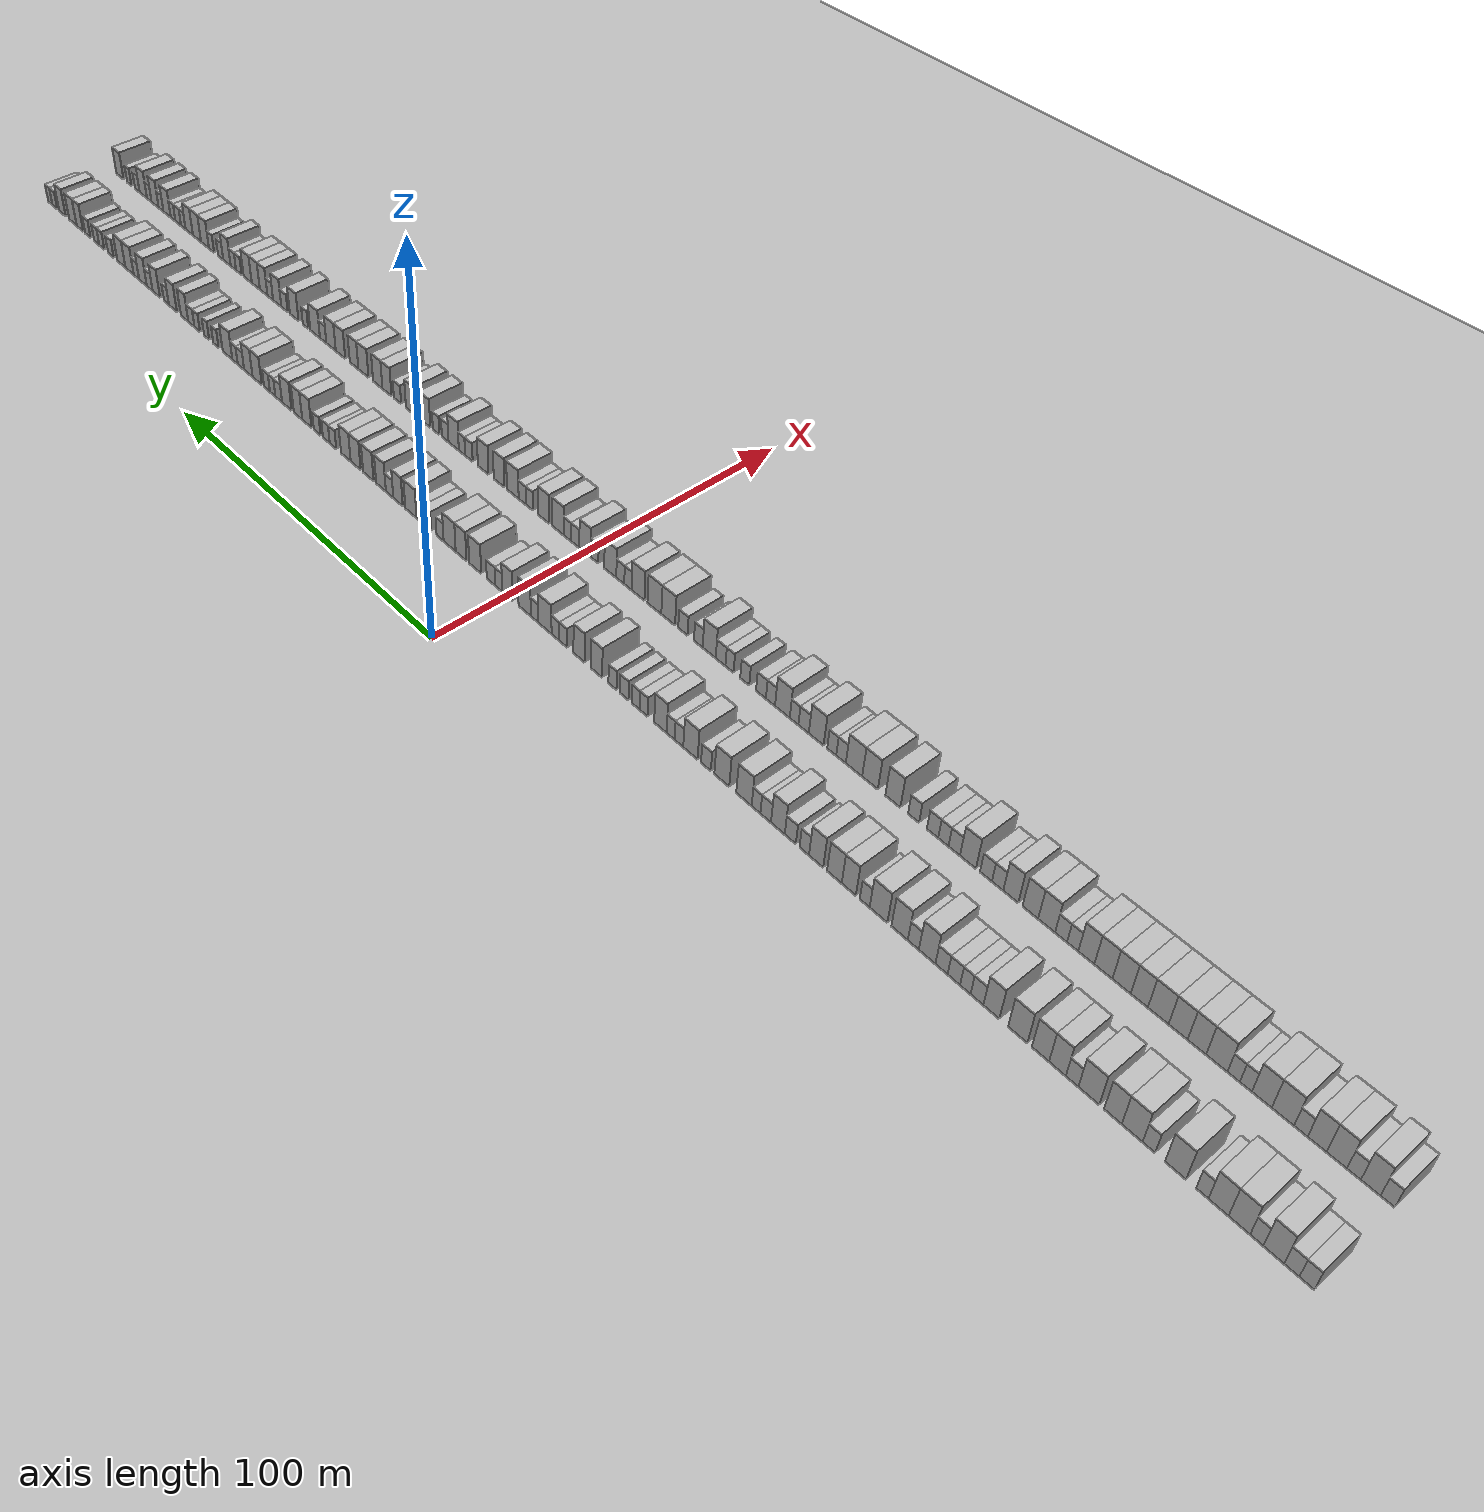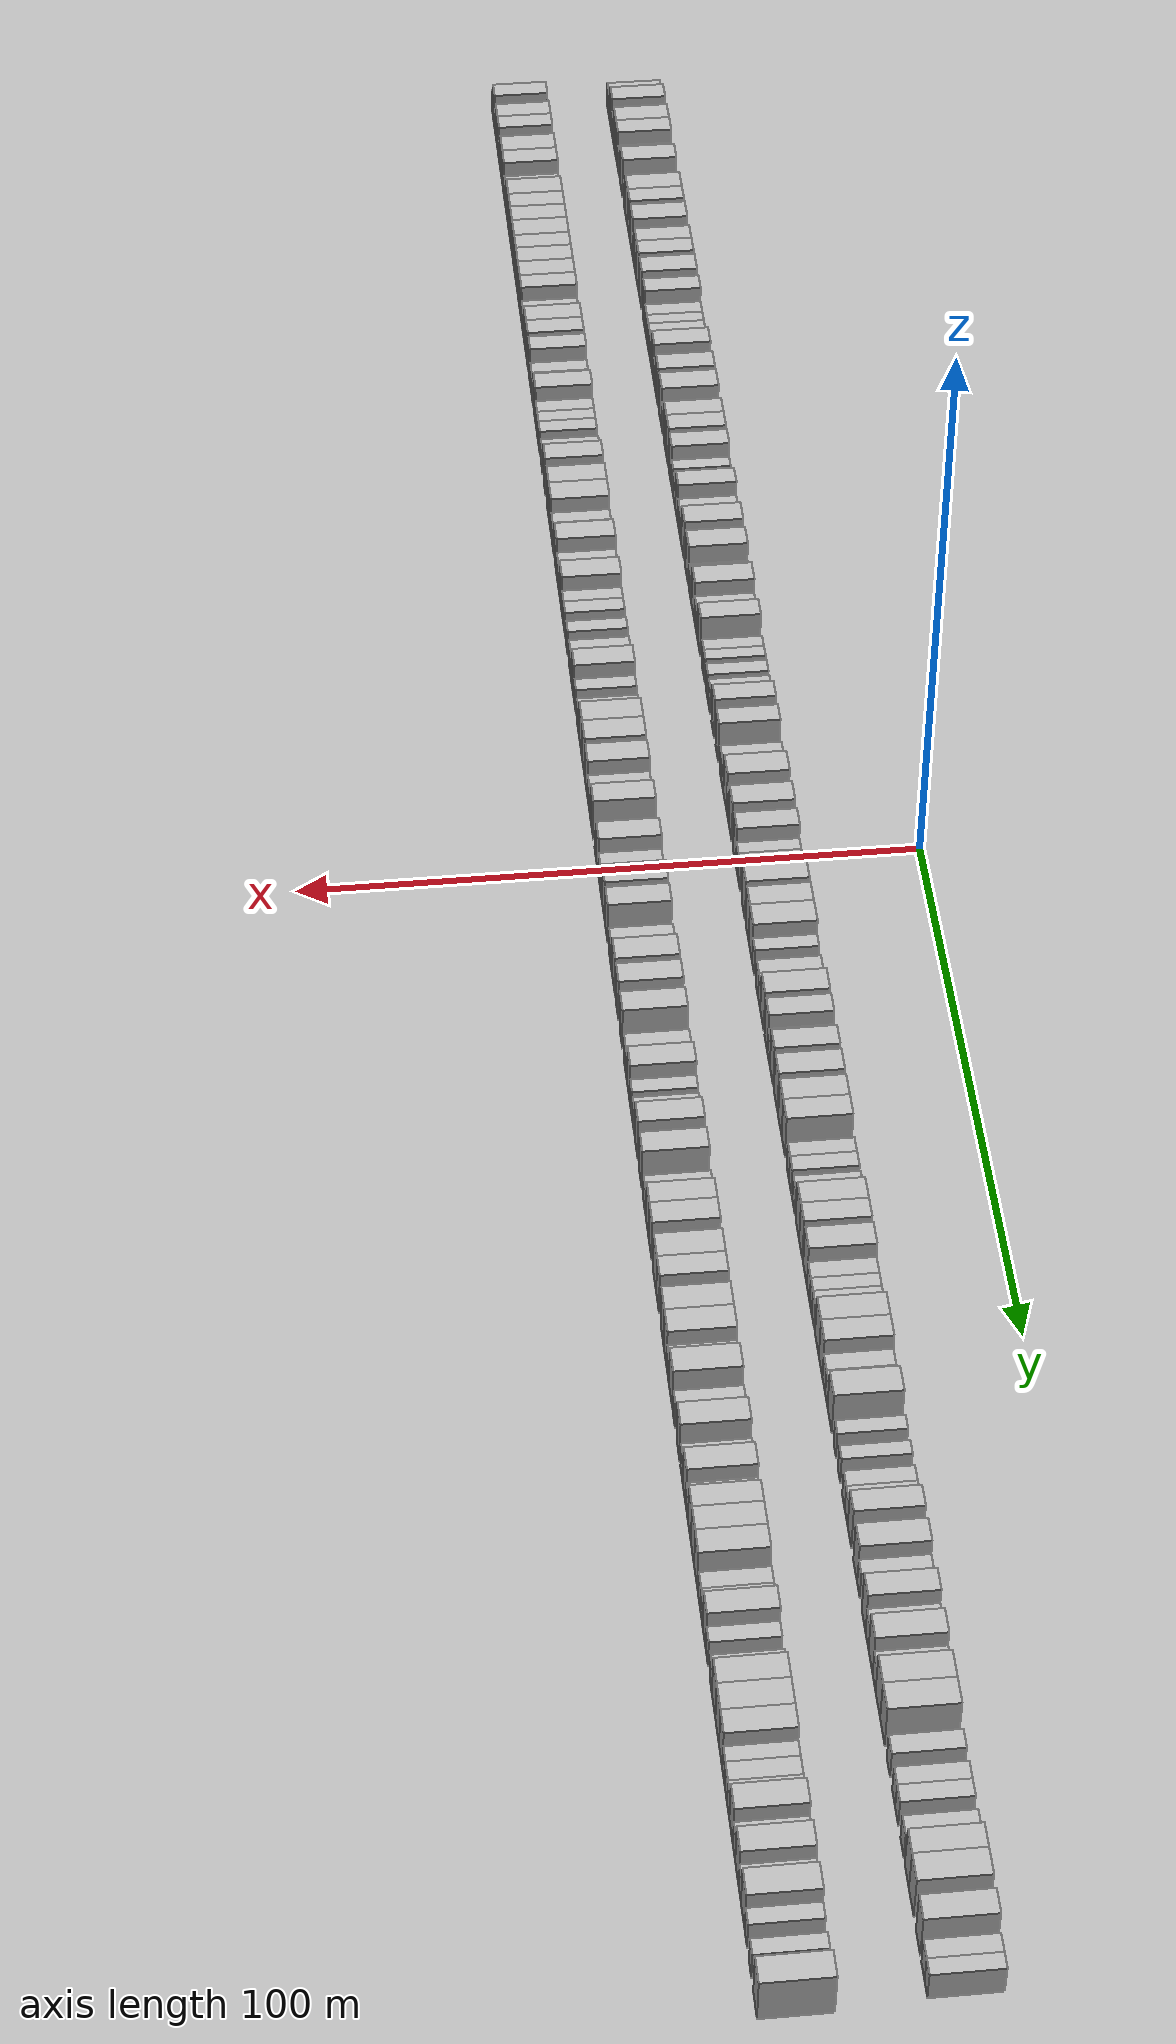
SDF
<?xml version="1.0" encoding="utf-8"?>

<sdf version="1.6">

   <world name="default">

      <gui fullscreen="0">

         <camera name="user_camera">

            <pose>-15 0 4.57585 0 0 0</pose>

            <view_controller>orbit</view_controller>

         </camera>

      </gui>

      <scene>

         <sky>

           <clouds>

             <speed>12</speed>

           </clouds>

         </sky>

         <ambient>0.4 0.4 0.4 1</ambient>

         <background>0.7 0.7 0.7 1</background>

         <shadows>1</shadows>

      </scene>

      <gravity>0 0 -9.8066</gravity>

      <magnetic_field>6e-06 2.3e-05 -4.2e-05</magnetic_field>

      <physics default="0" name="default_physics" type="ode">

         <ode>

            <solver>

               <type>quick</type>

               <iters>10</iters>

               <sor>1.0</sor>

               <use_dynamic_moi_rescaling>0</use_dynamic_moi_rescaling>

            </solver>

            <constraints>

               <cfm>0</cfm>

               <erp>0.2</erp>

               <contact_max_correcting_vel>100</contact_max_correcting_vel>

               <contact_surface_layer>0.001</contact_surface_layer>

            </constraints>

         </ode>

         <max_step_size>0.004</max_step_size>

         <real_time_factor>1</real_time_factor>

         <real_time_update_rate>250</real_time_update_rate>

      </physics>

      <light name="sun" type="directional">

         <cast_shadows>1</cast_shadows>

         <pose>0 0 10 0 0 0</pose>

         <diffuse>0.8 0.8 0.8 1</diffuse>

         <specular>0.2 0.2 0.2 1</specular>

         <attenuation>

            <range>1000</range>

            <constant>0.9</constant>

            <linear>0.01</linear>

            <quadratic>0.001</quadratic>

         </attenuation>

         <direction>-0.5 0.1 -0.9</direction>

      </light>

      <include>

         <name>ground_plane_1</name>

         <uri>model://HANNAS_ground_plane</uri>

         <pose>0 0 0  0 0 0</pose>

      </include>

      <include>

         <name>ground_plane_2</name>

         <uri>model://HANNAS_ground_plane</uri>

         <pose>100 0 0  0 0 0</pose>

      </include>

      <model name="building_1">

         <static>1</static>

         <pose frame="">25.0000 -202.6168 0 0.000000 0.000000 0.000000</pose>

         <link name="link">

            <pose frame="">0 0 3.00 0 0 0</pose>

            <collision name="collision">

               <geometry>

                  <box>

                     <size>10.0000 2.7663 6.0000</size>

                  </box>

               </geometry>

               <max_contacts>10</max_contacts>

               <surface>

                  <contact>

                     <ode/>

                  </contact>

                  <bounce/>

                  <friction>

                     <torsional>

                        <ode/>

                     </torsional>

                     <ode/>

                  </friction>

               </surface>

            </collision>

            <visual name="visual">

               <cast_shadows>0</cast_shadows>

               <geometry>

                  <box>

                     <size>10.0000 2.7663 6.0000</size>

                  </box>

               </geometry>

               <material>

                  <script>

                     <uri>model://HANNAS_wall/materials/scripts</uri>

                     <uri>model://HANNAS_wall/materials/textures</uri>

                     <name>vrc/HANNAS_wall</name>

                  </script>

               </material>

            </visual>

            <self_collide>0</self_collide>

            <enable_wind>0</enable_wind>

            <kinematic>0</kinematic>

         </link>

      </model>

      <model name="building_2">

         <static>1</static>

         <pose frame="">25.0000 -199.8396 0 0.000000 0.000000 0.000000</pose>

         <link name="link">

            <pose frame="">0 0 3.00 0 0 0</pose>

            <collision name="collision">

               <geometry>

                  <box>

                     <size>10.0000 2.7883 6.0000</size>

                  </box>

               </geometry>

               <max_contacts>10</max_contacts>

               <surface>

                  <contact>

                     <ode/>

                  </contact>

                  <bounce/>

                  <friction>

                     <torsional>

                        <ode/>

                     </torsional>

                     <ode/>

                  </friction>

               </surface>

            </collision>

            <visual name="visual">

               <cast_shadows>0</cast_shadows>

               <geometry>

                  <box>

                     <size>10.0000 2.7883 6.0000</size>

                  </box>

               </geometry>

               <material>

                  <script>

                     <uri>model://HANNAS_wall/materials/scripts</uri>

                     <uri>model://HANNAS_wall/materials/textures</uri>

                     <name>vrc/HANNAS_wall</name>

                  </script>

               </material>

            </visual>

            <self_collide>0</self_collide>

            <enable_wind>0</enable_wind>

            <kinematic>0</kinematic>

         </link>

      </model>

      <model name="building_3">

         <static>1</static>

         <pose frame="">25.0000 -196.4880 0 0.000000 0.000000 0.000000</pose>

         <link name="link">

            <pose frame="">0 0 4.50 0 0 0</pose>

            <collision name="collision">

               <geometry>

                  <box>

                     <size>10.0000 3.9148 9.0000</size>

                  </box>

               </geometry>

               <max_contacts>10</max_contacts>

               <surface>

                  <contact>

                     <ode/>

                  </contact>

                  <bounce/>

                  <friction>

                     <torsional>

                        <ode/>

                     </torsional>

                     <ode/>

                  </friction>

               </surface>

            </collision>

            <visual name="visual">

               <cast_shadows>0</cast_shadows>

               <geometry>

                  <box>

                     <size>10.0000 3.9148 9.0000</size>

                  </box>

               </geometry>

               <material>

                  <script>

                     <uri>model://HANNAS_wall/materials/scripts</uri>

                     <uri>model://HANNAS_wall/materials/textures</uri>

                     <name>vrc/HANNAS_wall</name>

                  </script>

               </material>

            </visual>

            <self_collide>0</self_collide>

            <enable_wind>0</enable_wind>

            <kinematic>0</kinematic>

         </link>

      </model>

      <model name="building_4">

         <static>1</static>

         <pose frame="">25.0000 -193.2830 0 0.000000 0.000000 0.000000</pose>

         <link name="link">

            <pose frame="">0 0 3.00 0 0 0</pose>

            <collision name="collision">

               <geometry>

                  <box>

                     <size>10.0000 2.4952 6.0000</size>

                  </box>

               </geometry>

               <max_contacts>10</max_contacts>

               <surface>

                  <contact>

                     <ode/>

                  </contact>

                  <bounce/>

                  <friction>

                     <torsional>

                        <ode/>

                     </torsional>

                     <ode/>

                  </friction>

               </surface>

            </collision>

            <visual name="visual">

               <cast_shadows>0</cast_shadows>

               <geometry>

                  <box>

                     <size>10.0000 2.4952 6.0000</size>

                  </box>

               </geometry>

               <material>

                  <script>

                     <uri>model://HANNAS_wall/materials/scripts</uri>

                     <uri>model://HANNAS_wall/materials/textures</uri>

                     <name>vrc/HANNAS_wall</name>

                  </script>

               </material>

            </visual>

            <self_collide>0</self_collide>

            <enable_wind>0</enable_wind>

            <kinematic>0</kinematic>

         </link>

      </model>

      <model name="building_5">

         <static>1</static>

         <pose frame="">25.0000 -189.9622 0 0.000000 0.000000 0.000000</pose>

         <link name="link">

            <pose frame="">0 0 4.50 0 0 0</pose>

            <collision name="collision">

               <geometry>

                  <box>

                     <size>10.0000 4.1462 9.0000</size>

                  </box>

               </geometry>

               <max_contacts>10</max_contacts>

               <surface>

                  <contact>

                     <ode/>

                  </contact>

                  <bounce/>

                  <friction>

                     <torsional>

                        <ode/>

                     </torsional>

                     <ode/>

                  </friction>

               </surface>

            </collision>

            <visual name="visual">

               <cast_shadows>0</cast_shadows>

               <geometry>

                  <box>

                     <size>10.0000 4.1462 9.0000</size>

                  </box>

               </geometry>

               <material>

                  <script>

                     <uri>model://HANNAS_wall/materials/scripts</uri>

                     <uri>model://HANNAS_wall/materials/textures</uri>

                     <name>vrc/HANNAS_wall</name>

                  </script>

               </material>

            </visual>

            <self_collide>0</self_collide>

            <enable_wind>0</enable_wind>

            <kinematic>0</kinematic>

         </link>

      </model>

      <model name="building_6">

         <static>1</static>

         <pose frame="">25.0000 -185.9337 0 0.000000 0.000000 0.000000</pose>

         <link name="link">

            <pose frame="">0 0 4.50 0 0 0</pose>

            <collision name="collision">

               <geometry>

                  <box>

                     <size>10.0000 3.9107 9.0000</size>

                  </box>

               </geometry>

               <max_contacts>10</max_contacts>

               <surface>

                  <contact>

                     <ode/>

                  </contact>

                  <bounce/>

                  <friction>

                     <torsional>

                        <ode/>

                     </torsional>

                     <ode/>

                  </friction>

               </surface>

            </collision>

            <visual name="visual">

               <cast_shadows>0</cast_shadows>

               <geometry>

                  <box>

                     <size>10.0000 3.9107 9.0000</size>

                  </box>

               </geometry>

               <material>

                  <script>

                     <uri>model://HANNAS_wall/materials/scripts</uri>

                     <uri>model://HANNAS_wall/materials/textures</uri>

                     <name>vrc/HANNAS_wall</name>

                  </script>

               </material>

            </visual>

            <self_collide>0</self_collide>

            <enable_wind>0</enable_wind>

            <kinematic>0</kinematic>

         </link>

      </model>

      <model name="building_7">

         <static>1</static>

         <pose frame="">25.0000 -182.7652 0 0.000000 0.000000 0.000000</pose>

         <link name="link">

            <pose frame="">0 0 3.00 0 0 0</pose>

            <collision name="collision">

               <geometry>

                  <box>

                     <size>10.0000 2.4263 6.0000</size>

                  </box>

               </geometry>

               <max_contacts>10</max_contacts>

               <surface>

                  <contact>

                     <ode/>

                  </contact>

                  <bounce/>

                  <friction>

                     <torsional>

                        <ode/>

                     </torsional>

                     <ode/>

                  </friction>

               </surface>

            </collision>

            <visual name="visual">

               <cast_shadows>0</cast_shadows>

               <geometry>

                  <box>

                     <size>10.0000 2.4263 6.0000</size>

                  </box>

               </geometry>

               <material>

                  <script>

                     <uri>model://HANNAS_wall/materials/scripts</uri>

                     <uri>model://HANNAS_wall/materials/textures</uri>

                     <name>vrc/HANNAS_wall</name>

                  </script>

               </material>

            </visual>

            <self_collide>0</self_collide>

            <enable_wind>0</enable_wind>

            <kinematic>0</kinematic>

         </link>

      </model>

      <model name="building_8">

         <static>1</static>

         <pose frame="">25.0000 -177.4382 0 0.000000 0.000000 0.000000</pose>

         <link name="link">

            <pose frame="">0 0 4.50 0 0 0</pose>

            <collision name="collision">

               <geometry>

                  <box>

                     <size>10.0000 4.2277 9.0000</size>

                  </box>

               </geometry>

               <max_contacts>10</max_contacts>

               <surface>

                  <contact>

                     <ode/>

                  </contact>

                  <bounce/>

                  <friction>

                     <torsional>

                        <ode/>

                     </torsional>

                     <ode/>

                  </friction>

               </surface>

            </collision>

            <visual name="visual">

               <cast_shadows>0</cast_shadows>

               <geometry>

                  <box>

                     <size>10.0000 4.2277 9.0000</size>

                  </box>

               </geometry>

               <material>

                  <script>

                     <uri>model://HANNAS_wall/materials/scripts</uri>

                     <uri>model://HANNAS_wall/materials/textures</uri>

                     <name>vrc/HANNAS_wall</name>

                  </script>

               </material>

            </visual>

            <self_collide>0</self_collide>

            <enable_wind>0</enable_wind>

            <kinematic>0</kinematic>

         </link>

      </model>

      <model name="building_9">

         <static>1</static>

         <pose frame="">25.0000 -172.0418 0 0.000000 0.000000 0.000000</pose>

         <link name="link">

            <pose frame="">0 0 3.00 0 0 0</pose>

            <collision name="collision">

               <geometry>

                  <box>

                     <size>10.0000 2.5651 6.0000</size>

                  </box>

               </geometry>

               <max_contacts>10</max_contacts>

               <surface>

                  <contact>

                     <ode/>

                  </contact>

                  <bounce/>

                  <friction>

                     <torsional>

                        <ode/>

                     </torsional>

                     <ode/>

                  </friction>

               </surface>

            </collision>

            <visual name="visual">

               <cast_shadows>0</cast_shadows>

               <geometry>

                  <box>

                     <size>10.0000 2.5651 6.0000</size>

                  </box>

               </geometry>

               <material>

                  <script>

                     <uri>model://HANNAS_wall/materials/scripts</uri>

                     <uri>model://HANNAS_wall/materials/textures</uri>

                     <name>vrc/HANNAS_wall</name>

                  </script>

               </material>

            </visual>

            <self_collide>0</self_collide>

            <enable_wind>0</enable_wind>

            <kinematic>0</kinematic>

         </link>

      </model>

      <model name="building_10">

         <static>1</static>

         <pose frame="">25.0000 -168.6014 0 0.000000 0.000000 0.000000</pose>

         <link name="link">

            <pose frame="">0 0 4.50 0 0 0</pose>

            <collision name="collision">

               <geometry>

                  <box>

                     <size>10.0000 4.3157 9.0000</size>

                  </box>

               </geometry>

               <max_contacts>10</max_contacts>

               <surface>

                  <contact>

                     <ode/>

                  </contact>

                  <bounce/>

                  <friction>

                     <torsional>

                        <ode/>

                     </torsional>

                     <ode/>

                  </friction>

               </surface>

            </collision>

            <visual name="visual">

               <cast_shadows>0</cast_shadows>

               <geometry>

                  <box>

                     <size>10.0000 4.3157 9.0000</size>

                  </box>

               </geometry>

               <material>

                  <script>

                     <uri>model://HANNAS_wall/materials/scripts</uri>

                     <uri>model://HANNAS_wall/materials/textures</uri>

                     <name>vrc/HANNAS_wall</name>

                  </script>

               </material>

            </visual>

            <self_collide>0</self_collide>

            <enable_wind>0</enable_wind>

            <kinematic>0</kinematic>

         </link>

      </model>

      <model name="building_11">

         <static>1</static>

         <pose frame="">25.0000 -164.5795 0 0.000000 0.000000 0.000000</pose>

         <link name="link">

            <pose frame="">0 0 4.50 0 0 0</pose>

            <collision name="collision">

               <geometry>

                  <box>

                     <size>10.0000 3.7280 9.0000</size>

                  </box>

               </geometry>

               <max_contacts>10</max_contacts>

               <surface>

                  <contact>

                     <ode/>

                  </contact>

                  <bounce/>

                  <friction>

                     <torsional>

                        <ode/>

                     </torsional>

                     <ode/>

                  </friction>

               </surface>

            </collision>

            <visual name="visual">

               <cast_shadows>0</cast_shadows>

               <geometry>

                  <box>

                     <size>10.0000 3.7280 9.0000</size>

                  </box>

               </geometry>

               <material>

                  <script>

                     <uri>model://HANNAS_wall/materials/scripts</uri>

                     <uri>model://HANNAS_wall/materials/textures</uri>

                     <name>vrc/HANNAS_wall</name>

                  </script>

               </material>

            </visual>

            <self_collide>0</self_collide>

            <enable_wind>0</enable_wind>

            <kinematic>0</kinematic>

         </link>

      </model>

      <model name="building_12">

         <static>1</static>

         <pose frame="">25.0000 -159.4663 0 0.000000 0.000000 0.000000</pose>

         <link name="link">

            <pose frame="">0 0 4.50 0 0 0</pose>

            <collision name="collision">

               <geometry>

                  <box>

                     <size>10.0000 4.4984 9.0000</size>

                  </box>

               </geometry>

               <max_contacts>10</max_contacts>

               <surface>

                  <contact>

                     <ode/>

                  </contact>

                  <bounce/>

                  <friction>

                     <torsional>

                        <ode/>

                     </torsional>

                     <ode/>

                  </friction>

               </surface>

            </collision>

            <visual name="visual">

               <cast_shadows>0</cast_shadows>

               <geometry>

                  <box>

                     <size>10.0000 4.4984 9.0000</size>

                  </box>

               </geometry>

               <material>

                  <script>

                     <uri>model://HANNAS_wall/materials/scripts</uri>

                     <uri>model://HANNAS_wall/materials/textures</uri>

                     <name>vrc/HANNAS_wall</name>

                  </script>

               </material>

            </visual>

            <self_collide>0</self_collide>

            <enable_wind>0</enable_wind>

            <kinematic>0</kinematic>

         </link>

      </model>

      <model name="building_13">

         <static>1</static>

         <pose frame="">25.0000 -155.8630 0 0.000000 0.000000 0.000000</pose>

         <link name="link">

            <pose frame="">0 0 3.00 0 0 0</pose>

            <collision name="collision">

               <geometry>

                  <box>

                     <size>10.0000 2.7081 6.0000</size>

                  </box>

               </geometry>

               <max_contacts>10</max_contacts>

               <surface>

                  <contact>

                     <ode/>

                  </contact>

                  <bounce/>

                  <friction>

                     <torsional>

                        <ode/>

                     </torsional>

                     <ode/>

                  </friction>

               </surface>

            </collision>

            <visual name="visual">

               <cast_shadows>0</cast_shadows>

               <geometry>

                  <box>

                     <size>10.0000 2.7081 6.0000</size>

                  </box>

               </geometry>

               <material>

                  <script>

                     <uri>model://HANNAS_wall/materials/scripts</uri>

                     <uri>model://HANNAS_wall/materials/textures</uri>

                     <name>vrc/HANNAS_wall</name>

                  </script>

               </material>

            </visual>

            <self_collide>0</self_collide>

            <enable_wind>0</enable_wind>

            <kinematic>0</kinematic>

         </link>

      </model>

      <model name="building_14">

         <static>1</static>

         <pose frame="">25.0000 -152.6666 0 0.000000 0.000000 0.000000</pose>

         <link name="link">

            <pose frame="">0 0 4.50 0 0 0</pose>

            <collision name="collision">

               <geometry>

                  <box>

                     <size>10.0000 3.6848 9.0000</size>

                  </box>

               </geometry>

               <max_contacts>10</max_contacts>

               <surface>

                  <contact>

                     <ode/>

                  </contact>

                  <bounce/>

                  <friction>

                     <torsional>

                        <ode/>

                     </torsional>

                     <ode/>

                  </friction>

               </surface>

            </collision>

            <visual name="visual">

               <cast_shadows>0</cast_shadows>

               <geometry>

                  <box>

                     <size>10.0000 3.6848 9.0000</size>

                  </box>

               </geometry>

               <material>

                  <script>

                     <uri>model://HANNAS_wall/materials/scripts</uri>

                     <uri>model://HANNAS_wall/materials/textures</uri>

                     <name>vrc/HANNAS_wall</name>

                  </script>

               </material>

            </visual>

            <self_collide>0</self_collide>

            <enable_wind>0</enable_wind>

            <kinematic>0</kinematic>

         </link>

      </model>

      <model name="building_15">

         <static>1</static>

         <pose frame="">25.0000 -148.9209 0 0.000000 0.000000 0.000000</pose>

         <link name="link">

            <pose frame="">0 0 4.50 0 0 0</pose>

            <collision name="collision">

               <geometry>

                  <box>

                     <size>10.0000 3.8066 9.0000</size>

                  </box>

               </geometry>

               <max_contacts>10</max_contacts>

               <surface>

                  <contact>

                     <ode/>

                  </contact>

                  <bounce/>

                  <friction>

                     <torsional>

                        <ode/>

                     </torsional>

                     <ode/>

                  </friction>

               </surface>

            </collision>

            <visual name="visual">

               <cast_shadows>0</cast_shadows>

               <geometry>

                  <box>

                     <size>10.0000 3.8066 9.0000</size>

                  </box>

               </geometry>

               <material>

                  <script>

                     <uri>model://HANNAS_wall/materials/scripts</uri>

                     <uri>model://HANNAS_wall/materials/textures</uri>

                     <name>vrc/HANNAS_wall</name>

                  </script>

               </material>

            </visual>

            <self_collide>0</self_collide>

            <enable_wind>0</enable_wind>

            <kinematic>0</kinematic>

         </link>

      </model>

      <model name="building_16">

         <static>1</static>

         <pose frame="">25.0000 -143.8390 0 0.000000 0.000000 0.000000</pose>

         <link name="link">

            <pose frame="">0 0 4.50 0 0 0</pose>

            <collision name="collision">

               <geometry>

                  <box>

                     <size>10.0000 4.3572 9.0000</size>

                  </box>

               </geometry>

               <max_contacts>10</max_contacts>

               <surface>

                  <contact>

                     <ode/>

                  </contact>

                  <bounce/>

                  <friction>

                     <torsional>

                        <ode/>

                     </torsional>

                     <ode/>

                  </friction>

               </surface>

            </collision>

            <visual name="visual">

               <cast_shadows>0</cast_shadows>

               <geometry>

                  <box>

                     <size>10.0000 4.3572 9.0000</size>

                  </box>

               </geometry>

               <material>

                  <script>

                     <uri>model://HANNAS_wall/materials/scripts</uri>

                     <uri>model://HANNAS_wall/materials/textures</uri>

                     <name>vrc/HANNAS_wall</name>

                  </script>

               </material>

            </visual>

            <self_collide>0</self_collide>

            <enable_wind>0</enable_wind>

            <kinematic>0</kinematic>

         </link>

      </model>

      <model name="building_17">

         <static>1</static>

         <pose frame="">25.0000 -137.8147 0 0.000000 0.000000 0.000000</pose>

         <link name="link">

            <pose frame="">0 0 4.50 0 0 0</pose>

            <collision name="collision">

               <geometry>

                  <box>

                     <size>10.0000 3.6914 9.0000</size>

                  </box>

               </geometry>

               <max_contacts>10</max_contacts>

               <surface>

                  <contact>

                     <ode/>

                  </contact>

                  <bounce/>

                  <friction>

                     <torsional>

                        <ode/>

                     </torsional>

                     <ode/>

                  </friction>

               </surface>

            </collision>

            <visual name="visual">

               <cast_shadows>0</cast_shadows>

               <geometry>

                  <box>

                     <size>10.0000 3.6914 9.0000</size>

                  </box>

               </geometry>

               <material>

                  <script>

                     <uri>model://HANNAS_wall/materials/scripts</uri>

                     <uri>model://HANNAS_wall/materials/textures</uri>

                     <name>vrc/HANNAS_wall</name>

                  </script>

               </material>

            </visual>

            <self_collide>0</self_collide>

            <enable_wind>0</enable_wind>

            <kinematic>0</kinematic>

         </link>

      </model>

      <model name="building_18">

         <static>1</static>

         <pose frame="">25.0000 -134.4775 0 0.000000 0.000000 0.000000</pose>

         <link name="link">

            <pose frame="">0 0 3.00 0 0 0</pose>

            <collision name="collision">

               <geometry>

                  <box>

                     <size>10.0000 2.9829 6.0000</size>

                  </box>

               </geometry>

               <max_contacts>10</max_contacts>

               <surface>

                  <contact>

                     <ode/>

                  </contact>

                  <bounce/>

                  <friction>

                     <torsional>

                        <ode/>

                     </torsional>

                     <ode/>

                  </friction>

               </surface>

            </collision>

            <visual name="visual">

               <cast_shadows>0</cast_shadows>

               <geometry>

                  <box>

                     <size>10.0000 2.9829 6.0000</size>

                  </box>

               </geometry>

               <material>

                  <script>

                     <uri>model://HANNAS_wall/materials/scripts</uri>

                     <uri>model://HANNAS_wall/materials/textures</uri>

                     <name>vrc/HANNAS_wall</name>

                  </script>

               </material>

            </visual>

            <self_collide>0</self_collide>

            <enable_wind>0</enable_wind>

            <kinematic>0</kinematic>

         </link>

      </model>

      <model name="building_19">

         <static>1</static>

         <pose frame="">25.0000 -131.7495 0 0.000000 0.000000 0.000000</pose>

         <link name="link">

            <pose frame="">0 0 3.00 0 0 0</pose>

            <collision name="collision">

               <geometry>

                  <box>

                     <size>10.0000 2.4731 6.0000</size>

                  </box>

               </geometry>

               <max_contacts>10</max_contacts>

               <surface>

                  <contact>

                     <ode/>

                  </contact>

                  <bounce/>

                  <friction>

                     <torsional>

                        <ode/>

                     </torsional>

                     <ode/>

                  </friction>

               </surface>

            </collision>

            <visual name="visual">

               <cast_shadows>0</cast_shadows>

               <geometry>

                  <box>

                     <size>10.0000 2.4731 6.0000</size>

                  </box>

               </geometry>

               <material>

                  <script>

                     <uri>model://HANNAS_wall/materials/scripts</uri>

                     <uri>model://HANNAS_wall/materials/textures</uri>

                     <name>vrc/HANNAS_wall</name>

                  </script>

               </material>

            </visual>

            <self_collide>0</self_collide>

            <enable_wind>0</enable_wind>

            <kinematic>0</kinematic>

         </link>

      </model>

      <model name="building_20">

         <static>1</static>

         <pose frame="">25.0000 -129.0263 0 0.000000 0.000000 0.000000</pose>

         <link name="link">

            <pose frame="">0 0 3.00 0 0 0</pose>

            <collision name="collision">

               <geometry>

                  <box>

                     <size>10.0000 2.9733 6.0000</size>

                  </box>

               </geometry>

               <max_contacts>10</max_contacts>

               <surface>

                  <contact>

                     <ode/>

                  </contact>

                  <bounce/>

                  <friction>

                     <torsional>

                        <ode/>

                     </torsional>

                     <ode/>

                  </friction>

               </surface>

            </collision>

            <visual name="visual">

               <cast_shadows>0</cast_shadows>

               <geometry>

                  <box>

                     <size>10.0000 2.9733 6.0000</size>

                  </box>

               </geometry>

               <material>

                  <script>

                     <uri>model://HANNAS_wall/materials/scripts</uri>

                     <uri>model://HANNAS_wall/materials/textures</uri>

                     <name>vrc/HANNAS_wall</name>

                  </script>

               </material>

            </visual>

            <self_collide>0</self_collide>

            <enable_wind>0</enable_wind>

            <kinematic>0</kinematic>

         </link>

      </model>

      <model name="building_21">

         <static>1</static>

         <pose frame="">25.0000 -126.0810 0 0.000000 0.000000 0.000000</pose>

         <link name="link">

            <pose frame="">0 0 3.00 0 0 0</pose>

            <collision name="collision">

               <geometry>

                  <box>

                     <size>10.0000 2.9173 6.0000</size>

                  </box>

               </geometry>

               <max_contacts>10</max_contacts>

               <surface>

                  <contact>

                     <ode/>

                  </contact>

                  <bounce/>

                  <friction>

                     <torsional>

                        <ode/>

                     </torsional>

                     <ode/>

                  </friction>

               </surface>

            </collision>

            <visual name="visual">

               <cast_shadows>0</cast_shadows>

               <geometry>

                  <box>

                     <size>10.0000 2.9173 6.0000</size>

                  </box>

               </geometry>

               <material>

                  <script>

                     <uri>model://HANNAS_wall/materials/scripts</uri>

                     <uri>model://HANNAS_wall/materials/textures</uri>

                     <name>vrc/HANNAS_wall</name>

                  </script>

               </material>

            </visual>

            <self_collide>0</self_collide>

            <enable_wind>0</enable_wind>

            <kinematic>0</kinematic>

         </link>

      </model>

      <model name="building_22">

         <static>1</static>

         <pose frame="">25.0000 -122.6243 0 0.000000 0.000000 0.000000</pose>

         <link name="link">

            <pose frame="">0 0 4.50 0 0 0</pose>

            <collision name="collision">

               <geometry>

                  <box>

                     <size>10.0000 3.9963 9.0000</size>

                  </box>

               </geometry>

               <max_contacts>10</max_contacts>

               <surface>

                  <contact>

                     <ode/>

                  </contact>

                  <bounce/>

                  <friction>

                     <torsional>

                        <ode/>

                     </torsional>

                     <ode/>

                  </friction>

               </surface>

            </collision>

            <visual name="visual">

               <cast_shadows>0</cast_shadows>

               <geometry>

                  <box>

                     <size>10.0000 3.9963 9.0000</size>

                  </box>

               </geometry>

               <material>

                  <script>

                     <uri>model://HANNAS_wall/materials/scripts</uri>

                     <uri>model://HANNAS_wall/materials/textures</uri>

                     <name>vrc/HANNAS_wall</name>

                  </script>

               </material>

            </visual>

            <self_collide>0</self_collide>

            <enable_wind>0</enable_wind>

            <kinematic>0</kinematic>

         </link>

      </model>

      <model name="building_23">

         <static>1</static>

         <pose frame="">25.0000 -119.2623 0 0.000000 0.000000 0.000000</pose>

         <link name="link">

            <pose frame="">0 0 3.00 0 0 0</pose>

            <collision name="collision">

               <geometry>

                  <box>

                     <size>10.0000 2.7276 6.0000</size>

                  </box>

               </geometry>

               <max_contacts>10</max_contacts>

               <surface>

                  <contact>

                     <ode/>

                  </contact>

                  <bounce/>

                  <friction>

                     <torsional>

                        <ode/>

                     </torsional>

                     <ode/>

                  </friction>

               </surface>

            </collision>

            <visual name="visual">

               <cast_shadows>0</cast_shadows>

               <geometry>

                  <box>

                     <size>10.0000 2.7276 6.0000</size>

                  </box>

               </geometry>

               <material>

                  <script>

                     <uri>model://HANNAS_wall/materials/scripts</uri>

                     <uri>model://HANNAS_wall/materials/textures</uri>

                     <name>vrc/HANNAS_wall</name>

                  </script>

               </material>

            </visual>

            <self_collide>0</self_collide>

            <enable_wind>0</enable_wind>

            <kinematic>0</kinematic>

         </link>

      </model>

      <model name="building_24">

         <static>1</static>

         <pose frame="">25.0000 -115.8694 0 0.000000 0.000000 0.000000</pose>

         <link name="link">

            <pose frame="">0 0 4.50 0 0 0</pose>

            <collision name="collision">

               <geometry>

                  <box>

                     <size>10.0000 4.0582 9.0000</size>

                  </box>

               </geometry>

               <max_contacts>10</max_contacts>

               <surface>

                  <contact>

                     <ode/>

                  </contact>

                  <bounce/>

                  <friction>

                     <torsional>

                        <ode/>

                     </torsional>

                     <ode/>

                  </friction>

               </surface>

            </collision>

            <visual name="visual">

               <cast_shadows>0</cast_shadows>

               <geometry>

                  <box>

                     <size>10.0000 4.0582 9.0000</size>

                  </box>

               </geometry>

               <material>

                  <script>

                     <uri>model://HANNAS_wall/materials/scripts</uri>

                     <uri>model://HANNAS_wall/materials/textures</uri>

                     <name>vrc/HANNAS_wall</name>

                  </script>

               </material>

            </visual>

            <self_collide>0</self_collide>

            <enable_wind>0</enable_wind>

            <kinematic>0</kinematic>

         </link>

      </model>

      <model name="building_25">

         <static>1</static>

         <pose frame="">25.0000 -110.6020 0 0.000000 0.000000 0.000000</pose>

         <link name="link">

            <pose frame="">0 0 4.50 0 0 0</pose>

            <collision name="collision">

               <geometry>

                  <box>

                     <size>10.0000 4.4767 9.0000</size>

                  </box>

               </geometry>

               <max_contacts>10</max_contacts>

               <surface>

                  <contact>

                     <ode/>

                  </contact>

                  <bounce/>

                  <friction>

                     <torsional>

                        <ode/>

                     </torsional>

                     <ode/>

                  </friction>

               </surface>

            </collision>

            <visual name="visual">

               <cast_shadows>0</cast_shadows>

               <geometry>

                  <box>

                     <size>10.0000 4.4767 9.0000</size>

                  </box>

               </geometry>

               <material>

                  <script>

                     <uri>model://HANNAS_wall/materials/scripts</uri>

                     <uri>model://HANNAS_wall/materials/textures</uri>

                     <name>vrc/HANNAS_wall</name>

                  </script>

               </material>

            </visual>

            <self_collide>0</self_collide>

            <enable_wind>0</enable_wind>

            <kinematic>0</kinematic>

         </link>

      </model>

      <model name="building_26">

         <static>1</static>

         <pose frame="">25.0000 -107.1024 0 0.000000 0.000000 0.000000</pose>

         <link name="link">

            <pose frame="">0 0 3.00 0 0 0</pose>

            <collision name="collision">

               <geometry>

                  <box>

                     <size>10.0000 2.5225 6.0000</size>

                  </box>

               </geometry>

               <max_contacts>10</max_contacts>

               <surface>

                  <contact>

                     <ode/>

                  </contact>

                  <bounce/>

                  <friction>

                     <torsional>

                        <ode/>

                     </torsional>

                     <ode/>

                  </friction>

               </surface>

            </collision>

            <visual name="visual">

               <cast_shadows>0</cast_shadows>

               <geometry>

                  <box>

                     <size>10.0000 2.5225 6.0000</size>

                  </box>

               </geometry>

               <material>

                  <script>

                     <uri>model://HANNAS_wall/materials/scripts</uri>

                     <uri>model://HANNAS_wall/materials/textures</uri>

                     <name>vrc/HANNAS_wall</name>

                  </script>

               </material>

            </visual>

            <self_collide>0</self_collide>

            <enable_wind>0</enable_wind>

            <kinematic>0</kinematic>

         </link>

      </model>

      <model name="building_27">

         <static>1</static>

         <pose frame="">25.0000 -103.0135 0 0.000000 0.000000 0.000000</pose>

         <link name="link">

            <pose frame="">0 0 4.50 0 0 0</pose>

            <collision name="collision">

               <geometry>

                  <box>

                     <size>10.0000 3.6551 9.0000</size>

                  </box>

               </geometry>

               <max_contacts>10</max_contacts>

               <surface>

                  <contact>

                     <ode/>

                  </contact>

                  <bounce/>

                  <friction>

                     <torsional>

                        <ode/>

                     </torsional>

                     <ode/>

                  </friction>

               </surface>

            </collision>

            <visual name="visual">

               <cast_shadows>0</cast_shadows>

               <geometry>

                  <box>

                     <size>10.0000 3.6551 9.0000</size>

                  </box>

               </geometry>

               <material>

                  <script>

                     <uri>model://HANNAS_wall/materials/scripts</uri>

                     <uri>model://HANNAS_wall/materials/textures</uri>

                     <name>vrc/HANNAS_wall</name>

                  </script>

               </material>

            </visual>

            <self_collide>0</self_collide>

            <enable_wind>0</enable_wind>

            <kinematic>0</kinematic>

         </link>

      </model>

      <model name="building_28">

         <static>1</static>

         <pose frame="">25.0000 -99.2691 0 0.000000 0.000000 0.000000</pose>

         <link name="link">

            <pose frame="">0 0 4.50 0 0 0</pose>

            <collision name="collision">

               <geometry>

                  <box>

                     <size>10.0000 3.8337 9.0000</size>

                  </box>

               </geometry>

               <max_contacts>10</max_contacts>

               <surface>

                  <contact>

                     <ode/>

                  </contact>

                  <bounce/>

                  <friction>

                     <torsional>

                        <ode/>

                     </torsional>

                     <ode/>

                  </friction>

               </surface>

            </collision>

            <visual name="visual">

               <cast_shadows>0</cast_shadows>

               <geometry>

                  <box>

                     <size>10.0000 3.8337 9.0000</size>

                  </box>

               </geometry>

               <material>

                  <script>

                     <uri>model://HANNAS_wall/materials/scripts</uri>

                     <uri>model://HANNAS_wall/materials/textures</uri>

                     <name>vrc/HANNAS_wall</name>

                  </script>

               </material>

            </visual>

            <self_collide>0</self_collide>

            <enable_wind>0</enable_wind>

            <kinematic>0</kinematic>

         </link>

      </model>

      <model name="building_29">

         <static>1</static>

         <pose frame="">25.0000 -94.4503 0 0.000000 0.000000 0.000000</pose>

         <link name="link">

            <pose frame="">0 0 4.50 0 0 0</pose>

            <collision name="collision">

               <geometry>

                  <box>

                     <size>10.0000 3.8038 9.0000</size>

                  </box>

               </geometry>

               <max_contacts>10</max_contacts>

               <surface>

                  <contact>

                     <ode/>

                  </contact>

                  <bounce/>

                  <friction>

                     <torsional>

                        <ode/>

                     </torsional>

                     <ode/>

                  </friction>

               </surface>

            </collision>

            <visual name="visual">

               <cast_shadows>0</cast_shadows>

               <geometry>

                  <box>

                     <size>10.0000 3.8038 9.0000</size>

                  </box>

               </geometry>

               <material>

                  <script>

                     <uri>model://HANNAS_wall/materials/scripts</uri>

                     <uri>model://HANNAS_wall/materials/textures</uri>

                     <name>vrc/HANNAS_wall</name>

                  </script>

               </material>

            </visual>

            <self_collide>0</self_collide>

            <enable_wind>0</enable_wind>

            <kinematic>0</kinematic>

         </link>

      </model>

      <model name="building_30">

         <static>1</static>

         <pose frame="">25.0000 -91.2841 0 0.000000 0.000000 0.000000</pose>

         <link name="link">

            <pose frame="">0 0 3.00 0 0 0</pose>

            <collision name="collision">

               <geometry>

                  <box>

                     <size>10.0000 2.5287 6.0000</size>

                  </box>

               </geometry>

               <max_contacts>10</max_contacts>

               <surface>

                  <contact>

                     <ode/>

                  </contact>

                  <bounce/>

                  <friction>

                     <torsional>

                        <ode/>

                     </torsional>

                     <ode/>

                  </friction>

               </surface>

            </collision>

            <visual name="visual">

               <cast_shadows>0</cast_shadows>

               <geometry>

                  <box>

                     <size>10.0000 2.5287 6.0000</size>

                  </box>

               </geometry>

               <material>

                  <script>

                     <uri>model://HANNAS_wall/materials/scripts</uri>

                     <uri>model://HANNAS_wall/materials/textures</uri>

                     <name>vrc/HANNAS_wall</name>

                  </script>

               </material>

            </visual>

            <self_collide>0</self_collide>

            <enable_wind>0</enable_wind>

            <kinematic>0</kinematic>

         </link>

      </model>

      <model name="building_31">

         <static>1</static>

         <pose frame="">25.0000 -87.5224 0 0.000000 0.000000 0.000000</pose>

         <link name="link">

            <pose frame="">0 0 3.00 0 0 0</pose>

            <collision name="collision">

               <geometry>

                  <box>

                     <size>10.0000 2.9947 6.0000</size>

                  </box>

               </geometry>

               <max_contacts>10</max_contacts>

               <surface>

                  <contact>

                     <ode/>

                  </contact>

                  <bounce/>

                  <friction>

                     <torsional>

                        <ode/>

                     </torsional>

                     <ode/>

                  </friction>

               </surface>

            </collision>

            <visual name="visual">

               <cast_shadows>0</cast_shadows>

               <geometry>

                  <box>

                     <size>10.0000 2.9947 6.0000</size>

                  </box>

               </geometry>

               <material>

                  <script>

                     <uri>model://HANNAS_wall/materials/scripts</uri>

                     <uri>model://HANNAS_wall/materials/textures</uri>

                     <name>vrc/HANNAS_wall</name>

                  </script>

               </material>

            </visual>

            <self_collide>0</self_collide>

            <enable_wind>0</enable_wind>

            <kinematic>0</kinematic>

         </link>

      </model>

      <model name="building_32">

         <static>1</static>

         <pose frame="">25.0000 -84.1280 0 0.000000 0.000000 0.000000</pose>

         <link name="link">

            <pose frame="">0 0 4.50 0 0 0</pose>

            <collision name="collision">

               <geometry>

                  <box>

                     <size>10.0000 3.7940 9.0000</size>

                  </box>

               </geometry>

               <max_contacts>10</max_contacts>

               <surface>

                  <contact>

                     <ode/>

                  </contact>

                  <bounce/>

                  <friction>

                     <torsional>

                        <ode/>

                     </torsional>

                     <ode/>

                  </friction>

               </surface>

            </collision>

            <visual name="visual">

               <cast_shadows>0</cast_shadows>

               <geometry>

                  <box>

                     <size>10.0000 3.7940 9.0000</size>

                  </box>

               </geometry>

               <material>

                  <script>

                     <uri>model://HANNAS_wall/materials/scripts</uri>

                     <uri>model://HANNAS_wall/materials/textures</uri>

                     <name>vrc/HANNAS_wall</name>

                  </script>

               </material>

            </visual>

            <self_collide>0</self_collide>

            <enable_wind>0</enable_wind>

            <kinematic>0</kinematic>

         </link>

      </model>

      <model name="building_33">

         <static>1</static>

         <pose frame="">25.0000 -80.7663 0 0.000000 0.000000 0.000000</pose>

         <link name="link">

            <pose frame="">0 0 3.00 0 0 0</pose>

            <collision name="collision">

               <geometry>

                  <box>

                     <size>10.0000 2.9295 6.0000</size>

                  </box>

               </geometry>

               <max_contacts>10</max_contacts>

               <surface>

                  <contact>

                     <ode/>

                  </contact>

                  <bounce/>

                  <friction>

                     <torsional>

                        <ode/>

                     </torsional>

                     <ode/>

                  </friction>

               </surface>

            </collision>

            <visual name="visual">

               <cast_shadows>0</cast_shadows>

               <geometry>

                  <box>

                     <size>10.0000 2.9295 6.0000</size>

                  </box>

               </geometry>

               <material>

                  <script>

                     <uri>model://HANNAS_wall/materials/scripts</uri>

                     <uri>model://HANNAS_wall/materials/textures</uri>

                     <name>vrc/HANNAS_wall</name>

                  </script>

               </material>

            </visual>

            <self_collide>0</self_collide>

            <enable_wind>0</enable_wind>

            <kinematic>0</kinematic>

         </link>

      </model>

      <model name="building_34">

         <static>1</static>

         <pose frame="">25.0000 -78.0802 0 0.000000 0.000000 0.000000</pose>

         <link name="link">

            <pose frame="">0 0 3.00 0 0 0</pose>

            <collision name="collision">

               <geometry>

                  <box>

                     <size>10.0000 2.4427 6.0000</size>

                  </box>

               </geometry>

               <max_contacts>10</max_contacts>

               <surface>

                  <contact>

                     <ode/>

                  </contact>

                  <bounce/>

                  <friction>

                     <torsional>

                        <ode/>

                     </torsional>

                     <ode/>

                  </friction>

               </surface>

            </collision>

            <visual name="visual">

               <cast_shadows>0</cast_shadows>

               <geometry>

                  <box>

                     <size>10.0000 2.4427 6.0000</size>

                  </box>

               </geometry>

               <material>

                  <script>

                     <uri>model://HANNAS_wall/materials/scripts</uri>

                     <uri>model://HANNAS_wall/materials/textures</uri>

                     <name>vrc/HANNAS_wall</name>

                  </script>

               </material>

            </visual>

            <self_collide>0</self_collide>

            <enable_wind>0</enable_wind>

            <kinematic>0</kinematic>

         </link>

      </model>

      <model name="building_35">

         <static>1</static>

         <pose frame="">25.0000 -74.6875 0 0.000000 0.000000 0.000000</pose>

         <link name="link">

            <pose frame="">0 0 4.50 0 0 0</pose>

            <collision name="collision">

               <geometry>

                  <box>

                     <size>10.0000 4.3428 9.0000</size>

                  </box>

               </geometry>

               <max_contacts>10</max_contacts>

               <surface>

                  <contact>

                     <ode/>

                  </contact>

                  <bounce/>

                  <friction>

                     <torsional>

                        <ode/>

                     </torsional>

                     <ode/>

                  </friction>

               </surface>

            </collision>

            <visual name="visual">

               <cast_shadows>0</cast_shadows>

               <geometry>

                  <box>

                     <size>10.0000 4.3428 9.0000</size>

                  </box>

               </geometry>

               <material>

                  <script>

                     <uri>model://HANNAS_wall/materials/scripts</uri>

                     <uri>model://HANNAS_wall/materials/textures</uri>

                     <name>vrc/HANNAS_wall</name>

                  </script>

               </material>

            </visual>

            <self_collide>0</self_collide>

            <enable_wind>0</enable_wind>

            <kinematic>0</kinematic>

         </link>

      </model>

      <model name="building_36">

         <static>1</static>

         <pose frame="">25.0000 -68.3680 0 0.000000 0.000000 0.000000</pose>

         <link name="link">

            <pose frame="">0 0 4.50 0 0 0</pose>

            <collision name="collision">

               <geometry>

                  <box>

                     <size>10.0000 4.2962 9.0000</size>

                  </box>

               </geometry>

               <max_contacts>10</max_contacts>

               <surface>

                  <contact>

                     <ode/>

                  </contact>

                  <bounce/>

                  <friction>

                     <torsional>

                        <ode/>

                     </torsional>

                     <ode/>

                  </friction>

               </surface>

            </collision>

            <visual name="visual">

               <cast_shadows>0</cast_shadows>

               <geometry>

                  <box>

                     <size>10.0000 4.2962 9.0000</size>

                  </box>

               </geometry>

               <material>

                  <script>

                     <uri>model://HANNAS_wall/materials/scripts</uri>

                     <uri>model://HANNAS_wall/materials/textures</uri>

                     <name>vrc/HANNAS_wall</name>

                  </script>

               </material>

            </visual>

            <self_collide>0</self_collide>

            <enable_wind>0</enable_wind>

            <kinematic>0</kinematic>

         </link>

      </model>

      <model name="building_37">

         <static>1</static>

         <pose frame="">25.0000 -63.7823 0 0.000000 0.000000 0.000000</pose>

         <link name="link">

            <pose frame="">0 0 3.00 0 0 0</pose>

            <collision name="collision">

               <geometry>

                  <box>

                     <size>10.0000 2.8752 6.0000</size>

                  </box>

               </geometry>

               <max_contacts>10</max_contacts>

               <surface>

                  <contact>

                     <ode/>

                  </contact>

                  <bounce/>

                  <friction>

                     <torsional>

                        <ode/>

                     </torsional>

                     <ode/>

                  </friction>

               </surface>

            </collision>

            <visual name="visual">

               <cast_shadows>0</cast_shadows>

               <geometry>

                  <box>

                     <size>10.0000 2.8752 6.0000</size>

                  </box>

               </geometry>

               <material>

                  <script>

                     <uri>model://HANNAS_wall/materials/scripts</uri>

                     <uri>model://HANNAS_wall/materials/textures</uri>

                     <name>vrc/HANNAS_wall</name>

                  </script>

               </material>

            </visual>

            <self_collide>0</self_collide>

            <enable_wind>0</enable_wind>

            <kinematic>0</kinematic>

         </link>

      </model>

      <model name="building_38">

         <static>1</static>

         <pose frame="">25.0000 -59.2195 0 0.000000 0.000000 0.000000</pose>

         <link name="link">

            <pose frame="">0 0 4.50 0 0 0</pose>

            <collision name="collision">

               <geometry>

                  <box>

                     <size>10.0000 4.2504 9.0000</size>

                  </box>

               </geometry>

               <max_contacts>10</max_contacts>

               <surface>

                  <contact>

                     <ode/>

                  </contact>

                  <bounce/>

                  <friction>

                     <torsional>

                        <ode/>

                     </torsional>

                     <ode/>

                  </friction>

               </surface>

            </collision>

            <visual name="visual">

               <cast_shadows>0</cast_shadows>

               <geometry>

                  <box>

                     <size>10.0000 4.2504 9.0000</size>

                  </box>

               </geometry>

               <material>

                  <script>

                     <uri>model://HANNAS_wall/materials/scripts</uri>

                     <uri>model://HANNAS_wall/materials/textures</uri>

                     <name>vrc/HANNAS_wall</name>

                  </script>

               </material>

            </visual>

            <self_collide>0</self_collide>

            <enable_wind>0</enable_wind>

            <kinematic>0</kinematic>

         </link>

      </model>

      <model name="building_39">

         <static>1</static>

         <pose frame="">25.0000 -55.8036 0 0.000000 0.000000 0.000000</pose>

         <link name="link">

            <pose frame="">0 0 3.00 0 0 0</pose>

            <collision name="collision">

               <geometry>

                  <box>

                     <size>10.0000 2.5814 6.0000</size>

                  </box>

               </geometry>

               <max_contacts>10</max_contacts>

               <surface>

                  <contact>

                     <ode/>

                  </contact>

                  <bounce/>

                  <friction>

                     <torsional>

                        <ode/>

                     </torsional>

                     <ode/>

                  </friction>

               </surface>

            </collision>

            <visual name="visual">

               <cast_shadows>0</cast_shadows>

               <geometry>

                  <box>

                     <size>10.0000 2.5814 6.0000</size>

                  </box>

               </geometry>

               <material>

                  <script>

                     <uri>model://HANNAS_wall/materials/scripts</uri>

                     <uri>model://HANNAS_wall/materials/textures</uri>

                     <name>vrc/HANNAS_wall</name>

                  </script>

               </material>

            </visual>

            <self_collide>0</self_collide>

            <enable_wind>0</enable_wind>

            <kinematic>0</kinematic>

         </link>

      </model>

      <model name="building_40">

         <static>1</static>

         <pose frame="">25.0000 -53.3108 0 0.000000 0.000000 0.000000</pose>

         <link name="link">

            <pose frame="">0 0 3.00 0 0 0</pose>

            <collision name="collision">

               <geometry>

                  <box>

                     <size>10.0000 2.4042 6.0000</size>

                  </box>

               </geometry>

               <max_contacts>10</max_contacts>

               <surface>

                  <contact>

                     <ode/>

                  </contact>

                  <bounce/>

                  <friction>

                     <torsional>

                        <ode/>

                     </torsional>

                     <ode/>

                  </friction>

               </surface>

            </collision>

            <visual name="visual">

               <cast_shadows>0</cast_shadows>

               <geometry>

                  <box>

                     <size>10.0000 2.4042 6.0000</size>

                  </box>

               </geometry>

               <material>

                  <script>

                     <uri>model://HANNAS_wall/materials/scripts</uri>

                     <uri>model://HANNAS_wall/materials/textures</uri>

                     <name>vrc/HANNAS_wall</name>

                  </script>

               </material>

            </visual>

            <self_collide>0</self_collide>

            <enable_wind>0</enable_wind>

            <kinematic>0</kinematic>

         </link>

      </model>

      <model name="building_41">

         <static>1</static>

         <pose frame="">25.0000 -50.2154 0 0.000000 0.000000 0.000000</pose>

         <link name="link">

            <pose frame="">0 0 4.50 0 0 0</pose>

            <collision name="collision">

               <geometry>

                  <box>

                     <size>10.0000 3.7865 9.0000</size>

                  </box>

               </geometry>

               <max_contacts>10</max_contacts>

               <surface>

                  <contact>

                     <ode/>

                  </contact>

                  <bounce/>

                  <friction>

                     <torsional>

                        <ode/>

                     </torsional>

                     <ode/>

                  </friction>

               </surface>

            </collision>

            <visual name="visual">

               <cast_shadows>0</cast_shadows>

               <geometry>

                  <box>

                     <size>10.0000 3.7865 9.0000</size>

                  </box>

               </geometry>

               <material>

                  <script>

                     <uri>model://HANNAS_wall/materials/scripts</uri>

                     <uri>model://HANNAS_wall/materials/textures</uri>

                     <name>vrc/HANNAS_wall</name>

                  </script>

               </material>

            </visual>

            <self_collide>0</self_collide>

            <enable_wind>0</enable_wind>

            <kinematic>0</kinematic>

         </link>

      </model>

      <model name="building_42">

         <static>1</static>

         <pose frame="">25.0000 -45.0724 0 0.000000 0.000000 0.000000</pose>

         <link name="link">

            <pose frame="">0 0 3.00 0 0 0</pose>

            <collision name="collision">

               <geometry>

                  <box>

                     <size>10.0000 2.4994 6.0000</size>

                  </box>

               </geometry>

               <max_contacts>10</max_contacts>

               <surface>

                  <contact>

                     <ode/>

                  </contact>

                  <bounce/>

                  <friction>

                     <torsional>

                        <ode/>

                     </torsional>

                     <ode/>

                  </friction>

               </surface>

            </collision>

            <visual name="visual">

               <cast_shadows>0</cast_shadows>

               <geometry>

                  <box>

                     <size>10.0000 2.4994 6.0000</size>

                  </box>

               </geometry>

               <material>

                  <script>

                     <uri>model://HANNAS_wall/materials/scripts</uri>

                     <uri>model://HANNAS_wall/materials/textures</uri>

                     <name>vrc/HANNAS_wall</name>

                  </script>

               </material>

            </visual>

            <self_collide>0</self_collide>

            <enable_wind>0</enable_wind>

            <kinematic>0</kinematic>

         </link>

      </model>

      <model name="building_43">

         <static>1</static>

         <pose frame="">25.0000 -42.6080 0 0.000000 0.000000 0.000000</pose>

         <link name="link">

            <pose frame="">0 0 3.00 0 0 0</pose>

            <collision name="collision">

               <geometry>

                  <box>

                     <size>10.0000 2.4295 6.0000</size>

                  </box>

               </geometry>

               <max_contacts>10</max_contacts>

               <surface>

                  <contact>

                     <ode/>

                  </contact>

                  <bounce/>

                  <friction>

                     <torsional>

                        <ode/>

                     </torsional>

                     <ode/>

                  </friction>

               </surface>

            </collision>

            <visual name="visual">

               <cast_shadows>0</cast_shadows>

               <geometry>

                  <box>

                     <size>10.0000 2.4295 6.0000</size>

                  </box>

               </geometry>

               <material>

                  <script>

                     <uri>model://HANNAS_wall/materials/scripts</uri>

                     <uri>model://HANNAS_wall/materials/textures</uri>

                     <name>vrc/HANNAS_wall</name>

                  </script>

               </material>

            </visual>

            <self_collide>0</self_collide>

            <enable_wind>0</enable_wind>

            <kinematic>0</kinematic>

         </link>

      </model>

      <model name="building_44">

         <static>1</static>

         <pose frame="">25.0000 -39.0224 0 0.000000 0.000000 0.000000</pose>

         <link name="link">

            <pose frame="">0 0 3.00 0 0 0</pose>

            <collision name="collision">

               <geometry>

                  <box>

                     <size>10.0000 2.7417 6.0000</size>

                  </box>

               </geometry>

               <max_contacts>10</max_contacts>

               <surface>

                  <contact>

                     <ode/>

                  </contact>

                  <bounce/>

                  <friction>

                     <torsional>

                        <ode/>

                     </torsional>

                     <ode/>

                  </friction>

               </surface>

            </collision>

            <visual name="visual">

               <cast_shadows>0</cast_shadows>

               <geometry>

                  <box>

                     <size>10.0000 2.7417 6.0000</size>

                  </box>

               </geometry>

               <material>

                  <script>

                     <uri>model://HANNAS_wall/materials/scripts</uri>

                     <uri>model://HANNAS_wall/materials/textures</uri>

                     <name>vrc/HANNAS_wall</name>

                  </script>

               </material>

            </visual>

            <self_collide>0</self_collide>

            <enable_wind>0</enable_wind>

            <kinematic>0</kinematic>

         </link>

      </model>

      <model name="building_45">

         <static>1</static>

         <pose frame="">25.0000 -35.3522 0 0.000000 0.000000 0.000000</pose>

         <link name="link">

            <pose frame="">0 0 3.00 0 0 0</pose>

            <collision name="collision">

               <geometry>

                  <box>

                     <size>10.0000 2.5987 6.0000</size>

                  </box>

               </geometry>

               <max_contacts>10</max_contacts>

               <surface>

                  <contact>

                     <ode/>

                  </contact>

                  <bounce/>

                  <friction>

                     <torsional>

                        <ode/>

                     </torsional>

                     <ode/>

                  </friction>

               </surface>

            </collision>

            <visual name="visual">

               <cast_shadows>0</cast_shadows>

               <geometry>

                  <box>

                     <size>10.0000 2.5987 6.0000</size>

                  </box>

               </geometry>

               <material>

                  <script>

                     <uri>model://HANNAS_wall/materials/scripts</uri>

                     <uri>model://HANNAS_wall/materials/textures</uri>

                     <name>vrc/HANNAS_wall</name>

                  </script>

               </material>

            </visual>

            <self_collide>0</self_collide>

            <enable_wind>0</enable_wind>

            <kinematic>0</kinematic>

         </link>

      </model>

      <model name="building_46">

         <static>1</static>

         <pose frame="">25.0000 -30.2233 0 0.000000 0.000000 0.000000</pose>

         <link name="link">

            <pose frame="">0 0 4.50 0 0 0</pose>

            <collision name="collision">

               <geometry>

                  <box>

                     <size>10.0000 3.6590 9.0000</size>

                  </box>

               </geometry>

               <max_contacts>10</max_contacts>

               <surface>

                  <contact>

                     <ode/>

                  </contact>

                  <bounce/>

                  <friction>

                     <torsional>

                        <ode/>

                     </torsional>

                     <ode/>

                  </friction>

               </surface>

            </collision>

            <visual name="visual">

               <cast_shadows>0</cast_shadows>

               <geometry>

                  <box>

                     <size>10.0000 3.6590 9.0000</size>

                  </box>

               </geometry>

               <material>

                  <script>

                     <uri>model://HANNAS_wall/materials/scripts</uri>

                     <uri>model://HANNAS_wall/materials/textures</uri>

                     <name>vrc/HANNAS_wall</name>

                  </script>

               </material>

            </visual>

            <self_collide>0</self_collide>

            <enable_wind>0</enable_wind>

            <kinematic>0</kinematic>

         </link>

      </model>

      <model name="building_47">

         <static>1</static>

         <pose frame="">25.0000 -24.5696 0 0.000000 0.000000 0.000000</pose>

         <link name="link">

            <pose frame="">0 0 4.50 0 0 0</pose>

            <collision name="collision">

               <geometry>

                  <box>

                     <size>10.0000 3.6484 9.0000</size>

                  </box>

               </geometry>

               <max_contacts>10</max_contacts>

               <surface>

                  <contact>

                     <ode/>

                  </contact>

                  <bounce/>

                  <friction>

                     <torsional>

                        <ode/>

                     </torsional>

                     <ode/>

                  </friction>

               </surface>

            </collision>

            <visual name="visual">

               <cast_shadows>0</cast_shadows>

               <geometry>

                  <box>

                     <size>10.0000 3.6484 9.0000</size>

                  </box>

               </geometry>

               <material>

                  <script>

                     <uri>model://HANNAS_wall/materials/scripts</uri>

                     <uri>model://HANNAS_wall/materials/textures</uri>

                     <name>vrc/HANNAS_wall</name>

                  </script>

               </material>

            </visual>

            <self_collide>0</self_collide>

            <enable_wind>0</enable_wind>

            <kinematic>0</kinematic>

         </link>

      </model>

      <model name="building_48">

         <static>1</static>

         <pose frame="">25.0000 -19.4353 0 0.000000 0.000000 0.000000</pose>

         <link name="link">

            <pose frame="">0 0 3.00 0 0 0</pose>

            <collision name="collision">

               <geometry>

                  <box>

                     <size>10.0000 2.6203 6.0000</size>

                  </box>

               </geometry>

               <max_contacts>10</max_contacts>

               <surface>

                  <contact>

                     <ode/>

                  </contact>

                  <bounce/>

                  <friction>

                     <torsional>

                        <ode/>

                     </torsional>

                     <ode/>

                  </friction>

               </surface>

            </collision>

            <visual name="visual">

               <cast_shadows>0</cast_shadows>

               <geometry>

                  <box>

                     <size>10.0000 2.6203 6.0000</size>

                  </box>

               </geometry>

               <material>

                  <script>

                     <uri>model://HANNAS_wall/materials/scripts</uri>

                     <uri>model://HANNAS_wall/materials/textures</uri>

                     <name>vrc/HANNAS_wall</name>

                  </script>

               </material>

            </visual>

            <self_collide>0</self_collide>

            <enable_wind>0</enable_wind>

            <kinematic>0</kinematic>

         </link>

      </model>

      <model name="building_49">

         <static>1</static>

         <pose frame="">25.0000 -16.7983 0 0.000000 0.000000 0.000000</pose>

         <link name="link">

            <pose frame="">0 0 3.00 0 0 0</pose>

            <collision name="collision">

               <geometry>

                  <box>

                     <size>10.0000 2.6536 6.0000</size>

                  </box>

               </geometry>

               <max_contacts>10</max_contacts>

               <surface>

                  <contact>

                     <ode/>

                  </contact>

                  <bounce/>

                  <friction>

                     <torsional>

                        <ode/>

                     </torsional>

                     <ode/>

                  </friction>

               </surface>

            </collision>

            <visual name="visual">

               <cast_shadows>0</cast_shadows>

               <geometry>

                  <box>

                     <size>10.0000 2.6536 6.0000</size>

                  </box>

               </geometry>

               <material>

                  <script>

                     <uri>model://HANNAS_wall/materials/scripts</uri>

                     <uri>model://HANNAS_wall/materials/textures</uri>

                     <name>vrc/HANNAS_wall</name>

                  </script>

               </material>

            </visual>

            <self_collide>0</self_collide>

            <enable_wind>0</enable_wind>

            <kinematic>0</kinematic>

         </link>

      </model>

      <model name="building_50">

         <static>1</static>

         <pose frame="">25.0000 -13.2360 0 0.000000 0.000000 0.000000</pose>

         <link name="link">

            <pose frame="">0 0 4.50 0 0 0</pose>

            <collision name="collision">

               <geometry>

                  <box>

                     <size>10.0000 4.4709 9.0000</size>

                  </box>

               </geometry>

               <max_contacts>10</max_contacts>

               <surface>

                  <contact>

                     <ode/>

                  </contact>

                  <bounce/>

                  <friction>

                     <torsional>

                        <ode/>

                     </torsional>

                     <ode/>

                  </friction>

               </surface>

            </collision>

            <visual name="visual">

               <cast_shadows>0</cast_shadows>

               <geometry>

                  <box>

                     <size>10.0000 4.4709 9.0000</size>

                  </box>

               </geometry>

               <material>

                  <script>

                     <uri>model://HANNAS_wall/materials/scripts</uri>

                     <uri>model://HANNAS_wall/materials/textures</uri>

                     <name>vrc/HANNAS_wall</name>

                  </script>

               </material>

            </visual>

            <self_collide>0</self_collide>

            <enable_wind>0</enable_wind>

            <kinematic>0</kinematic>

         </link>

      </model>

      <model name="building_51">

         <static>1</static>

         <pose frame="">25.0000 -9.7139 0 0.000000 0.000000 0.000000</pose>

         <link name="link">

            <pose frame="">0 0 3.00 0 0 0</pose>

            <collision name="collision">

               <geometry>

                  <box>

                     <size>10.0000 2.5732 6.0000</size>

                  </box>

               </geometry>

               <max_contacts>10</max_contacts>

               <surface>

                  <contact>

                     <ode/>

                  </contact>

                  <bounce/>

                  <friction>

                     <torsional>

                        <ode/>

                     </torsional>

                     <ode/>

                  </friction>

               </surface>

            </collision>

            <visual name="visual">

               <cast_shadows>0</cast_shadows>

               <geometry>

                  <box>

                     <size>10.0000 2.5732 6.0000</size>

                  </box>

               </geometry>

               <material>

                  <script>

                     <uri>model://HANNAS_wall/materials/scripts</uri>

                     <uri>model://HANNAS_wall/materials/textures</uri>

                     <name>vrc/HANNAS_wall</name>

                  </script>

               </material>

            </visual>

            <self_collide>0</self_collide>

            <enable_wind>0</enable_wind>

            <kinematic>0</kinematic>

         </link>

      </model>

      <model name="building_52">

         <static>1</static>

         <pose frame="">25.0000 -6.3271 0 0.000000 0.000000 0.000000</pose>

         <link name="link">

            <pose frame="">0 0 4.50 0 0 0</pose>

            <collision name="collision">

               <geometry>

                  <box>

                     <size>10.0000 4.2004 9.0000</size>

                  </box>

               </geometry>

               <max_contacts>10</max_contacts>

               <surface>

                  <contact>

                     <ode/>

                  </contact>

                  <bounce/>

                  <friction>

                     <torsional>

                        <ode/>

                     </torsional>

                     <ode/>

                  </friction>

               </surface>

            </collision>

            <visual name="visual">

               <cast_shadows>0</cast_shadows>

               <geometry>

                  <box>

                     <size>10.0000 4.2004 9.0000</size>

                  </box>

               </geometry>

               <material>

                  <script>

                     <uri>model://HANNAS_wall/materials/scripts</uri>

                     <uri>model://HANNAS_wall/materials/textures</uri>

                     <name>vrc/HANNAS_wall</name>

                  </script>

               </material>

            </visual>

            <self_collide>0</self_collide>

            <enable_wind>0</enable_wind>

            <kinematic>0</kinematic>

         </link>

      </model>

      <model name="building_53">

         <static>1</static>

         <pose frame="">25.0000 -0.3567 0 0.000000 0.000000 0.000000</pose>

         <link name="link">

            <pose frame="">0 0 4.50 0 0 0</pose>

            <collision name="collision">

               <geometry>

                  <box>

                     <size>10.0000 3.7404 9.0000</size>

                  </box>

               </geometry>

               <max_contacts>10</max_contacts>

               <surface>

                  <contact>

                     <ode/>

                  </contact>

                  <bounce/>

                  <friction>

                     <torsional>

                        <ode/>

                     </torsional>

                     <ode/>

                  </friction>

               </surface>

            </collision>

            <visual name="visual">

               <cast_shadows>0</cast_shadows>

               <geometry>

                  <box>

                     <size>10.0000 3.7404 9.0000</size>

                  </box>

               </geometry>

               <material>

                  <script>

                     <uri>model://HANNAS_wall/materials/scripts</uri>

                     <uri>model://HANNAS_wall/materials/textures</uri>

                     <name>vrc/HANNAS_wall</name>

                  </script>

               </material>

            </visual>

            <self_collide>0</self_collide>

            <enable_wind>0</enable_wind>

            <kinematic>0</kinematic>

         </link>

      </model>

      <model name="building_54">

         <static>1</static>

         <pose frame="">25.0000 2.7380 0 0.000000 0.000000 0.000000</pose>

         <link name="link">

            <pose frame="">0 0 3.00 0 0 0</pose>

            <collision name="collision">

               <geometry>

                  <box>

                     <size>10.0000 2.4489 6.0000</size>

                  </box>

               </geometry>

               <max_contacts>10</max_contacts>

               <surface>

                  <contact>

                     <ode/>

                  </contact>

                  <bounce/>

                  <friction>

                     <torsional>

                        <ode/>

                     </torsional>

                     <ode/>

                  </friction>

               </surface>

            </collision>

            <visual name="visual">

               <cast_shadows>0</cast_shadows>

               <geometry>

                  <box>

                     <size>10.0000 2.4489 6.0000</size>

                  </box>

               </geometry>

               <material>

                  <script>

                     <uri>model://HANNAS_wall/materials/scripts</uri>

                     <uri>model://HANNAS_wall/materials/textures</uri>

                     <name>vrc/HANNAS_wall</name>

                  </script>

               </material>

            </visual>

            <self_collide>0</self_collide>

            <enable_wind>0</enable_wind>

            <kinematic>0</kinematic>

         </link>

      </model>

      <model name="building_55">

         <static>1</static>

         <pose frame="">25.0000 5.4598 0 0.000000 0.000000 0.000000</pose>

         <link name="link">

            <pose frame="">0 0 3.00 0 0 0</pose>

            <collision name="collision">

               <geometry>

                  <box>

                     <size>10.0000 2.9948 6.0000</size>

                  </box>

               </geometry>

               <max_contacts>10</max_contacts>

               <surface>

                  <contact>

                     <ode/>

                  </contact>

                  <bounce/>

                  <friction>

                     <torsional>

                        <ode/>

                     </torsional>

                     <ode/>

                  </friction>

               </surface>

            </collision>

            <visual name="visual">

               <cast_shadows>0</cast_shadows>

               <geometry>

                  <box>

                     <size>10.0000 2.9948 6.0000</size>

                  </box>

               </geometry>

               <material>

                  <script>

                     <uri>model://HANNAS_wall/materials/scripts</uri>

                     <uri>model://HANNAS_wall/materials/textures</uri>

                     <name>vrc/HANNAS_wall</name>

                  </script>

               </material>

            </visual>

            <self_collide>0</self_collide>

            <enable_wind>0</enable_wind>

            <kinematic>0</kinematic>

         </link>

      </model>

      <model name="building_56">

         <static>1</static>

         <pose frame="">25.0000 11.1160 0 0.000000 0.000000 0.000000</pose>

         <link name="link">

            <pose frame="">0 0 4.50 0 0 0</pose>

            <collision name="collision">

               <geometry>

                  <box>

                     <size>10.0000 4.3177 9.0000</size>

                  </box>

               </geometry>

               <max_contacts>10</max_contacts>

               <surface>

                  <contact>

                     <ode/>

                  </contact>

                  <bounce/>

                  <friction>

                     <torsional>

                        <ode/>

                     </torsional>

                     <ode/>

                  </friction>

               </surface>

            </collision>

            <visual name="visual">

               <cast_shadows>0</cast_shadows>

               <geometry>

                  <box>

                     <size>10.0000 4.3177 9.0000</size>

                  </box>

               </geometry>

               <material>

                  <script>

                     <uri>model://HANNAS_wall/materials/scripts</uri>

                     <uri>model://HANNAS_wall/materials/textures</uri>

                     <name>vrc/HANNAS_wall</name>

                  </script>

               </material>

            </visual>

            <self_collide>0</self_collide>

            <enable_wind>0</enable_wind>

            <kinematic>0</kinematic>

         </link>

      </model>

      <model name="building_57">

         <static>1</static>

         <pose frame="">25.0000 16.2478 0 0.000000 0.000000 0.000000</pose>

         <link name="link">

            <pose frame="">0 0 4.50 0 0 0</pose>

            <collision name="collision">

               <geometry>

                  <box>

                     <size>10.0000 3.9459 9.0000</size>

                  </box>

               </geometry>

               <max_contacts>10</max_contacts>

               <surface>

                  <contact>

                     <ode/>

                  </contact>

                  <bounce/>

                  <friction>

                     <torsional>

                        <ode/>

                     </torsional>

                     <ode/>

                  </friction>

               </surface>

            </collision>

            <visual name="visual">

               <cast_shadows>0</cast_shadows>

               <geometry>

                  <box>

                     <size>10.0000 3.9459 9.0000</size>

                  </box>

               </geometry>

               <material>

                  <script>

                     <uri>model://HANNAS_wall/materials/scripts</uri>

                     <uri>model://HANNAS_wall/materials/textures</uri>

                     <name>vrc/HANNAS_wall</name>

                  </script>

               </material>

            </visual>

            <self_collide>0</self_collide>

            <enable_wind>0</enable_wind>

            <kinematic>0</kinematic>

         </link>

      </model>

      <model name="building_58">

         <static>1</static>

         <pose frame="">25.0000 20.4501 0 0.000000 0.000000 0.000000</pose>

         <link name="link">

            <pose frame="">0 0 4.50 0 0 0</pose>

            <collision name="collision">

               <geometry>

                  <box>

                     <size>10.0000 4.4586 9.0000</size>

                  </box>

               </geometry>

               <max_contacts>10</max_contacts>

               <surface>

                  <contact>

                     <ode/>

                  </contact>

                  <bounce/>

                  <friction>

                     <torsional>

                        <ode/>

                     </torsional>

                     <ode/>

                  </friction>

               </surface>

            </collision>

            <visual name="visual">

               <cast_shadows>0</cast_shadows>

               <geometry>

                  <box>

                     <size>10.0000 4.4586 9.0000</size>

                  </box>

               </geometry>

               <material>

                  <script>

                     <uri>model://HANNAS_wall/materials/scripts</uri>

                     <uri>model://HANNAS_wall/materials/textures</uri>

                     <name>vrc/HANNAS_wall</name>

                  </script>

               </material>

            </visual>

            <self_collide>0</self_collide>

            <enable_wind>0</enable_wind>

            <kinematic>0</kinematic>

         </link>

      </model>

      <model name="building_59">

         <static>1</static>

         <pose frame="">25.0000 23.9965 0 0.000000 0.000000 0.000000</pose>

         <link name="link">

            <pose frame="">0 0 3.00 0 0 0</pose>

            <collision name="collision">

               <geometry>

                  <box>

                     <size>10.0000 2.6342 6.0000</size>

                  </box>

               </geometry>

               <max_contacts>10</max_contacts>

               <surface>

                  <contact>

                     <ode/>

                  </contact>

                  <bounce/>

                  <friction>

                     <torsional>

                        <ode/>

                     </torsional>

                     <ode/>

                  </friction>

               </surface>

            </collision>

            <visual name="visual">

               <cast_shadows>0</cast_shadows>

               <geometry>

                  <box>

                     <size>10.0000 2.6342 6.0000</size>

                  </box>

               </geometry>

               <material>

                  <script>

                     <uri>model://HANNAS_wall/materials/scripts</uri>

                     <uri>model://HANNAS_wall/materials/textures</uri>

                     <name>vrc/HANNAS_wall</name>

                  </script>

               </material>

            </visual>

            <self_collide>0</self_collide>

            <enable_wind>0</enable_wind>

            <kinematic>0</kinematic>

         </link>

      </model>

      <model name="building_60">

         <static>1</static>

         <pose frame="">25.0000 28.7550 0 0.000000 0.000000 0.000000</pose>

         <link name="link">

            <pose frame="">0 0 3.00 0 0 0</pose>

            <collision name="collision">

               <geometry>

                  <box>

                     <size>10.0000 2.8829 6.0000</size>

                  </box>

               </geometry>

               <max_contacts>10</max_contacts>

               <surface>

                  <contact>

                     <ode/>

                  </contact>

                  <bounce/>

                  <friction>

                     <torsional>

                        <ode/>

                     </torsional>

                     <ode/>

                  </friction>

               </surface>

            </collision>

            <visual name="visual">

               <cast_shadows>0</cast_shadows>

               <geometry>

                  <box>

                     <size>10.0000 2.8829 6.0000</size>

                  </box>

               </geometry>

               <material>

                  <script>

                     <uri>model://HANNAS_wall/materials/scripts</uri>

                     <uri>model://HANNAS_wall/materials/textures</uri>

                     <name>vrc/HANNAS_wall</name>

                  </script>

               </material>

            </visual>

            <self_collide>0</self_collide>

            <enable_wind>0</enable_wind>

            <kinematic>0</kinematic>

         </link>

      </model>

      <model name="building_61">

         <static>1</static>

         <pose frame="">25.0000 31.5401 0 0.000000 0.000000 0.000000</pose>

         <link name="link">

            <pose frame="">0 0 3.00 0 0 0</pose>

            <collision name="collision">

               <geometry>

                  <box>

                     <size>10.0000 2.6871 6.0000</size>

                  </box>

               </geometry>

               <max_contacts>10</max_contacts>

               <surface>

                  <contact>

                     <ode/>

                  </contact>

                  <bounce/>

                  <friction>

                     <torsional>

                        <ode/>

                     </torsional>

                     <ode/>

                  </friction>

               </surface>

            </collision>

            <visual name="visual">

               <cast_shadows>0</cast_shadows>

               <geometry>

                  <box>

                     <size>10.0000 2.6871 6.0000</size>

                  </box>

               </geometry>

               <material>

                  <script>

                     <uri>model://HANNAS_wall/materials/scripts</uri>

                     <uri>model://HANNAS_wall/materials/textures</uri>

                     <name>vrc/HANNAS_wall</name>

                  </script>

               </material>

            </visual>

            <self_collide>0</self_collide>

            <enable_wind>0</enable_wind>

            <kinematic>0</kinematic>

         </link>

      </model>

      <model name="building_62">

         <static>1</static>

         <pose frame="">25.0000 35.0346 0 0.000000 0.000000 0.000000</pose>

         <link name="link">

            <pose frame="">0 0 4.50 0 0 0</pose>

            <collision name="collision">

               <geometry>

                  <box>

                     <size>10.0000 4.3019 9.0000</size>

                  </box>

               </geometry>

               <max_contacts>10</max_contacts>

               <surface>

                  <contact>

                     <ode/>

                  </contact>

                  <bounce/>

                  <friction>

                     <torsional>

                        <ode/>

                     </torsional>

                     <ode/>

                  </friction>

               </surface>

            </collision>

            <visual name="visual">

               <cast_shadows>0</cast_shadows>

               <geometry>

                  <box>

                     <size>10.0000 4.3019 9.0000</size>

                  </box>

               </geometry>

               <material>

                  <script>

                     <uri>model://HANNAS_wall/materials/scripts</uri>

                     <uri>model://HANNAS_wall/materials/textures</uri>

                     <name>vrc/HANNAS_wall</name>

                  </script>

               </material>

            </visual>

            <self_collide>0</self_collide>

            <enable_wind>0</enable_wind>

            <kinematic>0</kinematic>

         </link>

      </model>

      <model name="building_63">

         <static>1</static>

         <pose frame="">25.0000 40.0273 0 0.000000 0.000000 0.000000</pose>

         <link name="link">

            <pose frame="">0 0 4.50 0 0 0</pose>

            <collision name="collision">

               <geometry>

                  <box>

                     <size>10.0000 3.6837 9.0000</size>

                  </box>

               </geometry>

               <max_contacts>10</max_contacts>

               <surface>

                  <contact>

                     <ode/>

                  </contact>

                  <bounce/>

                  <friction>

                     <torsional>

                        <ode/>

                     </torsional>

                     <ode/>

                  </friction>

               </surface>

            </collision>

            <visual name="visual">

               <cast_shadows>0</cast_shadows>

               <geometry>

                  <box>

                     <size>10.0000 3.6837 9.0000</size>

                  </box>

               </geometry>

               <material>

                  <script>

                     <uri>model://HANNAS_wall/materials/scripts</uri>

                     <uri>model://HANNAS_wall/materials/textures</uri>

                     <name>vrc/HANNAS_wall</name>

                  </script>

               </material>

            </visual>

            <self_collide>0</self_collide>

            <enable_wind>0</enable_wind>

            <kinematic>0</kinematic>

         </link>

      </model>

      <model name="building_64">

         <static>1</static>

         <pose frame="">25.0000 43.3307 0 0.000000 0.000000 0.000000</pose>

         <link name="link">

            <pose frame="">0 0 3.00 0 0 0</pose>

            <collision name="collision">

               <geometry>

                  <box>

                     <size>10.0000 2.9231 6.0000</size>

                  </box>

               </geometry>

               <max_contacts>10</max_contacts>

               <surface>

                  <contact>

                     <ode/>

                  </contact>

                  <bounce/>

                  <friction>

                     <torsional>

                        <ode/>

                     </torsional>

                     <ode/>

                  </friction>

               </surface>

            </collision>

            <visual name="visual">

               <cast_shadows>0</cast_shadows>

               <geometry>

                  <box>

                     <size>10.0000 2.9231 6.0000</size>

                  </box>

               </geometry>

               <material>

                  <script>

                     <uri>model://HANNAS_wall/materials/scripts</uri>

                     <uri>model://HANNAS_wall/materials/textures</uri>

                     <name>vrc/HANNAS_wall</name>

                  </script>

               </material>

            </visual>

            <self_collide>0</self_collide>

            <enable_wind>0</enable_wind>

            <kinematic>0</kinematic>

         </link>

      </model>

      <model name="building_65">

         <static>1</static>

         <pose frame="">25.0000 46.7132 0 0.000000 0.000000 0.000000</pose>

         <link name="link">

            <pose frame="">0 0 4.50 0 0 0</pose>

            <collision name="collision">

               <geometry>

                  <box>

                     <size>10.0000 3.8419 9.0000</size>

                  </box>

               </geometry>

               <max_contacts>10</max_contacts>

               <surface>

                  <contact>

                     <ode/>

                  </contact>

                  <bounce/>

                  <friction>

                     <torsional>

                        <ode/>

                     </torsional>

                     <ode/>

                  </friction>

               </surface>

            </collision>

            <visual name="visual">

               <cast_shadows>0</cast_shadows>

               <geometry>

                  <box>

                     <size>10.0000 3.8419 9.0000</size>

                  </box>

               </geometry>

               <material>

                  <script>

                     <uri>model://HANNAS_wall/materials/scripts</uri>

                     <uri>model://HANNAS_wall/materials/textures</uri>

                     <name>vrc/HANNAS_wall</name>

                  </script>

               </material>

            </visual>

            <self_collide>0</self_collide>

            <enable_wind>0</enable_wind>

            <kinematic>0</kinematic>

         </link>

      </model>

      <model name="building_66">

         <static>1</static>

         <pose frame="">25.0000 51.7370 0 0.000000 0.000000 0.000000</pose>

         <link name="link">

            <pose frame="">0 0 4.50 0 0 0</pose>

            <collision name="collision">

               <geometry>

                  <box>

                     <size>10.0000 4.2055 9.0000</size>

                  </box>

               </geometry>

               <max_contacts>10</max_contacts>

               <surface>

                  <contact>

                     <ode/>

                  </contact>

                  <bounce/>

                  <friction>

                     <torsional>

                        <ode/>

                     </torsional>

                     <ode/>

                  </friction>

               </surface>

            </collision>

            <visual name="visual">

               <cast_shadows>0</cast_shadows>

               <geometry>

                  <box>

                     <size>10.0000 4.2055 9.0000</size>

                  </box>

               </geometry>

               <material>

                  <script>

                     <uri>model://HANNAS_wall/materials/scripts</uri>

                     <uri>model://HANNAS_wall/materials/textures</uri>

                     <name>vrc/HANNAS_wall</name>

                  </script>

               </material>

            </visual>

            <self_collide>0</self_collide>

            <enable_wind>0</enable_wind>

            <kinematic>0</kinematic>

         </link>

      </model>

      <model name="building_67">

         <static>1</static>

         <pose frame="">25.0000 56.8810 0 0.000000 0.000000 0.000000</pose>

         <link name="link">

            <pose frame="">0 0 4.50 0 0 0</pose>

            <collision name="collision">

               <geometry>

                  <box>

                     <size>10.0000 4.0826 9.0000</size>

                  </box>

               </geometry>

               <max_contacts>10</max_contacts>

               <surface>

                  <contact>

                     <ode/>

                  </contact>

                  <bounce/>

                  <friction>

                     <torsional>

                        <ode/>

                     </torsional>

                     <ode/>

                  </friction>

               </surface>

            </collision>

            <visual name="visual">

               <cast_shadows>0</cast_shadows>

               <geometry>

                  <box>

                     <size>10.0000 4.0826 9.0000</size>

                  </box>

               </geometry>

               <material>

                  <script>

                     <uri>model://HANNAS_wall/materials/scripts</uri>

                     <uri>model://HANNAS_wall/materials/textures</uri>

                     <name>vrc/HANNAS_wall</name>

                  </script>

               </material>

            </visual>

            <self_collide>0</self_collide>

            <enable_wind>0</enable_wind>

            <kinematic>0</kinematic>

         </link>

      </model>

      <model name="building_68">

         <static>1</static>

         <pose frame="">25.0000 60.9062 0 0.000000 0.000000 0.000000</pose>

         <link name="link">

            <pose frame="">0 0 4.50 0 0 0</pose>

            <collision name="collision">

               <geometry>

                  <box>

                     <size>10.0000 3.9676 9.0000</size>

                  </box>

               </geometry>

               <max_contacts>10</max_contacts>

               <surface>

                  <contact>

                     <ode/>

                  </contact>

                  <bounce/>

                  <friction>

                     <torsional>

                        <ode/>

                     </torsional>

                     <ode/>

                  </friction>

               </surface>

            </collision>

            <visual name="visual">

               <cast_shadows>0</cast_shadows>

               <geometry>

                  <box>

                     <size>10.0000 3.9676 9.0000</size>

                  </box>

               </geometry>

               <material>

                  <script>

                     <uri>model://HANNAS_wall/materials/scripts</uri>

                     <uri>model://HANNAS_wall/materials/textures</uri>

                     <name>vrc/HANNAS_wall</name>

                  </script>

               </material>

            </visual>

            <self_collide>0</self_collide>

            <enable_wind>0</enable_wind>

            <kinematic>0</kinematic>

         </link>

      </model>

      <model name="building_69">

         <static>1</static>

         <pose frame="">25.0000 66.2493 0 0.000000 0.000000 0.000000</pose>

         <link name="link">

            <pose frame="">0 0 3.00 0 0 0</pose>

            <collision name="collision">

               <geometry>

                  <box>

                     <size>10.0000 2.7186 6.0000</size>

                  </box>

               </geometry>

               <max_contacts>10</max_contacts>

               <surface>

                  <contact>

                     <ode/>

                  </contact>

                  <bounce/>

                  <friction>

                     <torsional>

                        <ode/>

                     </torsional>

                     <ode/>

                  </friction>

               </surface>

            </collision>

            <visual name="visual">

               <cast_shadows>0</cast_shadows>

               <geometry>

                  <box>

                     <size>10.0000 2.7186 6.0000</size>

                  </box>

               </geometry>

               <material>

                  <script>

                     <uri>model://HANNAS_wall/materials/scripts</uri>

                     <uri>model://HANNAS_wall/materials/textures</uri>

                     <name>vrc/HANNAS_wall</name>

                  </script>

               </material>

            </visual>

            <self_collide>0</self_collide>

            <enable_wind>0</enable_wind>

            <kinematic>0</kinematic>

         </link>

      </model>

      <model name="building_70">

         <static>1</static>

         <pose frame="">25.0000 69.0316 0 0.000000 0.000000 0.000000</pose>

         <link name="link">

            <pose frame="">0 0 3.00 0 0 0</pose>

            <collision name="collision">

               <geometry>

                  <box>

                     <size>10.0000 2.8460 6.0000</size>

                  </box>

               </geometry>

               <max_contacts>10</max_contacts>

               <surface>

                  <contact>

                     <ode/>

                  </contact>

                  <bounce/>

                  <friction>

                     <torsional>

                        <ode/>

                     </torsional>

                     <ode/>

                  </friction>

               </surface>

            </collision>

            <visual name="visual">

               <cast_shadows>0</cast_shadows>

               <geometry>

                  <box>

                     <size>10.0000 2.8460 6.0000</size>

                  </box>

               </geometry>

               <material>

                  <script>

                     <uri>model://HANNAS_wall/materials/scripts</uri>

                     <uri>model://HANNAS_wall/materials/textures</uri>

                     <name>vrc/HANNAS_wall</name>

                  </script>

               </material>

            </visual>

            <self_collide>0</self_collide>

            <enable_wind>0</enable_wind>

            <kinematic>0</kinematic>

         </link>

      </model>

      <model name="building_71">

         <static>1</static>

         <pose frame="">25.0000 72.8729 0 0.000000 0.000000 0.000000</pose>

         <link name="link">

            <pose frame="">0 0 3.00 0 0 0</pose>

            <collision name="collision">

               <geometry>

                  <box>

                     <size>10.0000 2.8367 6.0000</size>

                  </box>

               </geometry>

               <max_contacts>10</max_contacts>

               <surface>

                  <contact>

                     <ode/>

                  </contact>

                  <bounce/>

                  <friction>

                     <torsional>

                        <ode/>

                     </torsional>

                     <ode/>

                  </friction>

               </surface>

            </collision>

            <visual name="visual">

               <cast_shadows>0</cast_shadows>

               <geometry>

                  <box>

                     <size>10.0000 2.8367 6.0000</size>

                  </box>

               </geometry>

               <material>

                  <script>

                     <uri>model://HANNAS_wall/materials/scripts</uri>

                     <uri>model://HANNAS_wall/materials/textures</uri>

                     <name>vrc/HANNAS_wall</name>

                  </script>

               </material>

            </visual>

            <self_collide>0</self_collide>

            <enable_wind>0</enable_wind>

            <kinematic>0</kinematic>

         </link>

      </model>

      <model name="building_72">

         <static>1</static>

         <pose frame="">25.0000 77.2694 0 0.000000 0.000000 0.000000</pose>

         <link name="link">

            <pose frame="">0 0 4.50 0 0 0</pose>

            <collision name="collision">

               <geometry>

                  <box>

                     <size>10.0000 3.9564 9.0000</size>

                  </box>

               </geometry>

               <max_contacts>10</max_contacts>

               <surface>

                  <contact>

                     <ode/>

                  </contact>

                  <bounce/>

                  <friction>

                     <torsional>

                        <ode/>

                     </torsional>

                     <ode/>

                  </friction>

               </surface>

            </collision>

            <visual name="visual">

               <cast_shadows>0</cast_shadows>

               <geometry>

                  <box>

                     <size>10.0000 3.9564 9.0000</size>

                  </box>

               </geometry>

               <material>

                  <script>

                     <uri>model://HANNAS_wall/materials/scripts</uri>

                     <uri>model://HANNAS_wall/materials/textures</uri>

                     <name>vrc/HANNAS_wall</name>

                  </script>

               </material>

            </visual>

            <self_collide>0</self_collide>

            <enable_wind>0</enable_wind>

            <kinematic>0</kinematic>

         </link>

      </model>

      <model name="building_73">

         <static>1</static>

         <pose frame="">25.0000 81.0634 0 0.000000 0.000000 0.000000</pose>

         <link name="link">

            <pose frame="">0 0 4.50 0 0 0</pose>

            <collision name="collision">

               <geometry>

                  <box>

                     <size>10.0000 3.6316 9.0000</size>

                  </box>

               </geometry>

               <max_contacts>10</max_contacts>

               <surface>

                  <contact>

                     <ode/>

                  </contact>

                  <bounce/>

                  <friction>

                     <torsional>

                        <ode/>

                     </torsional>

                     <ode/>

                  </friction>

               </surface>

            </collision>

            <visual name="visual">

               <cast_shadows>0</cast_shadows>

               <geometry>

                  <box>

                     <size>10.0000 3.6316 9.0000</size>

                  </box>

               </geometry>

               <material>

                  <script>

                     <uri>model://HANNAS_wall/materials/scripts</uri>

                     <uri>model://HANNAS_wall/materials/textures</uri>

                     <name>vrc/HANNAS_wall</name>

                  </script>

               </material>

            </visual>

            <self_collide>0</self_collide>

            <enable_wind>0</enable_wind>

            <kinematic>0</kinematic>

         </link>

      </model>

      <model name="building_74">

         <static>1</static>

         <pose frame="">25.0000 85.9550 0 0.000000 0.000000 0.000000</pose>

         <link name="link">

            <pose frame="">0 0 4.50 0 0 0</pose>

            <collision name="collision">

               <geometry>

                  <box>

                     <size>10.0000 4.1516 9.0000</size>

                  </box>

               </geometry>

               <max_contacts>10</max_contacts>

               <surface>

                  <contact>

                     <ode/>

                  </contact>

                  <bounce/>

                  <friction>

                     <torsional>

                        <ode/>

                     </torsional>

                     <ode/>

                  </friction>

               </surface>

            </collision>

            <visual name="visual">

               <cast_shadows>0</cast_shadows>

               <geometry>

                  <box>

                     <size>10.0000 4.1516 9.0000</size>

                  </box>

               </geometry>

               <material>

                  <script>

                     <uri>model://HANNAS_wall/materials/scripts</uri>

                     <uri>model://HANNAS_wall/materials/textures</uri>

                     <name>vrc/HANNAS_wall</name>

                  </script>

               </material>

            </visual>

            <self_collide>0</self_collide>

            <enable_wind>0</enable_wind>

            <kinematic>0</kinematic>

         </link>

      </model>

      <model name="building_75">

         <static>1</static>

         <pose frame="">25.0000 89.5149 0 0.000000 0.000000 0.000000</pose>

         <link name="link">

            <pose frame="">0 0 3.00 0 0 0</pose>

            <collision name="collision">

               <geometry>

                  <box>

                     <size>10.0000 2.9682 6.0000</size>

                  </box>

               </geometry>

               <max_contacts>10</max_contacts>

               <surface>

                  <contact>

                     <ode/>

                  </contact>

                  <bounce/>

                  <friction>

                     <torsional>

                        <ode/>

                     </torsional>

                     <ode/>

                  </friction>

               </surface>

            </collision>

            <visual name="visual">

               <cast_shadows>0</cast_shadows>

               <geometry>

                  <box>

                     <size>10.0000 2.9682 6.0000</size>

                  </box>

               </geometry>

               <material>

                  <script>

                     <uri>model://HANNAS_wall/materials/scripts</uri>

                     <uri>model://HANNAS_wall/materials/textures</uri>

                     <name>vrc/HANNAS_wall</name>

                  </script>

               </material>

            </visual>

            <self_collide>0</self_collide>

            <enable_wind>0</enable_wind>

            <kinematic>0</kinematic>

         </link>

      </model>

      <model name="building_76">

         <static>1</static>

         <pose frame="">25.0000 92.2148 0 0.000000 0.000000 0.000000</pose>

         <link name="link">

            <pose frame="">0 0 3.00 0 0 0</pose>

            <collision name="collision">

               <geometry>

                  <box>

                     <size>10.0000 2.4316 6.0000</size>

                  </box>

               </geometry>

               <max_contacts>10</max_contacts>

               <surface>

                  <contact>

                     <ode/>

                  </contact>

                  <bounce/>

                  <friction>

                     <torsional>

                        <ode/>

                     </torsional>

                     <ode/>

                  </friction>

               </surface>

            </collision>

            <visual name="visual">

               <cast_shadows>0</cast_shadows>

               <geometry>

                  <box>

                     <size>10.0000 2.4316 6.0000</size>

                  </box>

               </geometry>

               <material>

                  <script>

                     <uri>model://HANNAS_wall/materials/scripts</uri>

                     <uri>model://HANNAS_wall/materials/textures</uri>

                     <name>vrc/HANNAS_wall</name>

                  </script>

               </material>

            </visual>

            <self_collide>0</self_collide>

            <enable_wind>0</enable_wind>

            <kinematic>0</kinematic>

         </link>

      </model>

      <model name="building_77">

         <static>1</static>

         <pose frame="">25.0000 94.7397 0 0.000000 0.000000 0.000000</pose>

         <link name="link">

            <pose frame="">0 0 3.00 0 0 0</pose>

            <collision name="collision">

               <geometry>

                  <box>

                     <size>10.0000 2.6181 6.0000</size>

                  </box>

               </geometry>

               <max_contacts>10</max_contacts>

               <surface>

                  <contact>

                     <ode/>

                  </contact>

                  <bounce/>

                  <friction>

                     <torsional>

                        <ode/>

                     </torsional>

                     <ode/>

                  </friction>

               </surface>

            </collision>

            <visual name="visual">

               <cast_shadows>0</cast_shadows>

               <geometry>

                  <box>

                     <size>10.0000 2.6181 6.0000</size>

                  </box>

               </geometry>

               <material>

                  <script>

                     <uri>model://HANNAS_wall/materials/scripts</uri>

                     <uri>model://HANNAS_wall/materials/textures</uri>

                     <name>vrc/HANNAS_wall</name>

                  </script>

               </material>

            </visual>

            <self_collide>0</self_collide>

            <enable_wind>0</enable_wind>

            <kinematic>0</kinematic>

         </link>

      </model>

      <model name="building_78">

         <static>1</static>

         <pose frame="">25.0000 99.1302 0 0.000000 0.000000 0.000000</pose>

         <link name="link">

            <pose frame="">0 0 4.50 0 0 0</pose>

            <collision name="collision">

               <geometry>

                  <box>

                     <size>10.0000 4.1629 9.0000</size>

                  </box>

               </geometry>

               <max_contacts>10</max_contacts>

               <surface>

                  <contact>

                     <ode/>

                  </contact>

                  <bounce/>

                  <friction>

                     <torsional>

                        <ode/>

                     </torsional>

                     <ode/>

                  </friction>

               </surface>

            </collision>

            <visual name="visual">

               <cast_shadows>0</cast_shadows>

               <geometry>

                  <box>

                     <size>10.0000 4.1629 9.0000</size>

                  </box>

               </geometry>

               <material>

                  <script>

                     <uri>model://HANNAS_wall/materials/scripts</uri>

                     <uri>model://HANNAS_wall/materials/textures</uri>

                     <name>vrc/HANNAS_wall</name>

                  </script>

               </material>

            </visual>

            <self_collide>0</self_collide>

            <enable_wind>0</enable_wind>

            <kinematic>0</kinematic>

         </link>

      </model>

      <model name="building_79">

         <static>1</static>

         <pose frame="">25.0000 103.1425 0 0.000000 0.000000 0.000000</pose>

         <link name="link">

            <pose frame="">0 0 4.50 0 0 0</pose>

            <collision name="collision">

               <geometry>

                  <box>

                     <size>10.0000 3.8617 9.0000</size>

                  </box>

               </geometry>

               <max_contacts>10</max_contacts>

               <surface>

                  <contact>

                     <ode/>

                  </contact>

                  <bounce/>

                  <friction>

                     <torsional>

                        <ode/>

                     </torsional>

                     <ode/>

                  </friction>

               </surface>

            </collision>

            <visual name="visual">

               <cast_shadows>0</cast_shadows>

               <geometry>

                  <box>

                     <size>10.0000 3.8617 9.0000</size>

                  </box>

               </geometry>

               <material>

                  <script>

                     <uri>model://HANNAS_wall/materials/scripts</uri>

                     <uri>model://HANNAS_wall/materials/textures</uri>

                     <name>vrc/HANNAS_wall</name>

                  </script>

               </material>

            </visual>

            <self_collide>0</self_collide>

            <enable_wind>0</enable_wind>

            <kinematic>0</kinematic>

         </link>

      </model>

      <model name="building_80">

         <static>1</static>

         <pose frame="">25.0000 106.5391 0 0.000000 0.000000 0.000000</pose>

         <link name="link">

            <pose frame="">0 0 3.00 0 0 0</pose>

            <collision name="collision">

               <geometry>

                  <box>

                     <size>10.0000 2.9316 6.0000</size>

                  </box>

               </geometry>

               <max_contacts>10</max_contacts>

               <surface>

                  <contact>

                     <ode/>

                  </contact>

                  <bounce/>

                  <friction>

                     <torsional>

                        <ode/>

                     </torsional>

                     <ode/>

                  </friction>

               </surface>

            </collision>

            <visual name="visual">

               <cast_shadows>0</cast_shadows>

               <geometry>

                  <box>

                     <size>10.0000 2.9316 6.0000</size>

                  </box>

               </geometry>

               <material>

                  <script>

                     <uri>model://HANNAS_wall/materials/scripts</uri>

                     <uri>model://HANNAS_wall/materials/textures</uri>

                     <name>vrc/HANNAS_wall</name>

                  </script>

               </material>

            </visual>

            <self_collide>0</self_collide>

            <enable_wind>0</enable_wind>

            <kinematic>0</kinematic>

         </link>

      </model>

      <model name="building_81">

         <static>1</static>

         <pose frame="">25.0000 109.2578 0 0.000000 0.000000 0.000000</pose>

         <link name="link">

            <pose frame="">0 0 3.00 0 0 0</pose>

            <collision name="collision">

               <geometry>

                  <box>

                     <size>10.0000 2.5059 6.0000</size>

                  </box>

               </geometry>

               <max_contacts>10</max_contacts>

               <surface>

                  <contact>

                     <ode/>

                  </contact>

                  <bounce/>

                  <friction>

                     <torsional>

                        <ode/>

                     </torsional>

                     <ode/>

                  </friction>

               </surface>

            </collision>

            <visual name="visual">

               <cast_shadows>0</cast_shadows>

               <geometry>

                  <box>

                     <size>10.0000 2.5059 6.0000</size>

                  </box>

               </geometry>

               <material>

                  <script>

                     <uri>model://HANNAS_wall/materials/scripts</uri>

                     <uri>model://HANNAS_wall/materials/textures</uri>

                     <name>vrc/HANNAS_wall</name>

                  </script>

               </material>

            </visual>

            <self_collide>0</self_collide>

            <enable_wind>0</enable_wind>

            <kinematic>0</kinematic>

         </link>

      </model>

      <model name="building_82">

         <static>1</static>

         <pose frame="">25.0000 112.7416 0 0.000000 0.000000 0.000000</pose>

         <link name="link">

            <pose frame="">0 0 4.50 0 0 0</pose>

            <collision name="collision">

               <geometry>

                  <box>

                     <size>10.0000 4.4617 9.0000</size>

                  </box>

               </geometry>

               <max_contacts>10</max_contacts>

               <surface>

                  <contact>

                     <ode/>

                  </contact>

                  <bounce/>

                  <friction>

                     <torsional>

                        <ode/>

                     </torsional>

                     <ode/>

                  </friction>

               </surface>

            </collision>

            <visual name="visual">

               <cast_shadows>0</cast_shadows>

               <geometry>

                  <box>

                     <size>10.0000 4.4617 9.0000</size>

                  </box>

               </geometry>

               <material>

                  <script>

                     <uri>model://HANNAS_wall/materials/scripts</uri>

                     <uri>model://HANNAS_wall/materials/textures</uri>

                     <name>vrc/HANNAS_wall</name>

                  </script>

               </material>

            </visual>

            <self_collide>0</self_collide>

            <enable_wind>0</enable_wind>

            <kinematic>0</kinematic>

         </link>

      </model>

      <model name="building_83">

         <static>1</static>

         <pose frame="">25.0000 118.1971 0 0.000000 0.000000 0.000000</pose>

         <link name="link">

            <pose frame="">0 0 3.00 0 0 0</pose>

            <collision name="collision">

               <geometry>

                  <box>

                     <size>10.0000 2.4492 6.0000</size>

                  </box>

               </geometry>

               <max_contacts>10</max_contacts>

               <surface>

                  <contact>

                     <ode/>

                  </contact>

                  <bounce/>

                  <friction>

                     <torsional>

                        <ode/>

                     </torsional>

                     <ode/>

                  </friction>

               </surface>

            </collision>

            <visual name="visual">

               <cast_shadows>0</cast_shadows>

               <geometry>

                  <box>

                     <size>10.0000 2.4492 6.0000</size>

                  </box>

               </geometry>

               <material>

                  <script>

                     <uri>model://HANNAS_wall/materials/scripts</uri>

                     <uri>model://HANNAS_wall/materials/textures</uri>

                     <name>vrc/HANNAS_wall</name>

                  </script>

               </material>

            </visual>

            <self_collide>0</self_collide>

            <enable_wind>0</enable_wind>

            <kinematic>0</kinematic>

         </link>

      </model>

      <model name="building_84">

         <static>1</static>

         <pose frame="">25.0000 122.6277 0 0.000000 0.000000 0.000000</pose>

         <link name="link">

            <pose frame="">0 0 3.00 0 0 0</pose>

            <collision name="collision">

               <geometry>

                  <box>

                     <size>10.0000 2.4119 6.0000</size>

                  </box>

               </geometry>

               <max_contacts>10</max_contacts>

               <surface>

                  <contact>

                     <ode/>

                  </contact>

                  <bounce/>

                  <friction>

                     <torsional>

                        <ode/>

                     </torsional>

                     <ode/>

                  </friction>

               </surface>

            </collision>

            <visual name="visual">

               <cast_shadows>0</cast_shadows>

               <geometry>

                  <box>

                     <size>10.0000 2.4119 6.0000</size>

                  </box>

               </geometry>

               <material>

                  <script>

                     <uri>model://HANNAS_wall/materials/scripts</uri>

                     <uri>model://HANNAS_wall/materials/textures</uri>

                     <name>vrc/HANNAS_wall</name>

                  </script>

               </material>

            </visual>

            <self_collide>0</self_collide>

            <enable_wind>0</enable_wind>

            <kinematic>0</kinematic>

         </link>

      </model>

      <model name="building_85">

         <static>1</static>

         <pose frame="">25.0000 127.1482 0 0.000000 0.000000 0.000000</pose>

         <link name="link">

            <pose frame="">0 0 3.00 0 0 0</pose>

            <collision name="collision">

               <geometry>

                  <box>

                     <size>10.0000 2.6293 6.0000</size>

                  </box>

               </geometry>

               <max_contacts>10</max_contacts>

               <surface>

                  <contact>

                     <ode/>

                  </contact>

                  <bounce/>

                  <friction>

                     <torsional>

                        <ode/>

                     </torsional>

                     <ode/>

                  </friction>

               </surface>

            </collision>

            <visual name="visual">

               <cast_shadows>0</cast_shadows>

               <geometry>

                  <box>

                     <size>10.0000 2.6293 6.0000</size>

                  </box>

               </geometry>

               <material>

                  <script>

                     <uri>model://HANNAS_wall/materials/scripts</uri>

                     <uri>model://HANNAS_wall/materials/textures</uri>

                     <name>vrc/HANNAS_wall</name>

                  </script>

               </material>

            </visual>

            <self_collide>0</self_collide>

            <enable_wind>0</enable_wind>

            <kinematic>0</kinematic>

         </link>

      </model>

      <model name="building_86">

         <static>1</static>

         <pose frame="">25.0000 129.9582 0 0.000000 0.000000 0.000000</pose>

         <link name="link">

            <pose frame="">0 0 3.00 0 0 0</pose>

            <collision name="collision">

               <geometry>

                  <box>

                     <size>10.0000 2.9906 6.0000</size>

                  </box>

               </geometry>

               <max_contacts>10</max_contacts>

               <surface>

                  <contact>

                     <ode/>

                  </contact>

                  <bounce/>

                  <friction>

                     <torsional>

                        <ode/>

                     </torsional>

                     <ode/>

                  </friction>

               </surface>

            </collision>

            <visual name="visual">

               <cast_shadows>0</cast_shadows>

               <geometry>

                  <box>

                     <size>10.0000 2.9906 6.0000</size>

                  </box>

               </geometry>

               <material>

                  <script>

                     <uri>model://HANNAS_wall/materials/scripts</uri>

                     <uri>model://HANNAS_wall/materials/textures</uri>

                     <name>vrc/HANNAS_wall</name>

                  </script>

               </material>

            </visual>

            <self_collide>0</self_collide>

            <enable_wind>0</enable_wind>

            <kinematic>0</kinematic>

         </link>

      </model>

      <model name="building_87">

         <static>1</static>

         <pose frame="">25.0000 133.2649 0 0.000000 0.000000 0.000000</pose>

         <link name="link">

            <pose frame="">0 0 4.50 0 0 0</pose>

            <collision name="collision">

               <geometry>

                  <box>

                     <size>10.0000 3.6228 9.0000</size>

                  </box>

               </geometry>

               <max_contacts>10</max_contacts>

               <surface>

                  <contact>

                     <ode/>

                  </contact>

                  <bounce/>

                  <friction>

                     <torsional>

                        <ode/>

                     </torsional>

                     <ode/>

                  </friction>

               </surface>

            </collision>

            <visual name="visual">

               <cast_shadows>0</cast_shadows>

               <geometry>

                  <box>

                     <size>10.0000 3.6228 9.0000</size>

                  </box>

               </geometry>

               <material>

                  <script>

                     <uri>model://HANNAS_wall/materials/scripts</uri>

                     <uri>model://HANNAS_wall/materials/textures</uri>

                     <name>vrc/HANNAS_wall</name>

                  </script>

               </material>

            </visual>

            <self_collide>0</self_collide>

            <enable_wind>0</enable_wind>

            <kinematic>0</kinematic>

         </link>

      </model>

      <model name="building_88">

         <static>1</static>

         <pose frame="">25.0000 139.0532 0 0.000000 0.000000 0.000000</pose>

         <link name="link">

            <pose frame="">0 0 4.50 0 0 0</pose>

            <collision name="collision">

               <geometry>

                  <box>

                     <size>10.0000 3.9539 9.0000</size>

                  </box>

               </geometry>

               <max_contacts>10</max_contacts>

               <surface>

                  <contact>

                     <ode/>

                  </contact>

                  <bounce/>

                  <friction>

                     <torsional>

                        <ode/>

                     </torsional>

                     <ode/>

                  </friction>

               </surface>

            </collision>

            <visual name="visual">

               <cast_shadows>0</cast_shadows>

               <geometry>

                  <box>

                     <size>10.0000 3.9539 9.0000</size>

                  </box>

               </geometry>

               <material>

                  <script>

                     <uri>model://HANNAS_wall/materials/scripts</uri>

                     <uri>model://HANNAS_wall/materials/textures</uri>

                     <name>vrc/HANNAS_wall</name>

                  </script>

               </material>

            </visual>

            <self_collide>0</self_collide>

            <enable_wind>0</enable_wind>

            <kinematic>0</kinematic>

         </link>

      </model>

      <model name="building_89">

         <static>1</static>

         <pose frame="">25.0000 142.2580 0 0.000000 0.000000 0.000000</pose>

         <link name="link">

            <pose frame="">0 0 3.00 0 0 0</pose>

            <collision name="collision">

               <geometry>

                  <box>

                     <size>10.0000 2.4556 6.0000</size>

                  </box>

               </geometry>

               <max_contacts>10</max_contacts>

               <surface>

                  <contact>

                     <ode/>

                  </contact>

                  <bounce/>

                  <friction>

                     <torsional>

                        <ode/>

                     </torsional>

                     <ode/>

                  </friction>

               </surface>

            </collision>

            <visual name="visual">

               <cast_shadows>0</cast_shadows>

               <geometry>

                  <box>

                     <size>10.0000 2.4556 6.0000</size>

                  </box>

               </geometry>

               <material>

                  <script>

                     <uri>model://HANNAS_wall/materials/scripts</uri>

                     <uri>model://HANNAS_wall/materials/textures</uri>

                     <name>vrc/HANNAS_wall</name>

                  </script>

               </material>

            </visual>

            <self_collide>0</self_collide>

            <enable_wind>0</enable_wind>

            <kinematic>0</kinematic>

         </link>

      </model>

      <model name="building_90">

         <static>1</static>

         <pose frame="">25.0000 147.3455 0 0.000000 0.000000 0.000000</pose>

         <link name="link">

            <pose frame="">0 0 4.50 0 0 0</pose>

            <collision name="collision">

               <geometry>

                  <box>

                     <size>10.0000 3.7194 9.0000</size>

                  </box>

               </geometry>

               <max_contacts>10</max_contacts>

               <surface>

                  <contact>

                     <ode/>

                  </contact>

                  <bounce/>

                  <friction>

                     <torsional>

                        <ode/>

                     </torsional>

                     <ode/>

                  </friction>

               </surface>

            </collision>

            <visual name="visual">

               <cast_shadows>0</cast_shadows>

               <geometry>

                  <box>

                     <size>10.0000 3.7194 9.0000</size>

                  </box>

               </geometry>

               <material>

                  <script>

                     <uri>model://HANNAS_wall/materials/scripts</uri>

                     <uri>model://HANNAS_wall/materials/textures</uri>

                     <name>vrc/HANNAS_wall</name>

                  </script>

               </material>

            </visual>

            <self_collide>0</self_collide>

            <enable_wind>0</enable_wind>

            <kinematic>0</kinematic>

         </link>

      </model>

      <model name="building_91">

         <static>1</static>

         <pose frame="">25.0000 150.6848 0 0.000000 0.000000 0.000000</pose>

         <link name="link">

            <pose frame="">0 0 3.00 0 0 0</pose>

            <collision name="collision">

               <geometry>

                  <box>

                     <size>10.0000 2.9591 6.0000</size>

                  </box>

               </geometry>

               <max_contacts>10</max_contacts>

               <surface>

                  <contact>

                     <ode/>

                  </contact>

                  <bounce/>

                  <friction>

                     <torsional>

                        <ode/>

                     </torsional>

                     <ode/>

                  </friction>

               </surface>

            </collision>

            <visual name="visual">

               <cast_shadows>0</cast_shadows>

               <geometry>

                  <box>

                     <size>10.0000 2.9591 6.0000</size>

                  </box>

               </geometry>

               <material>

                  <script>

                     <uri>model://HANNAS_wall/materials/scripts</uri>

                     <uri>model://HANNAS_wall/materials/textures</uri>

                     <name>vrc/HANNAS_wall</name>

                  </script>

               </material>

            </visual>

            <self_collide>0</self_collide>

            <enable_wind>0</enable_wind>

            <kinematic>0</kinematic>

         </link>

      </model>

      <model name="building_92">

         <static>1</static>

         <pose frame="">25.0000 154.1503 0 0.000000 0.000000 0.000000</pose>

         <link name="link">

            <pose frame="">0 0 4.50 0 0 0</pose>

            <collision name="collision">

               <geometry>

                  <box>

                     <size>10.0000 3.9718 9.0000</size>

                  </box>

               </geometry>

               <max_contacts>10</max_contacts>

               <surface>

                  <contact>

                     <ode/>

                  </contact>

                  <bounce/>

                  <friction>

                     <torsional>

                        <ode/>

                     </torsional>

                     <ode/>

                  </friction>

               </surface>

            </collision>

            <visual name="visual">

               <cast_shadows>0</cast_shadows>

               <geometry>

                  <box>

                     <size>10.0000 3.9718 9.0000</size>

                  </box>

               </geometry>

               <material>

                  <script>

                     <uri>model://HANNAS_wall/materials/scripts</uri>

                     <uri>model://HANNAS_wall/materials/textures</uri>

                     <name>vrc/HANNAS_wall</name>

                  </script>

               </material>

            </visual>

            <self_collide>0</self_collide>

            <enable_wind>0</enable_wind>

            <kinematic>0</kinematic>

         </link>

      </model>

      <model name="building_93">

         <static>1</static>

         <pose frame="">25.0000 157.5284 0 0.000000 0.000000 0.000000</pose>

         <link name="link">

            <pose frame="">0 0 3.00 0 0 0</pose>

            <collision name="collision">

               <geometry>

                  <box>

                     <size>10.0000 2.7844 6.0000</size>

                  </box>

               </geometry>

               <max_contacts>10</max_contacts>

               <surface>

                  <contact>

                     <ode/>

                  </contact>

                  <bounce/>

                  <friction>

                     <torsional>

                        <ode/>

                     </torsional>

                     <ode/>

                  </friction>

               </surface>

            </collision>

            <visual name="visual">

               <cast_shadows>0</cast_shadows>

               <geometry>

                  <box>

                     <size>10.0000 2.7844 6.0000</size>

                  </box>

               </geometry>

               <material>

                  <script>

                     <uri>model://HANNAS_wall/materials/scripts</uri>

                     <uri>model://HANNAS_wall/materials/textures</uri>

                     <name>vrc/HANNAS_wall</name>

                  </script>

               </material>

            </visual>

            <self_collide>0</self_collide>

            <enable_wind>0</enable_wind>

            <kinematic>0</kinematic>

         </link>

      </model>

      <model name="building_94">

         <static>1</static>

         <pose frame="">25.0000 161.0848 0 0.000000 0.000000 0.000000</pose>

         <link name="link">

            <pose frame="">0 0 4.50 0 0 0</pose>

            <collision name="collision">

               <geometry>

                  <box>

                     <size>10.0000 4.3284 9.0000</size>

                  </box>

               </geometry>

               <max_contacts>10</max_contacts>

               <surface>

                  <contact>

                     <ode/>

                  </contact>

                  <bounce/>

                  <friction>

                     <torsional>

                        <ode/>

                     </torsional>

                     <ode/>

                  </friction>

               </surface>

            </collision>

            <visual name="visual">

               <cast_shadows>0</cast_shadows>

               <geometry>

                  <box>

                     <size>10.0000 4.3284 9.0000</size>

                  </box>

               </geometry>

               <material>

                  <script>

                     <uri>model://HANNAS_wall/materials/scripts</uri>

                     <uri>model://HANNAS_wall/materials/textures</uri>

                     <name>vrc/HANNAS_wall</name>

                  </script>

               </material>

            </visual>

            <self_collide>0</self_collide>

            <enable_wind>0</enable_wind>

            <kinematic>0</kinematic>

         </link>

      </model>

      <model name="building_95">

         <static>1</static>

         <pose frame="">25.0000 165.3684 0 0.000000 0.000000 0.000000</pose>

         <link name="link">

            <pose frame="">0 0 4.50 0 0 0</pose>

            <collision name="collision">

               <geometry>

                  <box>

                     <size>10.0000 4.2388 9.0000</size>

                  </box>

               </geometry>

               <max_contacts>10</max_contacts>

               <surface>

                  <contact>

                     <ode/>

                  </contact>

                  <bounce/>

                  <friction>

                     <torsional>

                        <ode/>

                     </torsional>

                     <ode/>

                  </friction>

               </surface>

            </collision>

            <visual name="visual">

               <cast_shadows>0</cast_shadows>

               <geometry>

                  <box>

                     <size>10.0000 4.2388 9.0000</size>

                  </box>

               </geometry>

               <material>

                  <script>

                     <uri>model://HANNAS_wall/materials/scripts</uri>

                     <uri>model://HANNAS_wall/materials/textures</uri>

                     <name>vrc/HANNAS_wall</name>

                  </script>

               </material>

            </visual>

            <self_collide>0</self_collide>

            <enable_wind>0</enable_wind>

            <kinematic>0</kinematic>

         </link>

      </model>

      <model name="building_96">

         <static>1</static>

         <pose frame="">25.0000 170.9753 0 0.000000 0.000000 0.000000</pose>

         <link name="link">

            <pose frame="">0 0 3.00 0 0 0</pose>

            <collision name="collision">

               <geometry>

                  <box>

                     <size>10.0000 2.9751 6.0000</size>

                  </box>

               </geometry>

               <max_contacts>10</max_contacts>

               <surface>

                  <contact>

                     <ode/>

                  </contact>

                  <bounce/>

                  <friction>

                     <torsional>

                        <ode/>

                     </torsional>

                     <ode/>

                  </friction>

               </surface>

            </collision>

            <visual name="visual">

               <cast_shadows>0</cast_shadows>

               <geometry>

                  <box>

                     <size>10.0000 2.9751 6.0000</size>

                  </box>

               </geometry>

               <material>

                  <script>

                     <uri>model://HANNAS_wall/materials/scripts</uri>

                     <uri>model://HANNAS_wall/materials/textures</uri>

                     <name>vrc/HANNAS_wall</name>

                  </script>

               </material>

            </visual>

            <self_collide>0</self_collide>

            <enable_wind>0</enable_wind>

            <kinematic>0</kinematic>

         </link>

      </model>

      <model name="building_97">

         <static>1</static>

         <pose frame="">25.0000 175.8394 0 0.000000 0.000000 0.000000</pose>

         <link name="link">

            <pose frame="">0 0 3.00 0 0 0</pose>

            <collision name="collision">

               <geometry>

                  <box>

                     <size>10.0000 2.7530 6.0000</size>

                  </box>

               </geometry>

               <max_contacts>10</max_contacts>

               <surface>

                  <contact>

                     <ode/>

                  </contact>

                  <bounce/>

                  <friction>

                     <torsional>

                        <ode/>

                     </torsional>

                     <ode/>

                  </friction>

               </surface>

            </collision>

            <visual name="visual">

               <cast_shadows>0</cast_shadows>

               <geometry>

                  <box>

                     <size>10.0000 2.7530 6.0000</size>

                  </box>

               </geometry>

               <material>

                  <script>

                     <uri>model://HANNAS_wall/materials/scripts</uri>

                     <uri>model://HANNAS_wall/materials/textures</uri>

                     <name>vrc/HANNAS_wall</name>

                  </script>

               </material>

            </visual>

            <self_collide>0</self_collide>

            <enable_wind>0</enable_wind>

            <kinematic>0</kinematic>

         </link>

      </model>

      <model name="building_98">

         <static>1</static>

         <pose frame="">25.0000 178.5827 0 0.000000 0.000000 0.000000</pose>

         <link name="link">

            <pose frame="">0 0 3.00 0 0 0</pose>

            <collision name="collision">

               <geometry>

                  <box>

                     <size>10.0000 2.7336 6.0000</size>

                  </box>

               </geometry>

               <max_contacts>10</max_contacts>

               <surface>

                  <contact>

                     <ode/>

                  </contact>

                  <bounce/>

                  <friction>

                     <torsional>

                        <ode/>

                     </torsional>

                     <ode/>

                  </friction>

               </surface>

            </collision>

            <visual name="visual">

               <cast_shadows>0</cast_shadows>

               <geometry>

                  <box>

                     <size>10.0000 2.7336 6.0000</size>

                  </box>

               </geometry>

               <material>

                  <script>

                     <uri>model://HANNAS_wall/materials/scripts</uri>

                     <uri>model://HANNAS_wall/materials/textures</uri>

                     <name>vrc/HANNAS_wall</name>

                  </script>

               </material>

            </visual>

            <self_collide>0</self_collide>

            <enable_wind>0</enable_wind>

            <kinematic>0</kinematic>

         </link>

      </model>

      <model name="building_99">

         <static>1</static>

         <pose frame="">25.0000 183.4373 0 0.000000 0.000000 0.000000</pose>

         <link name="link">

            <pose frame="">0 0 3.00 0 0 0</pose>

            <collision name="collision">

               <geometry>

                  <box>

                     <size>10.0000 2.9756 6.0000</size>

                  </box>

               </geometry>

               <max_contacts>10</max_contacts>

               <surface>

                  <contact>

                     <ode/>

                  </contact>

                  <bounce/>

                  <friction>

                     <torsional>

                        <ode/>

                     </torsional>

                     <ode/>

                  </friction>

               </surface>

            </collision>

            <visual name="visual">

               <cast_shadows>0</cast_shadows>

               <geometry>

                  <box>

                     <size>10.0000 2.9756 6.0000</size>

                  </box>

               </geometry>

               <material>

                  <script>

                     <uri>model://HANNAS_wall/materials/scripts</uri>

                     <uri>model://HANNAS_wall/materials/textures</uri>

                     <name>vrc/HANNAS_wall</name>

                  </script>

               </material>

            </visual>

            <self_collide>0</self_collide>

            <enable_wind>0</enable_wind>

            <kinematic>0</kinematic>

         </link>

      </model>

      <model name="building_100">

         <static>1</static>

         <pose frame="">25.0000 187.7541 0 0.000000 0.000000 0.000000</pose>

         <link name="link">

            <pose frame="">0 0 4.50 0 0 0</pose>

            <collision name="collision">

               <geometry>

                  <box>

                     <size>10.0000 3.6580 9.0000</size>

                  </box>

               </geometry>

               <max_contacts>10</max_contacts>

               <surface>

                  <contact>

                     <ode/>

                  </contact>

                  <bounce/>

                  <friction>

                     <torsional>

                        <ode/>

                     </torsional>

                     <ode/>

                  </friction>

               </surface>

            </collision>

            <visual name="visual">

               <cast_shadows>0</cast_shadows>

               <geometry>

                  <box>

                     <size>10.0000 3.6580 9.0000</size>

                  </box>

               </geometry>

               <material>

                  <script>

                     <uri>model://HANNAS_wall/materials/scripts</uri>

                     <uri>model://HANNAS_wall/materials/textures</uri>

                     <name>vrc/HANNAS_wall</name>

                  </script>

               </material>

            </visual>

            <self_collide>0</self_collide>

            <enable_wind>0</enable_wind>

            <kinematic>0</kinematic>

         </link>

      </model>

      <model name="building_101">

         <static>1</static>

         <pose frame="">25.0000 191.6501 0 0.000000 0.000000 0.000000</pose>

         <link name="link">

            <pose frame="">0 0 4.50 0 0 0</pose>

            <collision name="collision">

               <geometry>

                  <box>

                     <size>10.0000 4.1341 9.0000</size>

                  </box>

               </geometry>

               <max_contacts>10</max_contacts>

               <surface>

                  <contact>

                     <ode/>

                  </contact>

                  <bounce/>

                  <friction>

                     <torsional>

                        <ode/>

                     </torsional>

                     <ode/>

                  </friction>

               </surface>

            </collision>

            <visual name="visual">

               <cast_shadows>0</cast_shadows>

               <geometry>

                  <box>

                     <size>10.0000 4.1341 9.0000</size>

                  </box>

               </geometry>

               <material>

                  <script>

                     <uri>model://HANNAS_wall/materials/scripts</uri>

                     <uri>model://HANNAS_wall/materials/textures</uri>

                     <name>vrc/HANNAS_wall</name>

                  </script>

               </material>

            </visual>

            <self_collide>0</self_collide>

            <enable_wind>0</enable_wind>

            <kinematic>0</kinematic>

         </link>

      </model>

      <model name="building_102">

         <static>1</static>

         <pose frame="">25.0000 197.5918 0 0.000000 0.000000 0.000000</pose>

         <link name="link">

            <pose frame="">0 0 4.50 0 0 0</pose>

            <collision name="collision">

               <geometry>

                  <box>

                     <size>10.0000 3.7493 9.0000</size>

                  </box>

               </geometry>

               <max_contacts>10</max_contacts>

               <surface>

                  <contact>

                     <ode/>

                  </contact>

                  <bounce/>

                  <friction>

                     <torsional>

                        <ode/>

                     </torsional>

                     <ode/>

                  </friction>

               </surface>

            </collision>

            <visual name="visual">

               <cast_shadows>0</cast_shadows>

               <geometry>

                  <box>

                     <size>10.0000 3.7493 9.0000</size>

                  </box>

               </geometry>

               <material>

                  <script>

                     <uri>model://HANNAS_wall/materials/scripts</uri>

                     <uri>model://HANNAS_wall/materials/textures</uri>

                     <name>vrc/HANNAS_wall</name>

                  </script>

               </material>

            </visual>

            <self_collide>0</self_collide>

            <enable_wind>0</enable_wind>

            <kinematic>0</kinematic>

         </link>

      </model>

      <model name="building_103">

         <static>1</static>

         <pose frame="">25.0000 201.8452 0 0.000000 0.000000 0.000000</pose>

         <link name="link">

            <pose frame="">0 0 3.00 0 0 0</pose>

            <collision name="collision">

               <geometry>

                  <box>

                     <size>10.0000 2.7576 6.0000</size>

                  </box>

               </geometry>

               <max_contacts>10</max_contacts>

               <surface>

                  <contact>

                     <ode/>

                  </contact>

                  <bounce/>

                  <friction>

                     <torsional>

                        <ode/>

                     </torsional>

                     <ode/>

                  </friction>

               </surface>

            </collision>

            <visual name="visual">

               <cast_shadows>0</cast_shadows>

               <geometry>

                  <box>

                     <size>10.0000 2.7576 6.0000</size>

                  </box>

               </geometry>

               <material>

                  <script>

                     <uri>model://HANNAS_wall/materials/scripts</uri>

                     <uri>model://HANNAS_wall/materials/textures</uri>

                     <name>vrc/HANNAS_wall</name>

                  </script>

               </material>

            </visual>

            <self_collide>0</self_collide>

            <enable_wind>0</enable_wind>

            <kinematic>0</kinematic>

         </link>

      </model>

      <model name="building_104">

         <static>1</static>

         <pose frame="">25.0000 204.4555 0 0.000000 0.000000 0.000000</pose>

         <link name="link">

            <pose frame="">0 0 3.00 0 0 0</pose>

            <collision name="collision">

               <geometry>

                  <box>

                     <size>10.0000 2.4629 6.0000</size>

                  </box>

               </geometry>

               <max_contacts>10</max_contacts>

               <surface>

                  <contact>

                     <ode/>

                  </contact>

                  <bounce/>

                  <friction>

                     <torsional>

                        <ode/>

                     </torsional>

                     <ode/>

                  </friction>

               </surface>

            </collision>

            <visual name="visual">

               <cast_shadows>0</cast_shadows>

               <geometry>

                  <box>

                     <size>10.0000 2.4629 6.0000</size>

                  </box>

               </geometry>

               <material>

                  <script>

                     <uri>model://HANNAS_wall/materials/scripts</uri>

                     <uri>model://HANNAS_wall/materials/textures</uri>

                     <name>vrc/HANNAS_wall</name>

                  </script>

               </material>

            </visual>

            <self_collide>0</self_collide>

            <enable_wind>0</enable_wind>

            <kinematic>0</kinematic>

         </link>

      </model>

      <model name="building_105">

         <static>1</static>

         <pose frame="">47.0000 -202.6764 0 0.000000 0.000000 0.000000</pose>

         <link name="link">

            <pose frame="">0 0 3.00 0 0 0</pose>

            <collision name="collision">

               <geometry>

                  <box>

                     <size>10.0000 2.6473 6.0000</size>

                  </box>

               </geometry>

               <max_contacts>10</max_contacts>

               <surface>

                  <contact>

                     <ode/>

                  </contact>

                  <bounce/>

                  <friction>

                     <torsional>

                        <ode/>

                     </torsional>

                     <ode/>

                  </friction>

               </surface>

            </collision>

            <visual name="visual">

               <cast_shadows>0</cast_shadows>

               <geometry>

                  <box>

                     <size>10.0000 2.6473 6.0000</size>

                  </box>

               </geometry>

               <material>

                  <script>

                     <uri>model://HANNAS_wall/materials/scripts</uri>

                     <uri>model://HANNAS_wall/materials/textures</uri>

                     <name>vrc/HANNAS_wall</name>

                  </script>

               </material>

            </visual>

            <self_collide>0</self_collide>

            <enable_wind>0</enable_wind>

            <kinematic>0</kinematic>

         </link>

      </model>

      <model name="building_106">

         <static>1</static>

         <pose frame="">47.0000 -199.5240 0 0.000000 0.000000 0.000000</pose>

         <link name="link">

            <pose frame="">0 0 4.50 0 0 0</pose>

            <collision name="collision">

               <geometry>

                  <box>

                     <size>10.0000 3.6574 9.0000</size>

                  </box>

               </geometry>

               <max_contacts>10</max_contacts>

               <surface>

                  <contact>

                     <ode/>

                  </contact>

                  <bounce/>

                  <friction>

                     <torsional>

                        <ode/>

                     </torsional>

                     <ode/>

                  </friction>

               </surface>

            </collision>

            <visual name="visual">

               <cast_shadows>0</cast_shadows>

               <geometry>

                  <box>

                     <size>10.0000 3.6574 9.0000</size>

                  </box>

               </geometry>

               <material>

                  <script>

                     <uri>model://HANNAS_wall/materials/scripts</uri>

                     <uri>model://HANNAS_wall/materials/textures</uri>

                     <name>vrc/HANNAS_wall</name>

                  </script>

               </material>

            </visual>

            <self_collide>0</self_collide>

            <enable_wind>0</enable_wind>

            <kinematic>0</kinematic>

         </link>

      </model>

      <model name="building_107">

         <static>1</static>

         <pose frame="">47.0000 -196.3835 0 0.000000 0.000000 0.000000</pose>

         <link name="link">

            <pose frame="">0 0 3.00 0 0 0</pose>

            <collision name="collision">

               <geometry>

                  <box>

                     <size>10.0000 2.6236 6.0000</size>

                  </box>

               </geometry>

               <max_contacts>10</max_contacts>

               <surface>

                  <contact>

                     <ode/>

                  </contact>

                  <bounce/>

                  <friction>

                     <torsional>

                        <ode/>

                     </torsional>

                     <ode/>

                  </friction>

               </surface>

            </collision>

            <visual name="visual">

               <cast_shadows>0</cast_shadows>

               <geometry>

                  <box>

                     <size>10.0000 2.6236 6.0000</size>

                  </box>

               </geometry>

               <material>

                  <script>

                     <uri>model://HANNAS_wall/materials/scripts</uri>

                     <uri>model://HANNAS_wall/materials/textures</uri>

                     <name>vrc/HANNAS_wall</name>

                  </script>

               </material>

            </visual>

            <self_collide>0</self_collide>

            <enable_wind>0</enable_wind>

            <kinematic>0</kinematic>

         </link>

      </model>

      <model name="building_108">

         <static>1</static>

         <pose frame="">47.0000 -193.1352 0 0.000000 0.000000 0.000000</pose>

         <link name="link">

            <pose frame="">0 0 4.50 0 0 0</pose>

            <collision name="collision">

               <geometry>

                  <box>

                     <size>10.0000 3.8731 9.0000</size>

                  </box>

               </geometry>

               <max_contacts>10</max_contacts>

               <surface>

                  <contact>

                     <ode/>

                  </contact>

                  <bounce/>

                  <friction>

                     <torsional>

                        <ode/>

                     </torsional>

                     <ode/>

                  </friction>

               </surface>

            </collision>

            <visual name="visual">

               <cast_shadows>0</cast_shadows>

               <geometry>

                  <box>

                     <size>10.0000 3.8731 9.0000</size>

                  </box>

               </geometry>

               <material>

                  <script>

                     <uri>model://HANNAS_wall/materials/scripts</uri>

                     <uri>model://HANNAS_wall/materials/textures</uri>

                     <name>vrc/HANNAS_wall</name>

                  </script>

               </material>

            </visual>

            <self_collide>0</self_collide>

            <enable_wind>0</enable_wind>

            <kinematic>0</kinematic>

         </link>

      </model>

      <model name="building_109">

         <static>1</static>

         <pose frame="">47.0000 -189.3740 0 0.000000 0.000000 0.000000</pose>

         <link name="link">

            <pose frame="">0 0 4.50 0 0 0</pose>

            <collision name="collision">

               <geometry>

                  <box>

                     <size>10.0000 3.6494 9.0000</size>

                  </box>

               </geometry>

               <max_contacts>10</max_contacts>

               <surface>

                  <contact>

                     <ode/>

                  </contact>

                  <bounce/>

                  <friction>

                     <torsional>

                        <ode/>

                     </torsional>

                     <ode/>

                  </friction>

               </surface>

            </collision>

            <visual name="visual">

               <cast_shadows>0</cast_shadows>

               <geometry>

                  <box>

                     <size>10.0000 3.6494 9.0000</size>

                  </box>

               </geometry>

               <material>

                  <script>

                     <uri>model://HANNAS_wall/materials/scripts</uri>

                     <uri>model://HANNAS_wall/materials/textures</uri>

                     <name>vrc/HANNAS_wall</name>

                  </script>

               </material>

            </visual>

            <self_collide>0</self_collide>

            <enable_wind>0</enable_wind>

            <kinematic>0</kinematic>

         </link>

      </model>

      <model name="building_110">

         <static>1</static>

         <pose frame="">47.0000 -186.2199 0 0.000000 0.000000 0.000000</pose>

         <link name="link">

            <pose frame="">0 0 3.00 0 0 0</pose>

            <collision name="collision">

               <geometry>

                  <box>

                     <size>10.0000 2.6587 6.0000</size>

                  </box>

               </geometry>

               <max_contacts>10</max_contacts>

               <surface>

                  <contact>

                     <ode/>

                  </contact>

                  <bounce/>

                  <friction>

                     <torsional>

                        <ode/>

                     </torsional>

                     <ode/>

                  </friction>

               </surface>

            </collision>

            <visual name="visual">

               <cast_shadows>0</cast_shadows>

               <geometry>

                  <box>

                     <size>10.0000 2.6587 6.0000</size>

                  </box>

               </geometry>

               <material>

                  <script>

                     <uri>model://HANNAS_wall/materials/scripts</uri>

                     <uri>model://HANNAS_wall/materials/textures</uri>

                     <name>vrc/HANNAS_wall</name>

                  </script>

               </material>

            </visual>

            <self_collide>0</self_collide>

            <enable_wind>0</enable_wind>

            <kinematic>0</kinematic>

         </link>

      </model>

      <model name="building_111">

         <static>1</static>

         <pose frame="">47.0000 -182.6890 0 0.000000 0.000000 0.000000</pose>

         <link name="link">

            <pose frame="">0 0 4.50 0 0 0</pose>

            <collision name="collision">

               <geometry>

                  <box>

                     <size>10.0000 4.4032 9.0000</size>

                  </box>

               </geometry>

               <max_contacts>10</max_contacts>

               <surface>

                  <contact>

                     <ode/>

                  </contact>

                  <bounce/>

                  <friction>

                     <torsional>

                        <ode/>

                     </torsional>

                     <ode/>

                  </friction>

               </surface>

            </collision>

            <visual name="visual">

               <cast_shadows>0</cast_shadows>

               <geometry>

                  <box>

                     <size>10.0000 4.4032 9.0000</size>

                  </box>

               </geometry>

               <material>

                  <script>

                     <uri>model://HANNAS_wall/materials/scripts</uri>

                     <uri>model://HANNAS_wall/materials/textures</uri>

                     <name>vrc/HANNAS_wall</name>

                  </script>

               </material>

            </visual>

            <self_collide>0</self_collide>

            <enable_wind>0</enable_wind>

            <kinematic>0</kinematic>

         </link>

      </model>

      <model name="building_112">

         <static>1</static>

         <pose frame="">47.0000 -178.4929 0 0.000000 0.000000 0.000000</pose>

         <link name="link">

            <pose frame="">0 0 4.50 0 0 0</pose>

            <collision name="collision">

               <geometry>

                  <box>

                     <size>10.0000 3.9890 9.0000</size>

                  </box>

               </geometry>

               <max_contacts>10</max_contacts>

               <surface>

                  <contact>

                     <ode/>

                  </contact>

                  <bounce/>

                  <friction>

                     <torsional>

                        <ode/>

                     </torsional>

                     <ode/>

                  </friction>

               </surface>

            </collision>

            <visual name="visual">

               <cast_shadows>0</cast_shadows>

               <geometry>

                  <box>

                     <size>10.0000 3.9890 9.0000</size>

                  </box>

               </geometry>

               <material>

                  <script>

                     <uri>model://HANNAS_wall/materials/scripts</uri>

                     <uri>model://HANNAS_wall/materials/textures</uri>

                     <name>vrc/HANNAS_wall</name>

                  </script>

               </material>

            </visual>

            <self_collide>0</self_collide>

            <enable_wind>0</enable_wind>

            <kinematic>0</kinematic>

         </link>

      </model>

      <model name="building_113">

         <static>1</static>

         <pose frame="">47.0000 -175.2743 0 0.000000 0.000000 0.000000</pose>

         <link name="link">

            <pose frame="">0 0 3.00 0 0 0</pose>

            <collision name="collision">

               <geometry>

                  <box>

                     <size>10.0000 2.4483 6.0000</size>

                  </box>

               </geometry>

               <max_contacts>10</max_contacts>

               <surface>

                  <contact>

                     <ode/>

                  </contact>

                  <bounce/>

                  <friction>

                     <torsional>

                        <ode/>

                     </torsional>

                     <ode/>

                  </friction>

               </surface>

            </collision>

            <visual name="visual">

               <cast_shadows>0</cast_shadows>

               <geometry>

                  <box>

                     <size>10.0000 2.4483 6.0000</size>

                  </box>

               </geometry>

               <material>

                  <script>

                     <uri>model://HANNAS_wall/materials/scripts</uri>

                     <uri>model://HANNAS_wall/materials/textures</uri>

                     <name>vrc/HANNAS_wall</name>

                  </script>

               </material>

            </visual>

            <self_collide>0</self_collide>

            <enable_wind>0</enable_wind>

            <kinematic>0</kinematic>

         </link>

      </model>

      <model name="building_114">

         <static>1</static>

         <pose frame="">47.0000 -172.7861 0 0.000000 0.000000 0.000000</pose>

         <link name="link">

            <pose frame="">0 0 3.00 0 0 0</pose>

            <collision name="collision">

               <geometry>

                  <box>

                     <size>10.0000 2.5281 6.0000</size>

                  </box>

               </geometry>

               <max_contacts>10</max_contacts>

               <surface>

                  <contact>

                     <ode/>

                  </contact>

                  <bounce/>

                  <friction>

                     <torsional>

                        <ode/>

                     </torsional>

                     <ode/>

                  </friction>

               </surface>

            </collision>

            <visual name="visual">

               <cast_shadows>0</cast_shadows>

               <geometry>

                  <box>

                     <size>10.0000 2.5281 6.0000</size>

                  </box>

               </geometry>

               <material>

                  <script>

                     <uri>model://HANNAS_wall/materials/scripts</uri>

                     <uri>model://HANNAS_wall/materials/textures</uri>

                     <name>vrc/HANNAS_wall</name>

                  </script>

               </material>

            </visual>

            <self_collide>0</self_collide>

            <enable_wind>0</enable_wind>

            <kinematic>0</kinematic>

         </link>

      </model>

      <model name="building_115">

         <static>1</static>

         <pose frame="">47.0000 -169.3063 0 0.000000 0.000000 0.000000</pose>

         <link name="link">

            <pose frame="">0 0 4.50 0 0 0</pose>

            <collision name="collision">

               <geometry>

                  <box>

                     <size>10.0000 4.4316 9.0000</size>

                  </box>

               </geometry>

               <max_contacts>10</max_contacts>

               <surface>

                  <contact>

                     <ode/>

                  </contact>

                  <bounce/>

                  <friction>

                     <torsional>

                        <ode/>

                     </torsional>

                     <ode/>

                  </friction>

               </surface>

            </collision>

            <visual name="visual">

               <cast_shadows>0</cast_shadows>

               <geometry>

                  <box>

                     <size>10.0000 4.4316 9.0000</size>

                  </box>

               </geometry>

               <material>

                  <script>

                     <uri>model://HANNAS_wall/materials/scripts</uri>

                     <uri>model://HANNAS_wall/materials/textures</uri>

                     <name>vrc/HANNAS_wall</name>

                  </script>

               </material>

            </visual>

            <self_collide>0</self_collide>

            <enable_wind>0</enable_wind>

            <kinematic>0</kinematic>

         </link>

      </model>

      <model name="building_116">

         <static>1</static>

         <pose frame="">47.0000 -165.1490 0 0.000000 0.000000 0.000000</pose>

         <link name="link">

            <pose frame="">0 0 4.50 0 0 0</pose>

            <collision name="collision">

               <geometry>

                  <box>

                     <size>10.0000 3.8829 9.0000</size>

                  </box>

               </geometry>

               <max_contacts>10</max_contacts>

               <surface>

                  <contact>

                     <ode/>

                  </contact>

                  <bounce/>

                  <friction>

                     <torsional>

                        <ode/>

                     </torsional>

                     <ode/>

                  </friction>

               </surface>

            </collision>

            <visual name="visual">

               <cast_shadows>0</cast_shadows>

               <geometry>

                  <box>

                     <size>10.0000 3.8829 9.0000</size>

                  </box>

               </geometry>

               <material>

                  <script>

                     <uri>model://HANNAS_wall/materials/scripts</uri>

                     <uri>model://HANNAS_wall/materials/textures</uri>

                     <name>vrc/HANNAS_wall</name>

                  </script>

               </material>

            </visual>

            <self_collide>0</self_collide>

            <enable_wind>0</enable_wind>

            <kinematic>0</kinematic>

         </link>

      </model>

      <model name="building_117">

         <static>1</static>

         <pose frame="">47.0000 -161.1801 0 0.000000 0.000000 0.000000</pose>

         <link name="link">

            <pose frame="">0 0 4.50 0 0 0</pose>

            <collision name="collision">

               <geometry>

                  <box>

                     <size>10.0000 4.0551 9.0000</size>

                  </box>

               </geometry>

               <max_contacts>10</max_contacts>

               <surface>

                  <contact>

                     <ode/>

                  </contact>

                  <bounce/>

                  <friction>

                     <torsional>

                        <ode/>

                     </torsional>

                     <ode/>

                  </friction>

               </surface>

            </collision>

            <visual name="visual">

               <cast_shadows>0</cast_shadows>

               <geometry>

                  <box>

                     <size>10.0000 4.0551 9.0000</size>

                  </box>

               </geometry>

               <material>

                  <script>

                     <uri>model://HANNAS_wall/materials/scripts</uri>

                     <uri>model://HANNAS_wall/materials/textures</uri>

                     <name>vrc/HANNAS_wall</name>

                  </script>

               </material>

            </visual>

            <self_collide>0</self_collide>

            <enable_wind>0</enable_wind>

            <kinematic>0</kinematic>

         </link>

      </model>

      <model name="building_118">

         <static>1</static>

         <pose frame="">47.0000 -156.9096 0 0.000000 0.000000 0.000000</pose>

         <link name="link">

            <pose frame="">0 0 4.50 0 0 0</pose>

            <collision name="collision">

               <geometry>

                  <box>

                     <size>10.0000 4.4857 9.0000</size>

                  </box>

               </geometry>

               <max_contacts>10</max_contacts>

               <surface>

                  <contact>

                     <ode/>

                  </contact>

                  <bounce/>

                  <friction>

                     <torsional>

                        <ode/>

                     </torsional>

                     <ode/>

                  </friction>

               </surface>

            </collision>

            <visual name="visual">

               <cast_shadows>0</cast_shadows>

               <geometry>

                  <box>

                     <size>10.0000 4.4857 9.0000</size>

                  </box>

               </geometry>

               <material>

                  <script>

                     <uri>model://HANNAS_wall/materials/scripts</uri>

                     <uri>model://HANNAS_wall/materials/textures</uri>

                     <name>vrc/HANNAS_wall</name>

                  </script>

               </material>

            </visual>

            <self_collide>0</self_collide>

            <enable_wind>0</enable_wind>

            <kinematic>0</kinematic>

         </link>

      </model>

      <model name="building_119">

         <static>1</static>

         <pose frame="">47.0000 -152.7851 0 0.000000 0.000000 0.000000</pose>

         <link name="link">

            <pose frame="">0 0 4.50 0 0 0</pose>

            <collision name="collision">

               <geometry>

                  <box>

                     <size>10.0000 3.7633 9.0000</size>

                  </box>

               </geometry>

               <max_contacts>10</max_contacts>

               <surface>

                  <contact>

                     <ode/>

                  </contact>

                  <bounce/>

                  <friction>

                     <torsional>

                        <ode/>

                     </torsional>

                     <ode/>

                  </friction>

               </surface>

            </collision>

            <visual name="visual">

               <cast_shadows>0</cast_shadows>

               <geometry>

                  <box>

                     <size>10.0000 3.7633 9.0000</size>

                  </box>

               </geometry>

               <material>

                  <script>

                     <uri>model://HANNAS_wall/materials/scripts</uri>

                     <uri>model://HANNAS_wall/materials/textures</uri>

                     <name>vrc/HANNAS_wall</name>

                  </script>

               </material>

            </visual>

            <self_collide>0</self_collide>

            <enable_wind>0</enable_wind>

            <kinematic>0</kinematic>

         </link>

      </model>

      <model name="building_120">

         <static>1</static>

         <pose frame="">47.0000 -148.8739 0 0.000000 0.000000 0.000000</pose>

         <link name="link">

            <pose frame="">0 0 4.50 0 0 0</pose>

            <collision name="collision">

               <geometry>

                  <box>

                     <size>10.0000 4.0591 9.0000</size>

                  </box>

               </geometry>

               <max_contacts>10</max_contacts>

               <surface>

                  <contact>

                     <ode/>

                  </contact>

                  <bounce/>

                  <friction>

                     <torsional>

                        <ode/>

                     </torsional>

                     <ode/>

                  </friction>

               </surface>

            </collision>

            <visual name="visual">

               <cast_shadows>0</cast_shadows>

               <geometry>

                  <box>

                     <size>10.0000 4.0591 9.0000</size>

                  </box>

               </geometry>

               <material>

                  <script>

                     <uri>model://HANNAS_wall/materials/scripts</uri>

                     <uri>model://HANNAS_wall/materials/textures</uri>

                     <name>vrc/HANNAS_wall</name>

                  </script>

               </material>

            </visual>

            <self_collide>0</self_collide>

            <enable_wind>0</enable_wind>

            <kinematic>0</kinematic>

         </link>

      </model>

      <model name="building_121">

         <static>1</static>

         <pose frame="">47.0000 -144.8052 0 0.000000 0.000000 0.000000</pose>

         <link name="link">

            <pose frame="">0 0 4.50 0 0 0</pose>

            <collision name="collision">

               <geometry>

                  <box>

                     <size>10.0000 4.0784 9.0000</size>

                  </box>

               </geometry>

               <max_contacts>10</max_contacts>

               <surface>

                  <contact>

                     <ode/>

                  </contact>

                  <bounce/>

                  <friction>

                     <torsional>

                        <ode/>

                     </torsional>

                     <ode/>

                  </friction>

               </surface>

            </collision>

            <visual name="visual">

               <cast_shadows>0</cast_shadows>

               <geometry>

                  <box>

                     <size>10.0000 4.0784 9.0000</size>

                  </box>

               </geometry>

               <material>

                  <script>

                     <uri>model://HANNAS_wall/materials/scripts</uri>

                     <uri>model://HANNAS_wall/materials/textures</uri>

                     <name>vrc/HANNAS_wall</name>

                  </script>

               </material>

            </visual>

            <self_collide>0</self_collide>

            <enable_wind>0</enable_wind>

            <kinematic>0</kinematic>

         </link>

      </model>

      <model name="building_122">

         <static>1</static>

         <pose frame="">47.0000 -140.9426 0 0.000000 0.000000 0.000000</pose>

         <link name="link">

            <pose frame="">0 0 4.50 0 0 0</pose>

            <collision name="collision">

               <geometry>

                  <box>

                     <size>10.0000 3.6468 9.0000</size>

                  </box>

               </geometry>

               <max_contacts>10</max_contacts>

               <surface>

                  <contact>

                     <ode/>

                  </contact>

                  <bounce/>

                  <friction>

                     <torsional>

                        <ode/>

                     </torsional>

                     <ode/>

                  </friction>

               </surface>

            </collision>

            <visual name="visual">

               <cast_shadows>0</cast_shadows>

               <geometry>

                  <box>

                     <size>10.0000 3.6468 9.0000</size>

                  </box>

               </geometry>

               <material>

                  <script>

                     <uri>model://HANNAS_wall/materials/scripts</uri>

                     <uri>model://HANNAS_wall/materials/textures</uri>

                     <name>vrc/HANNAS_wall</name>

                  </script>

               </material>

            </visual>

            <self_collide>0</self_collide>

            <enable_wind>0</enable_wind>

            <kinematic>0</kinematic>

         </link>

      </model>

      <model name="building_123">

         <static>1</static>

         <pose frame="">47.0000 -137.8245 0 0.000000 0.000000 0.000000</pose>

         <link name="link">

            <pose frame="">0 0 3.00 0 0 0</pose>

            <collision name="collision">

               <geometry>

                  <box>

                     <size>10.0000 2.5893 6.0000</size>

                  </box>

               </geometry>

               <max_contacts>10</max_contacts>

               <surface>

                  <contact>

                     <ode/>

                  </contact>

                  <bounce/>

                  <friction>

                     <torsional>

                        <ode/>

                     </torsional>

                     <ode/>

                  </friction>

               </surface>

            </collision>

            <visual name="visual">

               <cast_shadows>0</cast_shadows>

               <geometry>

                  <box>

                     <size>10.0000 2.5893 6.0000</size>

                  </box>

               </geometry>

               <material>

                  <script>

                     <uri>model://HANNAS_wall/materials/scripts</uri>

                     <uri>model://HANNAS_wall/materials/textures</uri>

                     <name>vrc/HANNAS_wall</name>

                  </script>

               </material>

            </visual>

            <self_collide>0</self_collide>

            <enable_wind>0</enable_wind>

            <kinematic>0</kinematic>

         </link>

      </model>

      <model name="building_124">

         <static>1</static>

         <pose frame="">47.0000 -135.1417 0 0.000000 0.000000 0.000000</pose>

         <link name="link">

            <pose frame="">0 0 3.00 0 0 0</pose>

            <collision name="collision">

               <geometry>

                  <box>

                     <size>10.0000 2.7763 6.0000</size>

                  </box>

               </geometry>

               <max_contacts>10</max_contacts>

               <surface>

                  <contact>

                     <ode/>

                  </contact>

                  <bounce/>

                  <friction>

                     <torsional>

                        <ode/>

                     </torsional>

                     <ode/>

                  </friction>

               </surface>

            </collision>

            <visual name="visual">

               <cast_shadows>0</cast_shadows>

               <geometry>

                  <box>

                     <size>10.0000 2.7763 6.0000</size>

                  </box>

               </geometry>

               <material>

                  <script>

                     <uri>model://HANNAS_wall/materials/scripts</uri>

                     <uri>model://HANNAS_wall/materials/textures</uri>

                     <name>vrc/HANNAS_wall</name>

                  </script>

               </material>

            </visual>

            <self_collide>0</self_collide>

            <enable_wind>0</enable_wind>

            <kinematic>0</kinematic>

         </link>

      </model>

      <model name="building_125">

         <static>1</static>

         <pose frame="">47.0000 -131.7690 0 0.000000 0.000000 0.000000</pose>

         <link name="link">

            <pose frame="">0 0 4.50 0 0 0</pose>

            <collision name="collision">

               <geometry>

                  <box>

                     <size>10.0000 3.9692 9.0000</size>

                  </box>

               </geometry>

               <max_contacts>10</max_contacts>

               <surface>

                  <contact>

                     <ode/>

                  </contact>

                  <bounce/>

                  <friction>

                     <torsional>

                        <ode/>

                     </torsional>

                     <ode/>

                  </friction>

               </surface>

            </collision>

            <visual name="visual">

               <cast_shadows>0</cast_shadows>

               <geometry>

                  <box>

                     <size>10.0000 3.9692 9.0000</size>

                  </box>

               </geometry>

               <material>

                  <script>

                     <uri>model://HANNAS_wall/materials/scripts</uri>

                     <uri>model://HANNAS_wall/materials/textures</uri>

                     <name>vrc/HANNAS_wall</name>

                  </script>

               </material>

            </visual>

            <self_collide>0</self_collide>

            <enable_wind>0</enable_wind>

            <kinematic>0</kinematic>

         </link>

      </model>

      <model name="building_126">

         <static>1</static>

         <pose frame="">47.0000 -127.9267 0 0.000000 0.000000 0.000000</pose>

         <link name="link">

            <pose frame="">0 0 4.50 0 0 0</pose>

            <collision name="collision">

               <geometry>

                  <box>

                     <size>10.0000 3.7152 9.0000</size>

                  </box>

               </geometry>

               <max_contacts>10</max_contacts>

               <surface>

                  <contact>

                     <ode/>

                  </contact>

                  <bounce/>

                  <friction>

                     <torsional>

                        <ode/>

                     </torsional>

                     <ode/>

                  </friction>

               </surface>

            </collision>

            <visual name="visual">

               <cast_shadows>0</cast_shadows>

               <geometry>

                  <box>

                     <size>10.0000 3.7152 9.0000</size>

                  </box>

               </geometry>

               <material>

                  <script>

                     <uri>model://HANNAS_wall/materials/scripts</uri>

                     <uri>model://HANNAS_wall/materials/textures</uri>

                     <name>vrc/HANNAS_wall</name>

                  </script>

               </material>

            </visual>

            <self_collide>0</self_collide>

            <enable_wind>0</enable_wind>

            <kinematic>0</kinematic>

         </link>

      </model>

      <model name="building_127">

         <static>1</static>

         <pose frame="">47.0000 -123.2526 0 0.000000 0.000000 0.000000</pose>

         <link name="link">

            <pose frame="">0 0 4.50 0 0 0</pose>

            <collision name="collision">

               <geometry>

                  <box>

                     <size>10.0000 3.6330 9.0000</size>

                  </box>

               </geometry>

               <max_contacts>10</max_contacts>

               <surface>

                  <contact>

                     <ode/>

                  </contact>

                  <bounce/>

                  <friction>

                     <torsional>

                        <ode/>

                     </torsional>

                     <ode/>

                  </friction>

               </surface>

            </collision>

            <visual name="visual">

               <cast_shadows>0</cast_shadows>

               <geometry>

                  <box>

                     <size>10.0000 3.6330 9.0000</size>

                  </box>

               </geometry>

               <material>

                  <script>

                     <uri>model://HANNAS_wall/materials/scripts</uri>

                     <uri>model://HANNAS_wall/materials/textures</uri>

                     <name>vrc/HANNAS_wall</name>

                  </script>

               </material>

            </visual>

            <self_collide>0</self_collide>

            <enable_wind>0</enable_wind>

            <kinematic>0</kinematic>

         </link>

      </model>

      <model name="building_128">

         <static>1</static>

         <pose frame="">47.0000 -120.0441 0 0.000000 0.000000 0.000000</pose>

         <link name="link">

            <pose frame="">0 0 3.00 0 0 0</pose>

            <collision name="collision">

               <geometry>

                  <box>

                     <size>10.0000 2.7840 6.0000</size>

                  </box>

               </geometry>

               <max_contacts>10</max_contacts>

               <surface>

                  <contact>

                     <ode/>

                  </contact>

                  <bounce/>

                  <friction>

                     <torsional>

                        <ode/>

                     </torsional>

                     <ode/>

                  </friction>

               </surface>

            </collision>

            <visual name="visual">

               <cast_shadows>0</cast_shadows>

               <geometry>

                  <box>

                     <size>10.0000 2.7840 6.0000</size>

                  </box>

               </geometry>

               <material>

                  <script>

                     <uri>model://HANNAS_wall/materials/scripts</uri>

                     <uri>model://HANNAS_wall/materials/textures</uri>

                     <name>vrc/HANNAS_wall</name>

                  </script>

               </material>

            </visual>

            <self_collide>0</self_collide>

            <enable_wind>0</enable_wind>

            <kinematic>0</kinematic>

         </link>

      </model>

      <model name="building_129">

         <static>1</static>

         <pose frame="">47.0000 -117.1823 0 0.000000 0.000000 0.000000</pose>

         <link name="link">

            <pose frame="">0 0 3.00 0 0 0</pose>

            <collision name="collision">

               <geometry>

                  <box>

                     <size>10.0000 2.9396 6.0000</size>

                  </box>

               </geometry>

               <max_contacts>10</max_contacts>

               <surface>

                  <contact>

                     <ode/>

                  </contact>

                  <bounce/>

                  <friction>

                     <torsional>

                        <ode/>

                     </torsional>

                     <ode/>

                  </friction>

               </surface>

            </collision>

            <visual name="visual">

               <cast_shadows>0</cast_shadows>

               <geometry>

                  <box>

                     <size>10.0000 2.9396 6.0000</size>

                  </box>

               </geometry>

               <material>

                  <script>

                     <uri>model://HANNAS_wall/materials/scripts</uri>

                     <uri>model://HANNAS_wall/materials/textures</uri>

                     <name>vrc/HANNAS_wall</name>

                  </script>

               </material>

            </visual>

            <self_collide>0</self_collide>

            <enable_wind>0</enable_wind>

            <kinematic>0</kinematic>

         </link>

      </model>

      <model name="building_130">

         <static>1</static>

         <pose frame="">47.0000 -112.7188 0 0.000000 0.000000 0.000000</pose>

         <link name="link">

            <pose frame="">0 0 4.50 0 0 0</pose>

            <collision name="collision">

               <geometry>

                  <box>

                     <size>10.0000 3.9874 9.0000</size>

                  </box>

               </geometry>

               <max_contacts>10</max_contacts>

               <surface>

                  <contact>

                     <ode/>

                  </contact>

                  <bounce/>

                  <friction>

                     <torsional>

                        <ode/>

                     </torsional>

                     <ode/>

                  </friction>

               </surface>

            </collision>

            <visual name="visual">

               <cast_shadows>0</cast_shadows>

               <geometry>

                  <box>

                     <size>10.0000 3.9874 9.0000</size>

                  </box>

               </geometry>

               <material>

                  <script>

                     <uri>model://HANNAS_wall/materials/scripts</uri>

                     <uri>model://HANNAS_wall/materials/textures</uri>

                     <name>vrc/HANNAS_wall</name>

                  </script>

               </material>

            </visual>

            <self_collide>0</self_collide>

            <enable_wind>0</enable_wind>

            <kinematic>0</kinematic>

         </link>

      </model>

      <model name="building_131">

         <static>1</static>

         <pose frame="">47.0000 -109.2726 0 0.000000 0.000000 0.000000</pose>

         <link name="link">

            <pose frame="">0 0 3.00 0 0 0</pose>

            <collision name="collision">

               <geometry>

                  <box>

                     <size>10.0000 2.9051 6.0000</size>

                  </box>

               </geometry>

               <max_contacts>10</max_contacts>

               <surface>

                  <contact>

                     <ode/>

                  </contact>

                  <bounce/>

                  <friction>

                     <torsional>

                        <ode/>

                     </torsional>

                     <ode/>

                  </friction>

               </surface>

            </collision>

            <visual name="visual">

               <cast_shadows>0</cast_shadows>

               <geometry>

                  <box>

                     <size>10.0000 2.9051 6.0000</size>

                  </box>

               </geometry>

               <material>

                  <script>

                     <uri>model://HANNAS_wall/materials/scripts</uri>

                     <uri>model://HANNAS_wall/materials/textures</uri>

                     <name>vrc/HANNAS_wall</name>

                  </script>

               </material>

            </visual>

            <self_collide>0</self_collide>

            <enable_wind>0</enable_wind>

            <kinematic>0</kinematic>

         </link>

      </model>

      <model name="building_132">

         <static>1</static>

         <pose frame="">47.0000 -106.5050 0 0.000000 0.000000 0.000000</pose>

         <link name="link">

            <pose frame="">0 0 3.00 0 0 0</pose>

            <collision name="collision">

               <geometry>

                  <box>

                     <size>10.0000 2.6301 6.0000</size>

                  </box>

               </geometry>

               <max_contacts>10</max_contacts>

               <surface>

                  <contact>

                     <ode/>

                  </contact>

                  <bounce/>

                  <friction>

                     <torsional>

                        <ode/>

                     </torsional>

                     <ode/>

                  </friction>

               </surface>

            </collision>

            <visual name="visual">

               <cast_shadows>0</cast_shadows>

               <geometry>

                  <box>

                     <size>10.0000 2.6301 6.0000</size>

                  </box>

               </geometry>

               <material>

                  <script>

                     <uri>model://HANNAS_wall/materials/scripts</uri>

                     <uri>model://HANNAS_wall/materials/textures</uri>

                     <name>vrc/HANNAS_wall</name>

                  </script>

               </material>

            </visual>

            <self_collide>0</self_collide>

            <enable_wind>0</enable_wind>

            <kinematic>0</kinematic>

         </link>

      </model>

      <model name="building_133">

         <static>1</static>

         <pose frame="">47.0000 -103.7372 0 0.000000 0.000000 0.000000</pose>

         <link name="link">

            <pose frame="">0 0 3.00 0 0 0</pose>

            <collision name="collision">

               <geometry>

                  <box>

                     <size>10.0000 2.9054 6.0000</size>

                  </box>

               </geometry>

               <max_contacts>10</max_contacts>

               <surface>

                  <contact>

                     <ode/>

                  </contact>

                  <bounce/>

                  <friction>

                     <torsional>

                        <ode/>

                     </torsional>

                     <ode/>

                  </friction>

               </surface>

            </collision>

            <visual name="visual">

               <cast_shadows>0</cast_shadows>

               <geometry>

                  <box>

                     <size>10.0000 2.9054 6.0000</size>

                  </box>

               </geometry>

               <material>

                  <script>

                     <uri>model://HANNAS_wall/materials/scripts</uri>

                     <uri>model://HANNAS_wall/materials/textures</uri>

                     <name>vrc/HANNAS_wall</name>

                  </script>

               </material>

            </visual>

            <self_collide>0</self_collide>

            <enable_wind>0</enable_wind>

            <kinematic>0</kinematic>

         </link>

      </model>

      <model name="building_134">

         <static>1</static>

         <pose frame="">47.0000 -98.8450 0 0.000000 0.000000 0.000000</pose>

         <link name="link">

            <pose frame="">0 0 3.00 0 0 0</pose>

            <collision name="collision">

               <geometry>

                  <box>

                     <size>10.0000 2.8790 6.0000</size>

                  </box>

               </geometry>

               <max_contacts>10</max_contacts>

               <surface>

                  <contact>

                     <ode/>

                  </contact>

                  <bounce/>

                  <friction>

                     <torsional>

                        <ode/>

                     </torsional>

                     <ode/>

                  </friction>

               </surface>

            </collision>

            <visual name="visual">

               <cast_shadows>0</cast_shadows>

               <geometry>

                  <box>

                     <size>10.0000 2.8790 6.0000</size>

                  </box>

               </geometry>

               <material>

                  <script>

                     <uri>model://HANNAS_wall/materials/scripts</uri>

                     <uri>model://HANNAS_wall/materials/textures</uri>

                     <name>vrc/HANNAS_wall</name>

                  </script>

               </material>

            </visual>

            <self_collide>0</self_collide>

            <enable_wind>0</enable_wind>

            <kinematic>0</kinematic>

         </link>

      </model>

      <model name="building_135">

         <static>1</static>

         <pose frame="">47.0000 -93.4130 0 0.000000 0.000000 0.000000</pose>

         <link name="link">

            <pose frame="">0 0 4.50 0 0 0</pose>

            <collision name="collision">

               <geometry>

                  <box>

                     <size>10.0000 3.9851 9.0000</size>

                  </box>

               </geometry>

               <max_contacts>10</max_contacts>

               <surface>

                  <contact>

                     <ode/>

                  </contact>

                  <bounce/>

                  <friction>

                     <torsional>

                        <ode/>

                     </torsional>

                     <ode/>

                  </friction>

               </surface>

            </collision>

            <visual name="visual">

               <cast_shadows>0</cast_shadows>

               <geometry>

                  <box>

                     <size>10.0000 3.9851 9.0000</size>

                  </box>

               </geometry>

               <material>

                  <script>

                     <uri>model://HANNAS_wall/materials/scripts</uri>

                     <uri>model://HANNAS_wall/materials/textures</uri>

                     <name>vrc/HANNAS_wall</name>

                  </script>

               </material>

            </visual>

            <self_collide>0</self_collide>

            <enable_wind>0</enable_wind>

            <kinematic>0</kinematic>

         </link>

      </model>

      <model name="building_136">

         <static>1</static>

         <pose frame="">47.0000 -87.2961 0 0.000000 0.000000 0.000000</pose>

         <link name="link">

            <pose frame="">0 0 4.50 0 0 0</pose>

            <collision name="collision">

               <geometry>

                  <box>

                     <size>10.0000 4.2486 9.0000</size>

                  </box>

               </geometry>

               <max_contacts>10</max_contacts>

               <surface>

                  <contact>

                     <ode/>

                  </contact>

                  <bounce/>

                  <friction>

                     <torsional>

                        <ode/>

                     </torsional>

                     <ode/>

                  </friction>

               </surface>

            </collision>

            <visual name="visual">

               <cast_shadows>0</cast_shadows>

               <geometry>

                  <box>

                     <size>10.0000 4.2486 9.0000</size>

                  </box>

               </geometry>

               <material>

                  <script>

                     <uri>model://HANNAS_wall/materials/scripts</uri>

                     <uri>model://HANNAS_wall/materials/textures</uri>

                     <name>vrc/HANNAS_wall</name>

                  </script>

               </material>

            </visual>

            <self_collide>0</self_collide>

            <enable_wind>0</enable_wind>

            <kinematic>0</kinematic>

         </link>

      </model>

      <model name="building_137">

         <static>1</static>

         <pose frame="">47.0000 -82.9281 0 0.000000 0.000000 0.000000</pose>

         <link name="link">

            <pose frame="">0 0 4.50 0 0 0</pose>

            <collision name="collision">

               <geometry>

                  <box>

                     <size>10.0000 4.4875 9.0000</size>

                  </box>

               </geometry>

               <max_contacts>10</max_contacts>

               <surface>

                  <contact>

                     <ode/>

                  </contact>

                  <bounce/>

                  <friction>

                     <torsional>

                        <ode/>

                     </torsional>

                     <ode/>

                  </friction>

               </surface>

            </collision>

            <visual name="visual">

               <cast_shadows>0</cast_shadows>

               <geometry>

                  <box>

                     <size>10.0000 4.4875 9.0000</size>

                  </box>

               </geometry>

               <material>

                  <script>

                     <uri>model://HANNAS_wall/materials/scripts</uri>

                     <uri>model://HANNAS_wall/materials/textures</uri>

                     <name>vrc/HANNAS_wall</name>

                  </script>

               </material>

            </visual>

            <self_collide>0</self_collide>

            <enable_wind>0</enable_wind>

            <kinematic>0</kinematic>

         </link>

      </model>

      <model name="building_138">

         <static>1</static>

         <pose frame="">47.0000 -79.3712 0 0.000000 0.000000 0.000000</pose>

         <link name="link">

            <pose frame="">0 0 3.00 0 0 0</pose>

            <collision name="collision">

               <geometry>

                  <box>

                     <size>10.0000 2.6264 6.0000</size>

                  </box>

               </geometry>

               <max_contacts>10</max_contacts>

               <surface>

                  <contact>

                     <ode/>

                  </contact>

                  <bounce/>

                  <friction>

                     <torsional>

                        <ode/>

                     </torsional>

                     <ode/>

                  </friction>

               </surface>

            </collision>

            <visual name="visual">

               <cast_shadows>0</cast_shadows>

               <geometry>

                  <box>

                     <size>10.0000 2.6264 6.0000</size>

                  </box>

               </geometry>

               <material>

                  <script>

                     <uri>model://HANNAS_wall/materials/scripts</uri>

                     <uri>model://HANNAS_wall/materials/textures</uri>

                     <name>vrc/HANNAS_wall</name>

                  </script>

               </material>

            </visual>

            <self_collide>0</self_collide>

            <enable_wind>0</enable_wind>

            <kinematic>0</kinematic>

         </link>

      </model>

      <model name="building_139">

         <static>1</static>

         <pose frame="">47.0000 -76.7967 0 0.000000 0.000000 0.000000</pose>

         <link name="link">

            <pose frame="">0 0 3.00 0 0 0</pose>

            <collision name="collision">

               <geometry>

                  <box>

                     <size>10.0000 2.5224 6.0000</size>

                  </box>

               </geometry>

               <max_contacts>10</max_contacts>

               <surface>

                  <contact>

                     <ode/>

                  </contact>

                  <bounce/>

                  <friction>

                     <torsional>

                        <ode/>

                     </torsional>

                     <ode/>

                  </friction>

               </surface>

            </collision>

            <visual name="visual">

               <cast_shadows>0</cast_shadows>

               <geometry>

                  <box>

                     <size>10.0000 2.5224 6.0000</size>

                  </box>

               </geometry>

               <material>

                  <script>

                     <uri>model://HANNAS_wall/materials/scripts</uri>

                     <uri>model://HANNAS_wall/materials/textures</uri>

                     <name>vrc/HANNAS_wall</name>

                  </script>

               </material>

            </visual>

            <self_collide>0</self_collide>

            <enable_wind>0</enable_wind>

            <kinematic>0</kinematic>

         </link>

      </model>

      <model name="building_140">

         <static>1</static>

         <pose frame="">47.0000 -72.4310 0 0.000000 0.000000 0.000000</pose>

         <link name="link">

            <pose frame="">0 0 4.50 0 0 0</pose>

            <collision name="collision">

               <geometry>

                  <box>

                     <size>10.0000 4.2090 9.0000</size>

                  </box>

               </geometry>

               <max_contacts>10</max_contacts>

               <surface>

                  <contact>

                     <ode/>

                  </contact>

                  <bounce/>

                  <friction>

                     <torsional>

                        <ode/>

                     </torsional>

                     <ode/>

                  </friction>

               </surface>

            </collision>

            <visual name="visual">

               <cast_shadows>0</cast_shadows>

               <geometry>

                  <box>

                     <size>10.0000 4.2090 9.0000</size>

                  </box>

               </geometry>

               <material>

                  <script>

                     <uri>model://HANNAS_wall/materials/scripts</uri>

                     <uri>model://HANNAS_wall/materials/textures</uri>

                     <name>vrc/HANNAS_wall</name>

                  </script>

               </material>

            </visual>

            <self_collide>0</self_collide>

            <enable_wind>0</enable_wind>

            <kinematic>0</kinematic>

         </link>

      </model>

      <model name="building_141">

         <static>1</static>

         <pose frame="">47.0000 -68.8435 0 0.000000 0.000000 0.000000</pose>

         <link name="link">

            <pose frame="">0 0 3.00 0 0 0</pose>

            <collision name="collision">

               <geometry>

                  <box>

                     <size>10.0000 2.9662 6.0000</size>

                  </box>

               </geometry>

               <max_contacts>10</max_contacts>

               <surface>

                  <contact>

                     <ode/>

                  </contact>

                  <bounce/>

                  <friction>

                     <torsional>

                        <ode/>

                     </torsional>

                     <ode/>

                  </friction>

               </surface>

            </collision>

            <visual name="visual">

               <cast_shadows>0</cast_shadows>

               <geometry>

                  <box>

                     <size>10.0000 2.9662 6.0000</size>

                  </box>

               </geometry>

               <material>

                  <script>

                     <uri>model://HANNAS_wall/materials/scripts</uri>

                     <uri>model://HANNAS_wall/materials/textures</uri>

                     <name>vrc/HANNAS_wall</name>

                  </script>

               </material>

            </visual>

            <self_collide>0</self_collide>

            <enable_wind>0</enable_wind>

            <kinematic>0</kinematic>

         </link>

      </model>

      <model name="building_142">

         <static>1</static>

         <pose frame="">47.0000 -66.1214 0 0.000000 0.000000 0.000000</pose>

         <link name="link">

            <pose frame="">0 0 3.00 0 0 0</pose>

            <collision name="collision">

               <geometry>

                  <box>

                     <size>10.0000 2.4778 6.0000</size>

                  </box>

               </geometry>

               <max_contacts>10</max_contacts>

               <surface>

                  <contact>

                     <ode/>

                  </contact>

                  <bounce/>

                  <friction>

                     <torsional>

                        <ode/>

                     </torsional>

                     <ode/>

                  </friction>

               </surface>

            </collision>

            <visual name="visual">

               <cast_shadows>0</cast_shadows>

               <geometry>

                  <box>

                     <size>10.0000 2.4778 6.0000</size>

                  </box>

               </geometry>

               <material>

                  <script>

                     <uri>model://HANNAS_wall/materials/scripts</uri>

                     <uri>model://HANNAS_wall/materials/textures</uri>

                     <name>vrc/HANNAS_wall</name>

                  </script>

               </material>

            </visual>

            <self_collide>0</self_collide>

            <enable_wind>0</enable_wind>

            <kinematic>0</kinematic>

         </link>

      </model>

      <model name="building_143">

         <static>1</static>

         <pose frame="">47.0000 -62.7457 0 0.000000 0.000000 0.000000</pose>

         <link name="link">

            <pose frame="">0 0 4.50 0 0 0</pose>

            <collision name="collision">

               <geometry>

                  <box>

                     <size>10.0000 4.2736 9.0000</size>

                  </box>

               </geometry>

               <max_contacts>10</max_contacts>

               <surface>

                  <contact>

                     <ode/>

                  </contact>

                  <bounce/>

                  <friction>

                     <torsional>

                        <ode/>

                     </torsional>

                     <ode/>

                  </friction>

               </surface>

            </collision>

            <visual name="visual">

               <cast_shadows>0</cast_shadows>

               <geometry>

                  <box>

                     <size>10.0000 4.2736 9.0000</size>

                  </box>

               </geometry>

               <material>

                  <script>

                     <uri>model://HANNAS_wall/materials/scripts</uri>

                     <uri>model://HANNAS_wall/materials/textures</uri>

                     <name>vrc/HANNAS_wall</name>

                  </script>

               </material>

            </visual>

            <self_collide>0</self_collide>

            <enable_wind>0</enable_wind>

            <kinematic>0</kinematic>

         </link>

      </model>

      <model name="building_144">

         <static>1</static>

         <pose frame="">47.0000 -59.2666 0 0.000000 0.000000 0.000000</pose>

         <link name="link">

            <pose frame="">0 0 3.00 0 0 0</pose>

            <collision name="collision">

               <geometry>

                  <box>

                     <size>10.0000 2.6847 6.0000</size>

                  </box>

               </geometry>

               <max_contacts>10</max_contacts>

               <surface>

                  <contact>

                     <ode/>

                  </contact>

                  <bounce/>

                  <friction>

                     <torsional>

                        <ode/>

                     </torsional>

                     <ode/>

                  </friction>

               </surface>

            </collision>

            <visual name="visual">

               <cast_shadows>0</cast_shadows>

               <geometry>

                  <box>

                     <size>10.0000 2.6847 6.0000</size>

                  </box>

               </geometry>

               <material>

                  <script>

                     <uri>model://HANNAS_wall/materials/scripts</uri>

                     <uri>model://HANNAS_wall/materials/textures</uri>

                     <name>vrc/HANNAS_wall</name>

                  </script>

               </material>

            </visual>

            <self_collide>0</self_collide>

            <enable_wind>0</enable_wind>

            <kinematic>0</kinematic>

         </link>

      </model>

      <model name="building_145">

         <static>1</static>

         <pose frame="">47.0000 -56.4655 0 0.000000 0.000000 0.000000</pose>

         <link name="link">

            <pose frame="">0 0 3.00 0 0 0</pose>

            <collision name="collision">

               <geometry>

                  <box>

                     <size>10.0000 2.9173 6.0000</size>

                  </box>

               </geometry>

               <max_contacts>10</max_contacts>

               <surface>

                  <contact>

                     <ode/>

                  </contact>

                  <bounce/>

                  <friction>

                     <torsional>

                        <ode/>

                     </torsional>

                     <ode/>

                  </friction>

               </surface>

            </collision>

            <visual name="visual">

               <cast_shadows>0</cast_shadows>

               <geometry>

                  <box>

                     <size>10.0000 2.9173 6.0000</size>

                  </box>

               </geometry>

               <material>

                  <script>

                     <uri>model://HANNAS_wall/materials/scripts</uri>

                     <uri>model://HANNAS_wall/materials/textures</uri>

                     <name>vrc/HANNAS_wall</name>

                  </script>

               </material>

            </visual>

            <self_collide>0</self_collide>

            <enable_wind>0</enable_wind>

            <kinematic>0</kinematic>

         </link>

      </model>

      <model name="building_146">

         <static>1</static>

         <pose frame="">47.0000 -51.6478 0 0.000000 0.000000 0.000000</pose>

         <link name="link">

            <pose frame="">0 0 3.00 0 0 0</pose>

            <collision name="collision">

               <geometry>

                  <box>

                     <size>10.0000 2.7182 6.0000</size>

                  </box>

               </geometry>

               <max_contacts>10</max_contacts>

               <surface>

                  <contact>

                     <ode/>

                  </contact>

                  <bounce/>

                  <friction>

                     <torsional>

                        <ode/>

                     </torsional>

                     <ode/>

                  </friction>

               </surface>

            </collision>

            <visual name="visual">

               <cast_shadows>0</cast_shadows>

               <geometry>

                  <box>

                     <size>10.0000 2.7182 6.0000</size>

                  </box>

               </geometry>

               <material>

                  <script>

                     <uri>model://HANNAS_wall/materials/scripts</uri>

                     <uri>model://HANNAS_wall/materials/textures</uri>

                     <name>vrc/HANNAS_wall</name>

                  </script>

               </material>

            </visual>

            <self_collide>0</self_collide>

            <enable_wind>0</enable_wind>

            <kinematic>0</kinematic>

         </link>

      </model>

      <model name="building_147">

         <static>1</static>

         <pose frame="">47.0000 -47.0475 0 0.000000 0.000000 0.000000</pose>

         <link name="link">

            <pose frame="">0 0 3.00 0 0 0</pose>

            <collision name="collision">

               <geometry>

                  <box>

                     <size>10.0000 2.4825 6.0000</size>

                  </box>

               </geometry>

               <max_contacts>10</max_contacts>

               <surface>

                  <contact>

                     <ode/>

                  </contact>

                  <bounce/>

                  <friction>

                     <torsional>

                        <ode/>

                     </torsional>

                     <ode/>

                  </friction>

               </surface>

            </collision>

            <visual name="visual">

               <cast_shadows>0</cast_shadows>

               <geometry>

                  <box>

                     <size>10.0000 2.4825 6.0000</size>

                  </box>

               </geometry>

               <material>

                  <script>

                     <uri>model://HANNAS_wall/materials/scripts</uri>

                     <uri>model://HANNAS_wall/materials/textures</uri>

                     <name>vrc/HANNAS_wall</name>

                  </script>

               </material>

            </visual>

            <self_collide>0</self_collide>

            <enable_wind>0</enable_wind>

            <kinematic>0</kinematic>

         </link>

      </model>

      <model name="building_148">

         <static>1</static>

         <pose frame="">47.0000 -44.3206 0 0.000000 0.000000 0.000000</pose>

         <link name="link">

            <pose frame="">0 0 3.00 0 0 0</pose>

            <collision name="collision">

               <geometry>

                  <box>

                     <size>10.0000 2.9713 6.0000</size>

                  </box>

               </geometry>

               <max_contacts>10</max_contacts>

               <surface>

                  <contact>

                     <ode/>

                  </contact>

                  <bounce/>

                  <friction>

                     <torsional>

                        <ode/>

                     </torsional>

                     <ode/>

                  </friction>

               </surface>

            </collision>

            <visual name="visual">

               <cast_shadows>0</cast_shadows>

               <geometry>

                  <box>

                     <size>10.0000 2.9713 6.0000</size>

                  </box>

               </geometry>

               <material>

                  <script>

                     <uri>model://HANNAS_wall/materials/scripts</uri>

                     <uri>model://HANNAS_wall/materials/textures</uri>

                     <name>vrc/HANNAS_wall</name>

                  </script>

               </material>

            </visual>

            <self_collide>0</self_collide>

            <enable_wind>0</enable_wind>

            <kinematic>0</kinematic>

         </link>

      </model>

      <model name="building_149">

         <static>1</static>

         <pose frame="">47.0000 -40.8038 0 0.000000 0.000000 0.000000</pose>

         <link name="link">

            <pose frame="">0 0 4.50 0 0 0</pose>

            <collision name="collision">

               <geometry>

                  <box>

                     <size>10.0000 4.0621 9.0000</size>

                  </box>

               </geometry>

               <max_contacts>10</max_contacts>

               <surface>

                  <contact>

                     <ode/>

                  </contact>

                  <bounce/>

                  <friction>

                     <torsional>

                        <ode/>

                     </torsional>

                     <ode/>

                  </friction>

               </surface>

            </collision>

            <visual name="visual">

               <cast_shadows>0</cast_shadows>

               <geometry>

                  <box>

                     <size>10.0000 4.0621 9.0000</size>

                  </box>

               </geometry>

               <material>

                  <script>

                     <uri>model://HANNAS_wall/materials/scripts</uri>

                     <uri>model://HANNAS_wall/materials/textures</uri>

                     <name>vrc/HANNAS_wall</name>

                  </script>

               </material>

            </visual>

            <self_collide>0</self_collide>

            <enable_wind>0</enable_wind>

            <kinematic>0</kinematic>

         </link>

      </model>

      <model name="building_150">

         <static>1</static>

         <pose frame="">47.0000 -37.4194 0 0.000000 0.000000 0.000000</pose>

         <link name="link">

            <pose frame="">0 0 3.00 0 0 0</pose>

            <collision name="collision">

               <geometry>

                  <box>

                     <size>10.0000 2.7069 6.0000</size>

                  </box>

               </geometry>

               <max_contacts>10</max_contacts>

               <surface>

                  <contact>

                     <ode/>

                  </contact>

                  <bounce/>

                  <friction>

                     <torsional>

                        <ode/>

                     </torsional>

                     <ode/>

                  </friction>

               </surface>

            </collision>

            <visual name="visual">

               <cast_shadows>0</cast_shadows>

               <geometry>

                  <box>

                     <size>10.0000 2.7069 6.0000</size>

                  </box>

               </geometry>

               <material>

                  <script>

                     <uri>model://HANNAS_wall/materials/scripts</uri>

                     <uri>model://HANNAS_wall/materials/textures</uri>

                     <name>vrc/HANNAS_wall</name>

                  </script>

               </material>

            </visual>

            <self_collide>0</self_collide>

            <enable_wind>0</enable_wind>

            <kinematic>0</kinematic>

         </link>

      </model>

      <model name="building_151">

         <static>1</static>

         <pose frame="">47.0000 -32.5839 0 0.000000 0.000000 0.000000</pose>

         <link name="link">

            <pose frame="">0 0 3.00 0 0 0</pose>

            <collision name="collision">

               <geometry>

                  <box>

                     <size>10.0000 2.9641 6.0000</size>

                  </box>

               </geometry>

               <max_contacts>10</max_contacts>

               <surface>

                  <contact>

                     <ode/>

                  </contact>

                  <bounce/>

                  <friction>

                     <torsional>

                        <ode/>

                     </torsional>

                     <ode/>

                  </friction>

               </surface>

            </collision>

            <visual name="visual">

               <cast_shadows>0</cast_shadows>

               <geometry>

                  <box>

                     <size>10.0000 2.9641 6.0000</size>

                  </box>

               </geometry>

               <material>

                  <script>

                     <uri>model://HANNAS_wall/materials/scripts</uri>

                     <uri>model://HANNAS_wall/materials/textures</uri>

                     <name>vrc/HANNAS_wall</name>

                  </script>

               </material>

            </visual>

            <self_collide>0</self_collide>

            <enable_wind>0</enable_wind>

            <kinematic>0</kinematic>

         </link>

      </model>

      <model name="building_152">

         <static>1</static>

         <pose frame="">47.0000 -27.8940 0 0.000000 0.000000 0.000000</pose>

         <link name="link">

            <pose frame="">0 0 4.50 0 0 0</pose>

            <collision name="collision">

               <geometry>

                  <box>

                     <size>10.0000 4.4157 9.0000</size>

                  </box>

               </geometry>

               <max_contacts>10</max_contacts>

               <surface>

                  <contact>

                     <ode/>

                  </contact>

                  <bounce/>

                  <friction>

                     <torsional>

                        <ode/>

                     </torsional>

                     <ode/>

                  </friction>

               </surface>

            </collision>

            <visual name="visual">

               <cast_shadows>0</cast_shadows>

               <geometry>

                  <box>

                     <size>10.0000 4.4157 9.0000</size>

                  </box>

               </geometry>

               <material>

                  <script>

                     <uri>model://HANNAS_wall/materials/scripts</uri>

                     <uri>model://HANNAS_wall/materials/textures</uri>

                     <name>vrc/HANNAS_wall</name>

                  </script>

               </material>

            </visual>

            <self_collide>0</self_collide>

            <enable_wind>0</enable_wind>

            <kinematic>0</kinematic>

         </link>

      </model>

      <model name="building_153">

         <static>1</static>

         <pose frame="">47.0000 -23.4443 0 0.000000 0.000000 0.000000</pose>

         <link name="link">

            <pose frame="">0 0 4.50 0 0 0</pose>

            <collision name="collision">

               <geometry>

                  <box>

                     <size>10.0000 4.4837 9.0000</size>

                  </box>

               </geometry>

               <max_contacts>10</max_contacts>

               <surface>

                  <contact>

                     <ode/>

                  </contact>

                  <bounce/>

                  <friction>

                     <torsional>

                        <ode/>

                     </torsional>

                     <ode/>

                  </friction>

               </surface>

            </collision>

            <visual name="visual">

               <cast_shadows>0</cast_shadows>

               <geometry>

                  <box>

                     <size>10.0000 4.4837 9.0000</size>

                  </box>

               </geometry>

               <material>

                  <script>

                     <uri>model://HANNAS_wall/materials/scripts</uri>

                     <uri>model://HANNAS_wall/materials/textures</uri>

                     <name>vrc/HANNAS_wall</name>

                  </script>

               </material>

            </visual>

            <self_collide>0</self_collide>

            <enable_wind>0</enable_wind>

            <kinematic>0</kinematic>

         </link>

      </model>

      <model name="building_154">

         <static>1</static>

         <pose frame="">47.0000 -18.0710 0 0.000000 0.000000 0.000000</pose>

         <link name="link">

            <pose frame="">0 0 4.50 0 0 0</pose>

            <collision name="collision">

               <geometry>

                  <box>

                     <size>10.0000 4.2629 9.0000</size>

                  </box>

               </geometry>

               <max_contacts>10</max_contacts>

               <surface>

                  <contact>

                     <ode/>

                  </contact>

                  <bounce/>

                  <friction>

                     <torsional>

                        <ode/>

                     </torsional>

                     <ode/>

                  </friction>

               </surface>

            </collision>

            <visual name="visual">

               <cast_shadows>0</cast_shadows>

               <geometry>

                  <box>

                     <size>10.0000 4.2629 9.0000</size>

                  </box>

               </geometry>

               <material>

                  <script>

                     <uri>model://HANNAS_wall/materials/scripts</uri>

                     <uri>model://HANNAS_wall/materials/textures</uri>

                     <name>vrc/HANNAS_wall</name>

                  </script>

               </material>

            </visual>

            <self_collide>0</self_collide>

            <enable_wind>0</enable_wind>

            <kinematic>0</kinematic>

         </link>

      </model>

      <model name="building_155">

         <static>1</static>

         <pose frame="">47.0000 -14.7368 0 0.000000 0.000000 0.000000</pose>

         <link name="link">

            <pose frame="">0 0 3.00 0 0 0</pose>

            <collision name="collision">

               <geometry>

                  <box>

                     <size>10.0000 2.4055 6.0000</size>

                  </box>

               </geometry>

               <max_contacts>10</max_contacts>

               <surface>

                  <contact>

                     <ode/>

                  </contact>

                  <bounce/>

                  <friction>

                     <torsional>

                        <ode/>

                     </torsional>

                     <ode/>

                  </friction>

               </surface>

            </collision>

            <visual name="visual">

               <cast_shadows>0</cast_shadows>

               <geometry>

                  <box>

                     <size>10.0000 2.4055 6.0000</size>

                  </box>

               </geometry>

               <material>

                  <script>

                     <uri>model://HANNAS_wall/materials/scripts</uri>

                     <uri>model://HANNAS_wall/materials/textures</uri>

                     <name>vrc/HANNAS_wall</name>

                  </script>

               </material>

            </visual>

            <self_collide>0</self_collide>

            <enable_wind>0</enable_wind>

            <kinematic>0</kinematic>

         </link>

      </model>

      <model name="building_156">

         <static>1</static>

         <pose frame="">47.0000 -12.1998 0 0.000000 0.000000 0.000000</pose>

         <link name="link">

            <pose frame="">0 0 3.00 0 0 0</pose>

            <collision name="collision">

               <geometry>

                  <box>

                     <size>10.0000 2.6687 6.0000</size>

                  </box>

               </geometry>

               <max_contacts>10</max_contacts>

               <surface>

                  <contact>

                     <ode/>

                  </contact>

                  <bounce/>

                  <friction>

                     <torsional>

                        <ode/>

                     </torsional>

                     <ode/>

                  </friction>

               </surface>

            </collision>

            <visual name="visual">

               <cast_shadows>0</cast_shadows>

               <geometry>

                  <box>

                     <size>10.0000 2.6687 6.0000</size>

                  </box>

               </geometry>

               <material>

                  <script>

                     <uri>model://HANNAS_wall/materials/scripts</uri>

                     <uri>model://HANNAS_wall/materials/textures</uri>

                     <name>vrc/HANNAS_wall</name>

                  </script>

               </material>

            </visual>

            <self_collide>0</self_collide>

            <enable_wind>0</enable_wind>

            <kinematic>0</kinematic>

         </link>

      </model>

      <model name="building_157">

         <static>1</static>

         <pose frame="">47.0000 -8.8295 0 0.000000 0.000000 0.000000</pose>

         <link name="link">

            <pose frame="">0 0 4.50 0 0 0</pose>

            <collision name="collision">

               <geometry>

                  <box>

                     <size>10.0000 4.0719 9.0000</size>

                  </box>

               </geometry>

               <max_contacts>10</max_contacts>

               <surface>

                  <contact>

                     <ode/>

                  </contact>

                  <bounce/>

                  <friction>

                     <torsional>

                        <ode/>

                     </torsional>

                     <ode/>

                  </friction>

               </surface>

            </collision>

            <visual name="visual">

               <cast_shadows>0</cast_shadows>

               <geometry>

                  <box>

                     <size>10.0000 4.0719 9.0000</size>

                  </box>

               </geometry>

               <material>

                  <script>

                     <uri>model://HANNAS_wall/materials/scripts</uri>

                     <uri>model://HANNAS_wall/materials/textures</uri>

                     <name>vrc/HANNAS_wall</name>

                  </script>

               </material>

            </visual>

            <self_collide>0</self_collide>

            <enable_wind>0</enable_wind>

            <kinematic>0</kinematic>

         </link>

      </model>

      <model name="building_158">

         <static>1</static>

         <pose frame="">47.0000 -3.5095 0 0.000000 0.000000 0.000000</pose>

         <link name="link">

            <pose frame="">0 0 3.00 0 0 0</pose>

            <collision name="collision">

               <geometry>

                  <box>

                     <size>10.0000 2.5681 6.0000</size>

                  </box>

               </geometry>

               <max_contacts>10</max_contacts>

               <surface>

                  <contact>

                     <ode/>

                  </contact>

                  <bounce/>

                  <friction>

                     <torsional>

                        <ode/>

                     </torsional>

                     <ode/>

                  </friction>

               </surface>

            </collision>

            <visual name="visual">

               <cast_shadows>0</cast_shadows>

               <geometry>

                  <box>

                     <size>10.0000 2.5681 6.0000</size>

                  </box>

               </geometry>

               <material>

                  <script>

                     <uri>model://HANNAS_wall/materials/scripts</uri>

                     <uri>model://HANNAS_wall/materials/textures</uri>

                     <name>vrc/HANNAS_wall</name>

                  </script>

               </material>

            </visual>

            <self_collide>0</self_collide>

            <enable_wind>0</enable_wind>

            <kinematic>0</kinematic>

         </link>

      </model>

      <model name="building_159">

         <static>1</static>

         <pose frame="">47.0000 -0.2346 0 0.000000 0.000000 0.000000</pose>

         <link name="link">

            <pose frame="">0 0 4.50 0 0 0</pose>

            <collision name="collision">

               <geometry>

                  <box>

                     <size>10.0000 3.9817 9.0000</size>

                  </box>

               </geometry>

               <max_contacts>10</max_contacts>

               <surface>

                  <contact>

                     <ode/>

                  </contact>

                  <bounce/>

                  <friction>

                     <torsional>

                        <ode/>

                     </torsional>

                     <ode/>

                  </friction>

               </surface>

            </collision>

            <visual name="visual">

               <cast_shadows>0</cast_shadows>

               <geometry>

                  <box>

                     <size>10.0000 3.9817 9.0000</size>

                  </box>

               </geometry>

               <material>

                  <script>

                     <uri>model://HANNAS_wall/materials/scripts</uri>

                     <uri>model://HANNAS_wall/materials/textures</uri>

                     <name>vrc/HANNAS_wall</name>

                  </script>

               </material>

            </visual>

            <self_collide>0</self_collide>

            <enable_wind>0</enable_wind>

            <kinematic>0</kinematic>

         </link>

      </model>

      <model name="building_160">

         <static>1</static>

         <pose frame="">47.0000 3.2017 0 0.000000 0.000000 0.000000</pose>

         <link name="link">

            <pose frame="">0 0 3.00 0 0 0</pose>

            <collision name="collision">

               <geometry>

                  <box>

                     <size>10.0000 2.8910 6.0000</size>

                  </box>

               </geometry>

               <max_contacts>10</max_contacts>

               <surface>

                  <contact>

                     <ode/>

                  </contact>

                  <bounce/>

                  <friction>

                     <torsional>

                        <ode/>

                     </torsional>

                     <ode/>

                  </friction>

               </surface>

            </collision>

            <visual name="visual">

               <cast_shadows>0</cast_shadows>

               <geometry>

                  <box>

                     <size>10.0000 2.8910 6.0000</size>

                  </box>

               </geometry>

               <material>

                  <script>

                     <uri>model://HANNAS_wall/materials/scripts</uri>

                     <uri>model://HANNAS_wall/materials/textures</uri>

                     <name>vrc/HANNAS_wall</name>

                  </script>

               </material>

            </visual>

            <self_collide>0</self_collide>

            <enable_wind>0</enable_wind>

            <kinematic>0</kinematic>

         </link>

      </model>

      <model name="building_161">

         <static>1</static>

         <pose frame="">47.0000 5.9708 0 0.000000 0.000000 0.000000</pose>

         <link name="link">

            <pose frame="">0 0 3.00 0 0 0</pose>

            <collision name="collision">

               <geometry>

                  <box>

                     <size>10.0000 2.6470 6.0000</size>

                  </box>

               </geometry>

               <max_contacts>10</max_contacts>

               <surface>

                  <contact>

                     <ode/>

                  </contact>

                  <bounce/>

                  <friction>

                     <torsional>

                        <ode/>

                     </torsional>

                     <ode/>

                  </friction>

               </surface>

            </collision>

            <visual name="visual">

               <cast_shadows>0</cast_shadows>

               <geometry>

                  <box>

                     <size>10.0000 2.6470 6.0000</size>

                  </box>

               </geometry>

               <material>

                  <script>

                     <uri>model://HANNAS_wall/materials/scripts</uri>

                     <uri>model://HANNAS_wall/materials/textures</uri>

                     <name>vrc/HANNAS_wall</name>

                  </script>

               </material>

            </visual>

            <self_collide>0</self_collide>

            <enable_wind>0</enable_wind>

            <kinematic>0</kinematic>

         </link>

      </model>

      <model name="building_162">

         <static>1</static>

         <pose frame="">47.0000 9.3113 0 0.000000 0.000000 0.000000</pose>

         <link name="link">

            <pose frame="">0 0 4.50 0 0 0</pose>

            <collision name="collision">

               <geometry>

                  <box>

                     <size>10.0000 4.0341 9.0000</size>

                  </box>

               </geometry>

               <max_contacts>10</max_contacts>

               <surface>

                  <contact>

                     <ode/>

                  </contact>

                  <bounce/>

                  <friction>

                     <torsional>

                        <ode/>

                     </torsional>

                     <ode/>

                  </friction>

               </surface>

            </collision>

            <visual name="visual">

               <cast_shadows>0</cast_shadows>

               <geometry>

                  <box>

                     <size>10.0000 4.0341 9.0000</size>

                  </box>

               </geometry>

               <material>

                  <script>

                     <uri>model://HANNAS_wall/materials/scripts</uri>

                     <uri>model://HANNAS_wall/materials/textures</uri>

                     <name>vrc/HANNAS_wall</name>

                  </script>

               </material>

            </visual>

            <self_collide>0</self_collide>

            <enable_wind>0</enable_wind>

            <kinematic>0</kinematic>

         </link>

      </model>

      <model name="building_163">

         <static>1</static>

         <pose frame="">47.0000 14.3152 0 0.000000 0.000000 0.000000</pose>

         <link name="link">

            <pose frame="">0 0 4.50 0 0 0</pose>

            <collision name="collision">

               <geometry>

                  <box>

                     <size>10.0000 3.9737 9.0000</size>

                  </box>

               </geometry>

               <max_contacts>10</max_contacts>

               <surface>

                  <contact>

                     <ode/>

                  </contact>

                  <bounce/>

                  <friction>

                     <torsional>

                        <ode/>

                     </torsional>

                     <ode/>

                  </friction>

               </surface>

            </collision>

            <visual name="visual">

               <cast_shadows>0</cast_shadows>

               <geometry>

                  <box>

                     <size>10.0000 3.9737 9.0000</size>

                  </box>

               </geometry>

               <material>

                  <script>

                     <uri>model://HANNAS_wall/materials/scripts</uri>

                     <uri>model://HANNAS_wall/materials/textures</uri>

                     <name>vrc/HANNAS_wall</name>

                  </script>

               </material>

            </visual>

            <self_collide>0</self_collide>

            <enable_wind>0</enable_wind>

            <kinematic>0</kinematic>

         </link>

      </model>

      <model name="building_164">

         <static>1</static>

         <pose frame="">47.0000 19.5662 0 0.000000 0.000000 0.000000</pose>

         <link name="link">

            <pose frame="">0 0 3.00 0 0 0</pose>

            <collision name="collision">

               <geometry>

                  <box>

                     <size>10.0000 2.5283 6.0000</size>

                  </box>

               </geometry>

               <max_contacts>10</max_contacts>

               <surface>

                  <contact>

                     <ode/>

                  </contact>

                  <bounce/>

                  <friction>

                     <torsional>

                        <ode/>

                     </torsional>

                     <ode/>

                  </friction>

               </surface>

            </collision>

            <visual name="visual">

               <cast_shadows>0</cast_shadows>

               <geometry>

                  <box>

                     <size>10.0000 2.5283 6.0000</size>

                  </box>

               </geometry>

               <material>

                  <script>

                     <uri>model://HANNAS_wall/materials/scripts</uri>

                     <uri>model://HANNAS_wall/materials/textures</uri>

                     <name>vrc/HANNAS_wall</name>

                  </script>

               </material>

            </visual>

            <self_collide>0</self_collide>

            <enable_wind>0</enable_wind>

            <kinematic>0</kinematic>

         </link>

      </model>

      <model name="building_165">

         <static>1</static>

         <pose frame="">47.0000 22.1505 0 0.000000 0.000000 0.000000</pose>

         <link name="link">

            <pose frame="">0 0 3.00 0 0 0</pose>

            <collision name="collision">

               <geometry>

                  <box>

                     <size>10.0000 2.6402 6.0000</size>

                  </box>

               </geometry>

               <max_contacts>10</max_contacts>

               <surface>

                  <contact>

                     <ode/>

                  </contact>

                  <bounce/>

                  <friction>

                     <torsional>

                        <ode/>

                     </torsional>

                     <ode/>

                  </friction>

               </surface>

            </collision>

            <visual name="visual">

               <cast_shadows>0</cast_shadows>

               <geometry>

                  <box>

                     <size>10.0000 2.6402 6.0000</size>

                  </box>

               </geometry>

               <material>

                  <script>

                     <uri>model://HANNAS_wall/materials/scripts</uri>

                     <uri>model://HANNAS_wall/materials/textures</uri>

                     <name>vrc/HANNAS_wall</name>

                  </script>

               </material>

            </visual>

            <self_collide>0</self_collide>

            <enable_wind>0</enable_wind>

            <kinematic>0</kinematic>

         </link>

      </model>

      <model name="building_166">

         <static>1</static>

         <pose frame="">47.0000 25.6435 0 0.000000 0.000000 0.000000</pose>

         <link name="link">

            <pose frame="">0 0 4.50 0 0 0</pose>

            <collision name="collision">

               <geometry>

                  <box>

                     <size>10.0000 4.3459 9.0000</size>

                  </box>

               </geometry>

               <max_contacts>10</max_contacts>

               <surface>

                  <contact>

                     <ode/>

                  </contact>

                  <bounce/>

                  <friction>

                     <torsional>

                        <ode/>

                     </torsional>

                     <ode/>

                  </friction>

               </surface>

            </collision>

            <visual name="visual">

               <cast_shadows>0</cast_shadows>

               <geometry>

                  <box>

                     <size>10.0000 4.3459 9.0000</size>

                  </box>

               </geometry>

               <material>

                  <script>

                     <uri>model://HANNAS_wall/materials/scripts</uri>

                     <uri>model://HANNAS_wall/materials/textures</uri>

                     <name>vrc/HANNAS_wall</name>

                  </script>

               </material>

            </visual>

            <self_collide>0</self_collide>

            <enable_wind>0</enable_wind>

            <kinematic>0</kinematic>

         </link>

      </model>

      <model name="building_167">

         <static>1</static>

         <pose frame="">47.0000 30.7779 0 0.000000 0.000000 0.000000</pose>

         <link name="link">

            <pose frame="">0 0 4.50 0 0 0</pose>

            <collision name="collision">

               <geometry>

                  <box>

                     <size>10.0000 3.9229 9.0000</size>

                  </box>

               </geometry>

               <max_contacts>10</max_contacts>

               <surface>

                  <contact>

                     <ode/>

                  </contact>

                  <bounce/>

                  <friction>

                     <torsional>

                        <ode/>

                     </torsional>

                     <ode/>

                  </friction>

               </surface>

            </collision>

            <visual name="visual">

               <cast_shadows>0</cast_shadows>

               <geometry>

                  <box>

                     <size>10.0000 3.9229 9.0000</size>

                  </box>

               </geometry>

               <material>

                  <script>

                     <uri>model://HANNAS_wall/materials/scripts</uri>

                     <uri>model://HANNAS_wall/materials/textures</uri>

                     <name>vrc/HANNAS_wall</name>

                  </script>

               </material>

            </visual>

            <self_collide>0</self_collide>

            <enable_wind>0</enable_wind>

            <kinematic>0</kinematic>

         </link>

      </model>

      <model name="building_168">

         <static>1</static>

         <pose frame="">47.0000 36.7495 0 0.000000 0.000000 0.000000</pose>

         <link name="link">

            <pose frame="">0 0 4.50 0 0 0</pose>

            <collision name="collision">

               <geometry>

                  <box>

                     <size>10.0000 4.0203 9.0000</size>

                  </box>

               </geometry>

               <max_contacts>10</max_contacts>

               <surface>

                  <contact>

                     <ode/>

                  </contact>

                  <bounce/>

                  <friction>

                     <torsional>

                        <ode/>

                     </torsional>

                     <ode/>

                  </friction>

               </surface>

            </collision>

            <visual name="visual">

               <cast_shadows>0</cast_shadows>

               <geometry>

                  <box>

                     <size>10.0000 4.0203 9.0000</size>

                  </box>

               </geometry>

               <material>

                  <script>

                     <uri>model://HANNAS_wall/materials/scripts</uri>

                     <uri>model://HANNAS_wall/materials/textures</uri>

                     <name>vrc/HANNAS_wall</name>

                  </script>

               </material>

            </visual>

            <self_collide>0</self_collide>

            <enable_wind>0</enable_wind>

            <kinematic>0</kinematic>

         </link>

      </model>

      <model name="building_169">

         <static>1</static>

         <pose frame="">47.0000 42.2245 0 0.000000 0.000000 0.000000</pose>

         <link name="link">

            <pose frame="">0 0 3.00 0 0 0</pose>

            <collision name="collision">

               <geometry>

                  <box>

                     <size>10.0000 2.9296 6.0000</size>

                  </box>

               </geometry>

               <max_contacts>10</max_contacts>

               <surface>

                  <contact>

                     <ode/>

                  </contact>

                  <bounce/>

                  <friction>

                     <torsional>

                        <ode/>

                     </torsional>

                     <ode/>

                  </friction>

               </surface>

            </collision>

            <visual name="visual">

               <cast_shadows>0</cast_shadows>

               <geometry>

                  <box>

                     <size>10.0000 2.9296 6.0000</size>

                  </box>

               </geometry>

               <material>

                  <script>

                     <uri>model://HANNAS_wall/materials/scripts</uri>

                     <uri>model://HANNAS_wall/materials/textures</uri>

                     <name>vrc/HANNAS_wall</name>

                  </script>

               </material>

            </visual>

            <self_collide>0</self_collide>

            <enable_wind>0</enable_wind>

            <kinematic>0</kinematic>

         </link>

      </model>

      <model name="building_170">

         <static>1</static>

         <pose frame="">47.0000 44.9043 0 0.000000 0.000000 0.000000</pose>

         <link name="link">

            <pose frame="">0 0 3.00 0 0 0</pose>

            <collision name="collision">

               <geometry>

                  <box>

                     <size>10.0000 2.4300 6.0000</size>

                  </box>

               </geometry>

               <max_contacts>10</max_contacts>

               <surface>

                  <contact>

                     <ode/>

                  </contact>

                  <bounce/>

                  <friction>

                     <torsional>

                        <ode/>

                     </torsional>

                     <ode/>

                  </friction>

               </surface>

            </collision>

            <visual name="visual">

               <cast_shadows>0</cast_shadows>

               <geometry>

                  <box>

                     <size>10.0000 2.4300 6.0000</size>

                  </box>

               </geometry>

               <material>

                  <script>

                     <uri>model://HANNAS_wall/materials/scripts</uri>

                     <uri>model://HANNAS_wall/materials/textures</uri>

                     <name>vrc/HANNAS_wall</name>

                  </script>

               </material>

            </visual>

            <self_collide>0</self_collide>

            <enable_wind>0</enable_wind>

            <kinematic>0</kinematic>

         </link>

      </model>

      <model name="building_171">

         <static>1</static>

         <pose frame="">47.0000 48.1395 0 0.000000 0.000000 0.000000</pose>

         <link name="link">

            <pose frame="">0 0 4.50 0 0 0</pose>

            <collision name="collision">

               <geometry>

                  <box>

                     <size>10.0000 4.0404 9.0000</size>

                  </box>

               </geometry>

               <max_contacts>10</max_contacts>

               <surface>

                  <contact>

                     <ode/>

                  </contact>

                  <bounce/>

                  <friction>

                     <torsional>

                        <ode/>

                     </torsional>

                     <ode/>

                  </friction>

               </surface>

            </collision>

            <visual name="visual">

               <cast_shadows>0</cast_shadows>

               <geometry>

                  <box>

                     <size>10.0000 4.0404 9.0000</size>

                  </box>

               </geometry>

               <material>

                  <script>

                     <uri>model://HANNAS_wall/materials/scripts</uri>

                     <uri>model://HANNAS_wall/materials/textures</uri>

                     <name>vrc/HANNAS_wall</name>

                  </script>

               </material>

            </visual>

            <self_collide>0</self_collide>

            <enable_wind>0</enable_wind>

            <kinematic>0</kinematic>

         </link>

      </model>

      <model name="building_172">

         <static>1</static>

         <pose frame="">47.0000 51.4684 0 0.000000 0.000000 0.000000</pose>

         <link name="link">

            <pose frame="">0 0 3.00 0 0 0</pose>

            <collision name="collision">

               <geometry>

                  <box>

                     <size>10.0000 2.6174 6.0000</size>

                  </box>

               </geometry>

               <max_contacts>10</max_contacts>

               <surface>

                  <contact>

                     <ode/>

                  </contact>

                  <bounce/>

                  <friction>

                     <torsional>

                        <ode/>

                     </torsional>

                     <ode/>

                  </friction>

               </surface>

            </collision>

            <visual name="visual">

               <cast_shadows>0</cast_shadows>

               <geometry>

                  <box>

                     <size>10.0000 2.6174 6.0000</size>

                  </box>

               </geometry>

               <material>

                  <script>

                     <uri>model://HANNAS_wall/materials/scripts</uri>

                     <uri>model://HANNAS_wall/materials/textures</uri>

                     <name>vrc/HANNAS_wall</name>

                  </script>

               </material>

            </visual>

            <self_collide>0</self_collide>

            <enable_wind>0</enable_wind>

            <kinematic>0</kinematic>

         </link>

      </model>

      <model name="building_173">

         <static>1</static>

         <pose frame="">47.0000 55.0727 0 0.000000 0.000000 0.000000</pose>

         <link name="link">

            <pose frame="">0 0 3.00 0 0 0</pose>

            <collision name="collision">

               <geometry>

                  <box>

                     <size>10.0000 2.5911 6.0000</size>

                  </box>

               </geometry>

               <max_contacts>10</max_contacts>

               <surface>

                  <contact>

                     <ode/>

                  </contact>

                  <bounce/>

                  <friction>

                     <torsional>

                        <ode/>

                     </torsional>

                     <ode/>

                  </friction>

               </surface>

            </collision>

            <visual name="visual">

               <cast_shadows>0</cast_shadows>

               <geometry>

                  <box>

                     <size>10.0000 2.5911 6.0000</size>

                  </box>

               </geometry>

               <material>

                  <script>

                     <uri>model://HANNAS_wall/materials/scripts</uri>

                     <uri>model://HANNAS_wall/materials/textures</uri>

                     <name>vrc/HANNAS_wall</name>

                  </script>

               </material>

            </visual>

            <self_collide>0</self_collide>

            <enable_wind>0</enable_wind>

            <kinematic>0</kinematic>

         </link>

      </model>

      <model name="building_174">

         <static>1</static>

         <pose frame="">47.0000 59.3655 0 0.000000 0.000000 0.000000</pose>

         <link name="link">

            <pose frame="">0 0 4.50 0 0 0</pose>

            <collision name="collision">

               <geometry>

                  <box>

                     <size>10.0000 3.9944 9.0000</size>

                  </box>

               </geometry>

               <max_contacts>10</max_contacts>

               <surface>

                  <contact>

                     <ode/>

                  </contact>

                  <bounce/>

                  <friction>

                     <torsional>

                        <ode/>

                     </torsional>

                     <ode/>

                  </friction>

               </surface>

            </collision>

            <visual name="visual">

               <cast_shadows>0</cast_shadows>

               <geometry>

                  <box>

                     <size>10.0000 3.9944 9.0000</size>

                  </box>

               </geometry>

               <material>

                  <script>

                     <uri>model://HANNAS_wall/materials/scripts</uri>

                     <uri>model://HANNAS_wall/materials/textures</uri>

                     <name>vrc/HANNAS_wall</name>

                  </script>

               </material>

            </visual>

            <self_collide>0</self_collide>

            <enable_wind>0</enable_wind>

            <kinematic>0</kinematic>

         </link>

      </model>

      <model name="building_175">

         <static>1</static>

         <pose frame="">47.0000 65.3169 0 0.000000 0.000000 0.000000</pose>

         <link name="link">

            <pose frame="">0 0 4.50 0 0 0</pose>

            <collision name="collision">

               <geometry>

                  <box>

                     <size>10.0000 3.9083 9.0000</size>

                  </box>

               </geometry>

               <max_contacts>10</max_contacts>

               <surface>

                  <contact>

                     <ode/>

                  </contact>

                  <bounce/>

                  <friction>

                     <torsional>

                        <ode/>

                     </torsional>

                     <ode/>

                  </friction>

               </surface>

            </collision>

            <visual name="visual">

               <cast_shadows>0</cast_shadows>

               <geometry>

                  <box>

                     <size>10.0000 3.9083 9.0000</size>

                  </box>

               </geometry>

               <material>

                  <script>

                     <uri>model://HANNAS_wall/materials/scripts</uri>

                     <uri>model://HANNAS_wall/materials/textures</uri>

                     <name>vrc/HANNAS_wall</name>

                  </script>

               </material>

            </visual>

            <self_collide>0</self_collide>

            <enable_wind>0</enable_wind>

            <kinematic>0</kinematic>

         </link>

      </model>

      <model name="building_176">

         <static>1</static>

         <pose frame="">47.0000 70.7678 0 0.000000 0.000000 0.000000</pose>

         <link name="link">

            <pose frame="">0 0 3.00 0 0 0</pose>

            <collision name="collision">

               <geometry>

                  <box>

                     <size>10.0000 2.9936 6.0000</size>

                  </box>

               </geometry>

               <max_contacts>10</max_contacts>

               <surface>

                  <contact>

                     <ode/>

                  </contact>

                  <bounce/>

                  <friction>

                     <torsional>

                        <ode/>

                     </torsional>

                     <ode/>

                  </friction>

               </surface>

            </collision>

            <visual name="visual">

               <cast_shadows>0</cast_shadows>

               <geometry>

                  <box>

                     <size>10.0000 2.9936 6.0000</size>

                  </box>

               </geometry>

               <material>

                  <script>

                     <uri>model://HANNAS_wall/materials/scripts</uri>

                     <uri>model://HANNAS_wall/materials/textures</uri>

                     <name>vrc/HANNAS_wall</name>

                  </script>

               </material>

            </visual>

            <self_collide>0</self_collide>

            <enable_wind>0</enable_wind>

            <kinematic>0</kinematic>

         </link>

      </model>

      <model name="building_177">

         <static>1</static>

         <pose frame="">47.0000 75.1607 0 0.000000 0.000000 0.000000</pose>

         <link name="link">

            <pose frame="">0 0 4.50 0 0 0</pose>

            <collision name="collision">

               <geometry>

                  <box>

                     <size>10.0000 3.7922 9.0000</size>

                  </box>

               </geometry>

               <max_contacts>10</max_contacts>

               <surface>

                  <contact>

                     <ode/>

                  </contact>

                  <bounce/>

                  <friction>

                     <torsional>

                        <ode/>

                     </torsional>

                     <ode/>

                  </friction>

               </surface>

            </collision>

            <visual name="visual">

               <cast_shadows>0</cast_shadows>

               <geometry>

                  <box>

                     <size>10.0000 3.7922 9.0000</size>

                  </box>

               </geometry>

               <material>

                  <script>

                     <uri>model://HANNAS_wall/materials/scripts</uri>

                     <uri>model://HANNAS_wall/materials/textures</uri>

                     <name>vrc/HANNAS_wall</name>

                  </script>

               </material>

            </visual>

            <self_collide>0</self_collide>

            <enable_wind>0</enable_wind>

            <kinematic>0</kinematic>

         </link>

      </model>

      <model name="building_178">

         <static>1</static>

         <pose frame="">47.0000 79.0260 0 0.000000 0.000000 0.000000</pose>

         <link name="link">

            <pose frame="">0 0 4.50 0 0 0</pose>

            <collision name="collision">

               <geometry>

                  <box>

                     <size>10.0000 3.9385 9.0000</size>

                  </box>

               </geometry>

               <max_contacts>10</max_contacts>

               <surface>

                  <contact>

                     <ode/>

                  </contact>

                  <bounce/>

                  <friction>

                     <torsional>

                        <ode/>

                     </torsional>

                     <ode/>

                  </friction>

               </surface>

            </collision>

            <visual name="visual">

               <cast_shadows>0</cast_shadows>

               <geometry>

                  <box>

                     <size>10.0000 3.9385 9.0000</size>

                  </box>

               </geometry>

               <material>

                  <script>

                     <uri>model://HANNAS_wall/materials/scripts</uri>

                     <uri>model://HANNAS_wall/materials/textures</uri>

                     <name>vrc/HANNAS_wall</name>

                  </script>

               </material>

            </visual>

            <self_collide>0</self_collide>

            <enable_wind>0</enable_wind>

            <kinematic>0</kinematic>

         </link>

      </model>

      <model name="building_179">

         <static>1</static>

         <pose frame="">47.0000 85.1475 0 0.000000 0.000000 0.000000</pose>

         <link name="link">

            <pose frame="">0 0 4.50 0 0 0</pose>

            <collision name="collision">

               <geometry>

                  <box>

                     <size>10.0000 4.3046 9.0000</size>

                  </box>

               </geometry>

               <max_contacts>10</max_contacts>

               <surface>

                  <contact>

                     <ode/>

                  </contact>

                  <bounce/>

                  <friction>

                     <torsional>

                        <ode/>

                     </torsional>

                     <ode/>

                  </friction>

               </surface>

            </collision>

            <visual name="visual">

               <cast_shadows>0</cast_shadows>

               <geometry>

                  <box>

                     <size>10.0000 4.3046 9.0000</size>

                  </box>

               </geometry>

               <material>

                  <script>

                     <uri>model://HANNAS_wall/materials/scripts</uri>

                     <uri>model://HANNAS_wall/materials/textures</uri>

                     <name>vrc/HANNAS_wall</name>

                  </script>

               </material>

            </visual>

            <self_collide>0</self_collide>

            <enable_wind>0</enable_wind>

            <kinematic>0</kinematic>

         </link>

      </model>

      <model name="building_180">

         <static>1</static>

         <pose frame="">47.0000 89.1538 0 0.000000 0.000000 0.000000</pose>

         <link name="link">

            <pose frame="">0 0 4.50 0 0 0</pose>

            <collision name="collision">

               <geometry>

                  <box>

                     <size>10.0000 3.7081 9.0000</size>

                  </box>

               </geometry>

               <max_contacts>10</max_contacts>

               <surface>

                  <contact>

                     <ode/>

                  </contact>

                  <bounce/>

                  <friction>

                     <torsional>

                        <ode/>

                     </torsional>

                     <ode/>

                  </friction>

               </surface>

            </collision>

            <visual name="visual">

               <cast_shadows>0</cast_shadows>

               <geometry>

                  <box>

                     <size>10.0000 3.7081 9.0000</size>

                  </box>

               </geometry>

               <material>

                  <script>

                     <uri>model://HANNAS_wall/materials/scripts</uri>

                     <uri>model://HANNAS_wall/materials/textures</uri>

                     <name>vrc/HANNAS_wall</name>

                  </script>

               </material>

            </visual>

            <self_collide>0</self_collide>

            <enable_wind>0</enable_wind>

            <kinematic>0</kinematic>

         </link>

      </model>

      <model name="building_181">

         <static>1</static>

         <pose frame="">47.0000 95.1034 0 0.000000 0.000000 0.000000</pose>

         <link name="link">

            <pose frame="">0 0 4.50 0 0 0</pose>

            <collision name="collision">

               <geometry>

                  <box>

                     <size>10.0000 4.1911 9.0000</size>

                  </box>

               </geometry>

               <max_contacts>10</max_contacts>

               <surface>

                  <contact>

                     <ode/>

                  </contact>

                  <bounce/>

                  <friction>

                     <torsional>

                        <ode/>

                     </torsional>

                     <ode/>

                  </friction>

               </surface>

            </collision>

            <visual name="visual">

               <cast_shadows>0</cast_shadows>

               <geometry>

                  <box>

                     <size>10.0000 4.1911 9.0000</size>

                  </box>

               </geometry>

               <material>

                  <script>

                     <uri>model://HANNAS_wall/materials/scripts</uri>

                     <uri>model://HANNAS_wall/materials/textures</uri>

                     <name>vrc/HANNAS_wall</name>

                  </script>

               </material>

            </visual>

            <self_collide>0</self_collide>

            <enable_wind>0</enable_wind>

            <kinematic>0</kinematic>

         </link>

      </model>

      <model name="building_182">

         <static>1</static>

         <pose frame="">47.0000 99.2856 0 0.000000 0.000000 0.000000</pose>

         <link name="link">

            <pose frame="">0 0 4.50 0 0 0</pose>

            <collision name="collision">

               <geometry>

                  <box>

                     <size>10.0000 4.1733 9.0000</size>

                  </box>

               </geometry>

               <max_contacts>10</max_contacts>

               <surface>

                  <contact>

                     <ode/>

                  </contact>

                  <bounce/>

                  <friction>

                     <torsional>

                        <ode/>

                     </torsional>

                     <ode/>

                  </friction>

               </surface>

            </collision>

            <visual name="visual">

               <cast_shadows>0</cast_shadows>

               <geometry>

                  <box>

                     <size>10.0000 4.1733 9.0000</size>

                  </box>

               </geometry>

               <material>

                  <script>

                     <uri>model://HANNAS_wall/materials/scripts</uri>

                     <uri>model://HANNAS_wall/materials/textures</uri>

                     <name>vrc/HANNAS_wall</name>

                  </script>

               </material>

            </visual>

            <self_collide>0</self_collide>

            <enable_wind>0</enable_wind>

            <kinematic>0</kinematic>

         </link>

      </model>

      <model name="building_183">

         <static>1</static>

         <pose frame="">47.0000 102.8049 0 0.000000 0.000000 0.000000</pose>

         <link name="link">

            <pose frame="">0 0 3.00 0 0 0</pose>

            <collision name="collision">

               <geometry>

                  <box>

                     <size>10.0000 2.8653 6.0000</size>

                  </box>

               </geometry>

               <max_contacts>10</max_contacts>

               <surface>

                  <contact>

                     <ode/>

                  </contact>

                  <bounce/>

                  <friction>

                     <torsional>

                        <ode/>

                     </torsional>

                     <ode/>

                  </friction>

               </surface>

            </collision>

            <visual name="visual">

               <cast_shadows>0</cast_shadows>

               <geometry>

                  <box>

                     <size>10.0000 2.8653 6.0000</size>

                  </box>

               </geometry>

               <material>

                  <script>

                     <uri>model://HANNAS_wall/materials/scripts</uri>

                     <uri>model://HANNAS_wall/materials/textures</uri>

                     <name>vrc/HANNAS_wall</name>

                  </script>

               </material>

            </visual>

            <self_collide>0</self_collide>

            <enable_wind>0</enable_wind>

            <kinematic>0</kinematic>

         </link>

      </model>

      <model name="building_184">

         <static>1</static>

         <pose frame="">47.0000 106.3970 0 0.000000 0.000000 0.000000</pose>

         <link name="link">

            <pose frame="">0 0 4.50 0 0 0</pose>

            <collision name="collision">

               <geometry>

                  <box>

                     <size>10.0000 4.3189 9.0000</size>

                  </box>

               </geometry>

               <max_contacts>10</max_contacts>

               <surface>

                  <contact>

                     <ode/>

                  </contact>

                  <bounce/>

                  <friction>

                     <torsional>

                        <ode/>

                     </torsional>

                     <ode/>

                  </friction>

               </surface>

            </collision>

            <visual name="visual">

               <cast_shadows>0</cast_shadows>

               <geometry>

                  <box>

                     <size>10.0000 4.3189 9.0000</size>

                  </box>

               </geometry>

               <material>

                  <script>

                     <uri>model://HANNAS_wall/materials/scripts</uri>

                     <uri>model://HANNAS_wall/materials/textures</uri>

                     <name>vrc/HANNAS_wall</name>

                  </script>

               </material>

            </visual>

            <self_collide>0</self_collide>

            <enable_wind>0</enable_wind>

            <kinematic>0</kinematic>

         </link>

      </model>

      <model name="building_185">

         <static>1</static>

         <pose frame="">47.0000 110.7695 0 0.000000 0.000000 0.000000</pose>

         <link name="link">

            <pose frame="">0 0 3.00 0 0 0</pose>

            <collision name="collision">

               <geometry>

                  <box>

                     <size>10.0000 2.4260 6.0000</size>

                  </box>

               </geometry>

               <max_contacts>10</max_contacts>

               <surface>

                  <contact>

                     <ode/>

                  </contact>

                  <bounce/>

                  <friction>

                     <torsional>

                        <ode/>

                     </torsional>

                     <ode/>

                  </friction>

               </surface>

            </collision>

            <visual name="visual">

               <cast_shadows>0</cast_shadows>

               <geometry>

                  <box>

                     <size>10.0000 2.4260 6.0000</size>

                  </box>

               </geometry>

               <material>

                  <script>

                     <uri>model://HANNAS_wall/materials/scripts</uri>

                     <uri>model://HANNAS_wall/materials/textures</uri>

                     <name>vrc/HANNAS_wall</name>

                  </script>

               </material>

            </visual>

            <self_collide>0</self_collide>

            <enable_wind>0</enable_wind>

            <kinematic>0</kinematic>

         </link>

      </model>

      <model name="building_186">

         <static>1</static>

         <pose frame="">47.0000 115.9763 0 0.000000 0.000000 0.000000</pose>

         <link name="link">

            <pose frame="">0 0 4.50 0 0 0</pose>

            <collision name="collision">

               <geometry>

                  <box>

                     <size>10.0000 3.9876 9.0000</size>

                  </box>

               </geometry>

               <max_contacts>10</max_contacts>

               <surface>

                  <contact>

                     <ode/>

                  </contact>

                  <bounce/>

                  <friction>

                     <torsional>

                        <ode/>

                     </torsional>

                     <ode/>

                  </friction>

               </surface>

            </collision>

            <visual name="visual">

               <cast_shadows>0</cast_shadows>

               <geometry>

                  <box>

                     <size>10.0000 3.9876 9.0000</size>

                  </box>

               </geometry>

               <material>

                  <script>

                     <uri>model://HANNAS_wall/materials/scripts</uri>

                     <uri>model://HANNAS_wall/materials/textures</uri>

                     <name>vrc/HANNAS_wall</name>

                  </script>

               </material>

            </visual>

            <self_collide>0</self_collide>

            <enable_wind>0</enable_wind>

            <kinematic>0</kinematic>

         </link>

      </model>

      <model name="building_187">

         <static>1</static>

         <pose frame="">47.0000 120.4471 0 0.000000 0.000000 0.000000</pose>

         <link name="link">

            <pose frame="">0 0 3.00 0 0 0</pose>

            <collision name="collision">

               <geometry>

                  <box>

                     <size>10.0000 2.9541 6.0000</size>

                  </box>

               </geometry>

               <max_contacts>10</max_contacts>

               <surface>

                  <contact>

                     <ode/>

                  </contact>

                  <bounce/>

                  <friction>

                     <torsional>

                        <ode/>

                     </torsional>

                     <ode/>

                  </friction>

               </surface>

            </collision>

            <visual name="visual">

               <cast_shadows>0</cast_shadows>

               <geometry>

                  <box>

                     <size>10.0000 2.9541 6.0000</size>

                  </box>

               </geometry>

               <material>

                  <script>

                     <uri>model://HANNAS_wall/materials/scripts</uri>

                     <uri>model://HANNAS_wall/materials/textures</uri>

                     <name>vrc/HANNAS_wall</name>

                  </script>

               </material>

            </visual>

            <self_collide>0</self_collide>

            <enable_wind>0</enable_wind>

            <kinematic>0</kinematic>

         </link>

      </model>

      <model name="building_188">

         <static>1</static>

         <pose frame="">47.0000 123.8671 0 0.000000 0.000000 0.000000</pose>

         <link name="link">

            <pose frame="">0 0 4.50 0 0 0</pose>

            <collision name="collision">

               <geometry>

                  <box>

                     <size>10.0000 3.8858 9.0000</size>

                  </box>

               </geometry>

               <max_contacts>10</max_contacts>

               <surface>

                  <contact>

                     <ode/>

                  </contact>

                  <bounce/>

                  <friction>

                     <torsional>

                        <ode/>

                     </torsional>

                     <ode/>

                  </friction>

               </surface>

            </collision>

            <visual name="visual">

               <cast_shadows>0</cast_shadows>

               <geometry>

                  <box>

                     <size>10.0000 3.8858 9.0000</size>

                  </box>

               </geometry>

               <material>

                  <script>

                     <uri>model://HANNAS_wall/materials/scripts</uri>

                     <uri>model://HANNAS_wall/materials/textures</uri>

                     <name>vrc/HANNAS_wall</name>

                  </script>

               </material>

            </visual>

            <self_collide>0</self_collide>

            <enable_wind>0</enable_wind>

            <kinematic>0</kinematic>

         </link>

      </model>

      <model name="building_189">

         <static>1</static>

         <pose frame="">47.0000 127.1366 0 0.000000 0.000000 0.000000</pose>

         <link name="link">

            <pose frame="">0 0 3.00 0 0 0</pose>

            <collision name="collision">

               <geometry>

                  <box>

                     <size>10.0000 2.6533 6.0000</size>

                  </box>

               </geometry>

               <max_contacts>10</max_contacts>

               <surface>

                  <contact>

                     <ode/>

                  </contact>

                  <bounce/>

                  <friction>

                     <torsional>

                        <ode/>

                     </torsional>

                     <ode/>

                  </friction>

               </surface>

            </collision>

            <visual name="visual">

               <cast_shadows>0</cast_shadows>

               <geometry>

                  <box>

                     <size>10.0000 2.6533 6.0000</size>

                  </box>

               </geometry>

               <material>

                  <script>

                     <uri>model://HANNAS_wall/materials/scripts</uri>

                     <uri>model://HANNAS_wall/materials/textures</uri>

                     <name>vrc/HANNAS_wall</name>

                  </script>

               </material>

            </visual>

            <self_collide>0</self_collide>

            <enable_wind>0</enable_wind>

            <kinematic>0</kinematic>

         </link>

      </model>

      <model name="building_190">

         <static>1</static>

         <pose frame="">47.0000 130.2721 0 0.000000 0.000000 0.000000</pose>

         <link name="link">

            <pose frame="">0 0 4.50 0 0 0</pose>

            <collision name="collision">

               <geometry>

                  <box>

                     <size>10.0000 3.6176 9.0000</size>

                  </box>

               </geometry>

               <max_contacts>10</max_contacts>

               <surface>

                  <contact>

                     <ode/>

                  </contact>

                  <bounce/>

                  <friction>

                     <torsional>

                        <ode/>

                     </torsional>

                     <ode/>

                  </friction>

               </surface>

            </collision>

            <visual name="visual">

               <cast_shadows>0</cast_shadows>

               <geometry>

                  <box>

                     <size>10.0000 3.6176 9.0000</size>

                  </box>

               </geometry>

               <material>

                  <script>

                     <uri>model://HANNAS_wall/materials/scripts</uri>

                     <uri>model://HANNAS_wall/materials/textures</uri>

                     <name>vrc/HANNAS_wall</name>

                  </script>

               </material>

            </visual>

            <self_collide>0</self_collide>

            <enable_wind>0</enable_wind>

            <kinematic>0</kinematic>

         </link>

      </model>

      <model name="building_191">

         <static>1</static>

         <pose frame="">47.0000 134.0388 0 0.000000 0.000000 0.000000</pose>

         <link name="link">

            <pose frame="">0 0 4.50 0 0 0</pose>

            <collision name="collision">

               <geometry>

                  <box>

                     <size>10.0000 3.9158 9.0000</size>

                  </box>

               </geometry>

               <max_contacts>10</max_contacts>

               <surface>

                  <contact>

                     <ode/>

                  </contact>

                  <bounce/>

                  <friction>

                     <torsional>

                        <ode/>

                     </torsional>

                     <ode/>

                  </friction>

               </surface>

            </collision>

            <visual name="visual">

               <cast_shadows>0</cast_shadows>

               <geometry>

                  <box>

                     <size>10.0000 3.9158 9.0000</size>

                  </box>

               </geometry>

               <material>

                  <script>

                     <uri>model://HANNAS_wall/materials/scripts</uri>

                     <uri>model://HANNAS_wall/materials/textures</uri>

                     <name>vrc/HANNAS_wall</name>

                  </script>

               </material>

            </visual>

            <self_collide>0</self_collide>

            <enable_wind>0</enable_wind>

            <kinematic>0</kinematic>

         </link>

      </model>

      <model name="building_192">

         <static>1</static>

         <pose frame="">47.0000 137.9750 0 0.000000 0.000000 0.000000</pose>

         <link name="link">

            <pose frame="">0 0 4.50 0 0 0</pose>

            <collision name="collision">

               <geometry>

                  <box>

                     <size>10.0000 3.9566 9.0000</size>

                  </box>

               </geometry>

               <max_contacts>10</max_contacts>

               <surface>

                  <contact>

                     <ode/>

                  </contact>

                  <bounce/>

                  <friction>

                     <torsional>

                        <ode/>

                     </torsional>

                     <ode/>

                  </friction>

               </surface>

            </collision>

            <visual name="visual">

               <cast_shadows>0</cast_shadows>

               <geometry>

                  <box>

                     <size>10.0000 3.9566 9.0000</size>

                  </box>

               </geometry>

               <material>

                  <script>

                     <uri>model://HANNAS_wall/materials/scripts</uri>

                     <uri>model://HANNAS_wall/materials/textures</uri>

                     <name>vrc/HANNAS_wall</name>

                  </script>

               </material>

            </visual>

            <self_collide>0</self_collide>

            <enable_wind>0</enable_wind>

            <kinematic>0</kinematic>

         </link>

      </model>

      <model name="building_193">

         <static>1</static>

         <pose frame="">47.0000 142.3132 0 0.000000 0.000000 0.000000</pose>

         <link name="link">

            <pose frame="">0 0 3.00 0 0 0</pose>

            <collision name="collision">

               <geometry>

                  <box>

                     <size>10.0000 2.7198 6.0000</size>

                  </box>

               </geometry>

               <max_contacts>10</max_contacts>

               <surface>

                  <contact>

                     <ode/>

                  </contact>

                  <bounce/>

                  <friction>

                     <torsional>

                        <ode/>

                     </torsional>

                     <ode/>

                  </friction>

               </surface>

            </collision>

            <visual name="visual">

               <cast_shadows>0</cast_shadows>

               <geometry>

                  <box>

                     <size>10.0000 2.7198 6.0000</size>

                  </box>

               </geometry>

               <material>

                  <script>

                     <uri>model://HANNAS_wall/materials/scripts</uri>

                     <uri>model://HANNAS_wall/materials/textures</uri>

                     <name>vrc/HANNAS_wall</name>

                  </script>

               </material>

            </visual>

            <self_collide>0</self_collide>

            <enable_wind>0</enable_wind>

            <kinematic>0</kinematic>

         </link>

      </model>

      <model name="building_194">

         <static>1</static>

         <pose frame="">47.0000 144.9946 0 0.000000 0.000000 0.000000</pose>

         <link name="link">

            <pose frame="">0 0 3.00 0 0 0</pose>

            <collision name="collision">

               <geometry>

                  <box>

                     <size>10.0000 2.6430 6.0000</size>

                  </box>

               </geometry>

               <max_contacts>10</max_contacts>

               <surface>

                  <contact>

                     <ode/>

                  </contact>

                  <bounce/>

                  <friction>

                     <torsional>

                        <ode/>

                     </torsional>

                     <ode/>

                  </friction>

               </surface>

            </collision>

            <visual name="visual">

               <cast_shadows>0</cast_shadows>

               <geometry>

                  <box>

                     <size>10.0000 2.6430 6.0000</size>

                  </box>

               </geometry>

               <material>

                  <script>

                     <uri>model://HANNAS_wall/materials/scripts</uri>

                     <uri>model://HANNAS_wall/materials/textures</uri>

                     <name>vrc/HANNAS_wall</name>

                  </script>

               </material>

            </visual>

            <self_collide>0</self_collide>

            <enable_wind>0</enable_wind>

            <kinematic>0</kinematic>

         </link>

      </model>

      <model name="building_195">

         <static>1</static>

         <pose frame="">47.0000 148.1630 0 0.000000 0.000000 0.000000</pose>

         <link name="link">

            <pose frame="">0 0 4.50 0 0 0</pose>

            <collision name="collision">

               <geometry>

                  <box>

                     <size>10.0000 3.6939 9.0000</size>

                  </box>

               </geometry>

               <max_contacts>10</max_contacts>

               <surface>

                  <contact>

                     <ode/>

                  </contact>

                  <bounce/>

                  <friction>

                     <torsional>

                        <ode/>

                     </torsional>

                     <ode/>

                  </friction>

               </surface>

            </collision>

            <visual name="visual">

               <cast_shadows>0</cast_shadows>

               <geometry>

                  <box>

                     <size>10.0000 3.6939 9.0000</size>

                  </box>

               </geometry>

               <material>

                  <script>

                     <uri>model://HANNAS_wall/materials/scripts</uri>

                     <uri>model://HANNAS_wall/materials/textures</uri>

                     <name>vrc/HANNAS_wall</name>

                  </script>

               </material>

            </visual>

            <self_collide>0</self_collide>

            <enable_wind>0</enable_wind>

            <kinematic>0</kinematic>

         </link>

      </model>

      <model name="building_196">

         <static>1</static>

         <pose frame="">47.0000 151.3006 0 0.000000 0.000000 0.000000</pose>

         <link name="link">

            <pose frame="">0 0 3.00 0 0 0</pose>

            <collision name="collision">

               <geometry>

                  <box>

                     <size>10.0000 2.5812 6.0000</size>

                  </box>

               </geometry>

               <max_contacts>10</max_contacts>

               <surface>

                  <contact>

                     <ode/>

                  </contact>

                  <bounce/>

                  <friction>

                     <torsional>

                        <ode/>

                     </torsional>

                     <ode/>

                  </friction>

               </surface>

            </collision>

            <visual name="visual">

               <cast_shadows>0</cast_shadows>

               <geometry>

                  <box>

                     <size>10.0000 2.5812 6.0000</size>

                  </box>

               </geometry>

               <material>

                  <script>

                     <uri>model://HANNAS_wall/materials/scripts</uri>

                     <uri>model://HANNAS_wall/materials/textures</uri>

                     <name>vrc/HANNAS_wall</name>

                  </script>

               </material>

            </visual>

            <self_collide>0</self_collide>

            <enable_wind>0</enable_wind>

            <kinematic>0</kinematic>

         </link>

      </model>

      <model name="building_197">

         <static>1</static>

         <pose frame="">47.0000 155.8884 0 0.000000 0.000000 0.000000</pose>

         <link name="link">

            <pose frame="">0 0 3.00 0 0 0</pose>

            <collision name="collision">

               <geometry>

                  <box>

                     <size>10.0000 2.5943 6.0000</size>

                  </box>

               </geometry>

               <max_contacts>10</max_contacts>

               <surface>

                  <contact>

                     <ode/>

                  </contact>

                  <bounce/>

                  <friction>

                     <torsional>

                        <ode/>

                     </torsional>

                     <ode/>

                  </friction>

               </surface>

            </collision>

            <visual name="visual">

               <cast_shadows>0</cast_shadows>

               <geometry>

                  <box>

                     <size>10.0000 2.5943 6.0000</size>

                  </box>

               </geometry>

               <material>

                  <script>

                     <uri>model://HANNAS_wall/materials/scripts</uri>

                     <uri>model://HANNAS_wall/materials/textures</uri>

                     <name>vrc/HANNAS_wall</name>

                  </script>

               </material>

            </visual>

            <self_collide>0</self_collide>

            <enable_wind>0</enable_wind>

            <kinematic>0</kinematic>

         </link>

      </model>

      <model name="building_198">

         <static>1</static>

         <pose frame="">47.0000 159.1899 0 0.000000 0.000000 0.000000</pose>

         <link name="link">

            <pose frame="">0 0 4.50 0 0 0</pose>

            <collision name="collision">

               <geometry>

                  <box>

                     <size>10.0000 4.0088 9.0000</size>

                  </box>

               </geometry>

               <max_contacts>10</max_contacts>

               <surface>

                  <contact>

                     <ode/>

                  </contact>

                  <bounce/>

                  <friction>

                     <torsional>

                        <ode/>

                     </torsional>

                     <ode/>

                  </friction>

               </surface>

            </collision>

            <visual name="visual">

               <cast_shadows>0</cast_shadows>

               <geometry>

                  <box>

                     <size>10.0000 4.0088 9.0000</size>

                  </box>

               </geometry>

               <material>

                  <script>

                     <uri>model://HANNAS_wall/materials/scripts</uri>

                     <uri>model://HANNAS_wall/materials/textures</uri>

                     <name>vrc/HANNAS_wall</name>

                  </script>

               </material>

            </visual>

            <self_collide>0</self_collide>

            <enable_wind>0</enable_wind>

            <kinematic>0</kinematic>

         </link>

      </model>

      <model name="building_199">

         <static>1</static>

         <pose frame="">47.0000 163.2865 0 0.000000 0.000000 0.000000</pose>

         <link name="link">

            <pose frame="">0 0 4.50 0 0 0</pose>

            <collision name="collision">

               <geometry>

                  <box>

                     <size>10.0000 4.1844 9.0000</size>

                  </box>

               </geometry>

               <max_contacts>10</max_contacts>

               <surface>

                  <contact>

                     <ode/>

                  </contact>

                  <bounce/>

                  <friction>

                     <torsional>

                        <ode/>

                     </torsional>

                     <ode/>

                  </friction>

               </surface>

            </collision>

            <visual name="visual">

               <cast_shadows>0</cast_shadows>

               <geometry>

                  <box>

                     <size>10.0000 4.1844 9.0000</size>

                  </box>

               </geometry>

               <material>

                  <script>

                     <uri>model://HANNAS_wall/materials/scripts</uri>

                     <uri>model://HANNAS_wall/materials/textures</uri>

                     <name>vrc/HANNAS_wall</name>

                  </script>

               </material>

            </visual>

            <self_collide>0</self_collide>

            <enable_wind>0</enable_wind>

            <kinematic>0</kinematic>

         </link>

      </model>

      <model name="building_200">

         <static>1</static>

         <pose frame="">47.0000 167.2665 0 0.000000 0.000000 0.000000</pose>

         <link name="link">

            <pose frame="">0 0 4.50 0 0 0</pose>

            <collision name="collision">

               <geometry>

                  <box>

                     <size>10.0000 3.7754 9.0000</size>

                  </box>

               </geometry>

               <max_contacts>10</max_contacts>

               <surface>

                  <contact>

                     <ode/>

                  </contact>

                  <bounce/>

                  <friction>

                     <torsional>

                        <ode/>

                     </torsional>

                     <ode/>

                  </friction>

               </surface>

            </collision>

            <visual name="visual">

               <cast_shadows>0</cast_shadows>

               <geometry>

                  <box>

                     <size>10.0000 3.7754 9.0000</size>

                  </box>

               </geometry>

               <material>

                  <script>

                     <uri>model://HANNAS_wall/materials/scripts</uri>

                     <uri>model://HANNAS_wall/materials/textures</uri>

                     <name>vrc/HANNAS_wall</name>

                  </script>

               </material>

            </visual>

            <self_collide>0</self_collide>

            <enable_wind>0</enable_wind>

            <kinematic>0</kinematic>

         </link>

      </model>

      <model name="building_201">

         <static>1</static>

         <pose frame="">47.0000 170.3555 0 0.000000 0.000000 0.000000</pose>

         <link name="link">

            <pose frame="">0 0 3.00 0 0 0</pose>

            <collision name="collision">

               <geometry>

                  <box>

                     <size>10.0000 2.4027 6.0000</size>

                  </box>

               </geometry>

               <max_contacts>10</max_contacts>

               <surface>

                  <contact>

                     <ode/>

                  </contact>

                  <bounce/>

                  <friction>

                     <torsional>

                        <ode/>

                     </torsional>

                     <ode/>

                  </friction>

               </surface>

            </collision>

            <visual name="visual">

               <cast_shadows>0</cast_shadows>

               <geometry>

                  <box>

                     <size>10.0000 2.4027 6.0000</size>

                  </box>

               </geometry>

               <material>

                  <script>

                     <uri>model://HANNAS_wall/materials/scripts</uri>

                     <uri>model://HANNAS_wall/materials/textures</uri>

                     <name>vrc/HANNAS_wall</name>

                  </script>

               </material>

            </visual>

            <self_collide>0</self_collide>

            <enable_wind>0</enable_wind>

            <kinematic>0</kinematic>

         </link>

      </model>

      <model name="building_202">

         <static>1</static>

         <pose frame="">47.0000 173.0118 0 0.000000 0.000000 0.000000</pose>

         <link name="link">

            <pose frame="">0 0 3.00 0 0 0</pose>

            <collision name="collision">

               <geometry>

                  <box>

                     <size>10.0000 2.9100 6.0000</size>

                  </box>

               </geometry>

               <max_contacts>10</max_contacts>

               <surface>

                  <contact>

                     <ode/>

                  </contact>

                  <bounce/>

                  <friction>

                     <torsional>

                        <ode/>

                     </torsional>

                     <ode/>

                  </friction>

               </surface>

            </collision>

            <visual name="visual">

               <cast_shadows>0</cast_shadows>

               <geometry>

                  <box>

                     <size>10.0000 2.9100 6.0000</size>

                  </box>

               </geometry>

               <material>

                  <script>

                     <uri>model://HANNAS_wall/materials/scripts</uri>

                     <uri>model://HANNAS_wall/materials/textures</uri>

                     <name>vrc/HANNAS_wall</name>

                  </script>

               </material>

            </visual>

            <self_collide>0</self_collide>

            <enable_wind>0</enable_wind>

            <kinematic>0</kinematic>

         </link>

      </model>

      <model name="building_203">

         <static>1</static>

         <pose frame="">47.0000 175.7090 0 0.000000 0.000000 0.000000</pose>

         <link name="link">

            <pose frame="">0 0 3.00 0 0 0</pose>

            <collision name="collision">

               <geometry>

                  <box>

                     <size>10.0000 2.4843 6.0000</size>

                  </box>

               </geometry>

               <max_contacts>10</max_contacts>

               <surface>

                  <contact>

                     <ode/>

                  </contact>

                  <bounce/>

                  <friction>

                     <torsional>

                        <ode/>

                     </torsional>

                     <ode/>

                  </friction>

               </surface>

            </collision>

            <visual name="visual">

               <cast_shadows>0</cast_shadows>

               <geometry>

                  <box>

                     <size>10.0000 2.4843 6.0000</size>

                  </box>

               </geometry>

               <material>

                  <script>

                     <uri>model://HANNAS_wall/materials/scripts</uri>

                     <uri>model://HANNAS_wall/materials/textures</uri>

                     <name>vrc/HANNAS_wall</name>

                  </script>

               </material>

            </visual>

            <self_collide>0</self_collide>

            <enable_wind>0</enable_wind>

            <kinematic>0</kinematic>

         </link>

      </model>

      <model name="building_204">

         <static>1</static>

         <pose frame="">47.0000 178.8996 0 0.000000 0.000000 0.000000</pose>

         <link name="link">

            <pose frame="">0 0 4.50 0 0 0</pose>

            <collision name="collision">

               <geometry>

                  <box>

                     <size>10.0000 3.8968 9.0000</size>

                  </box>

               </geometry>

               <max_contacts>10</max_contacts>

               <surface>

                  <contact>

                     <ode/>

                  </contact>

                  <bounce/>

                  <friction>

                     <torsional>

                        <ode/>

                     </torsional>

                     <ode/>

                  </friction>

               </surface>

            </collision>

            <visual name="visual">

               <cast_shadows>0</cast_shadows>

               <geometry>

                  <box>

                     <size>10.0000 3.8968 9.0000</size>

                  </box>

               </geometry>

               <material>

                  <script>

                     <uri>model://HANNAS_wall/materials/scripts</uri>

                     <uri>model://HANNAS_wall/materials/textures</uri>

                     <name>vrc/HANNAS_wall</name>

                  </script>

               </material>

            </visual>

            <self_collide>0</self_collide>

            <enable_wind>0</enable_wind>

            <kinematic>0</kinematic>

         </link>

      </model>

      <model name="building_205">

         <static>1</static>

         <pose frame="">47.0000 182.1428 0 0.000000 0.000000 0.000000</pose>

         <link name="link">

            <pose frame="">0 0 3.00 0 0 0</pose>

            <collision name="collision">

               <geometry>

                  <box>

                     <size>10.0000 2.5897 6.0000</size>

                  </box>

               </geometry>

               <max_contacts>10</max_contacts>

               <surface>

                  <contact>

                     <ode/>

                  </contact>

                  <bounce/>

                  <friction>

                     <torsional>

                        <ode/>

                     </torsional>

                     <ode/>

                  </friction>

               </surface>

            </collision>

            <visual name="visual">

               <cast_shadows>0</cast_shadows>

               <geometry>

                  <box>

                     <size>10.0000 2.5897 6.0000</size>

                  </box>

               </geometry>

               <material>

                  <script>

                     <uri>model://HANNAS_wall/materials/scripts</uri>

                     <uri>model://HANNAS_wall/materials/textures</uri>

                     <name>vrc/HANNAS_wall</name>

                  </script>

               </material>

            </visual>

            <self_collide>0</self_collide>

            <enable_wind>0</enable_wind>

            <kinematic>0</kinematic>

         </link>

      </model>

      <model name="building_206">

         <static>1</static>

         <pose frame="">47.0000 185.3525 0 0.000000 0.000000 0.000000</pose>

         <link name="link">

            <pose frame="">0 0 4.50 0 0 0</pose>

            <collision name="collision">

               <geometry>

                  <box>

                     <size>10.0000 3.8297 9.0000</size>

                  </box>

               </geometry>

               <max_contacts>10</max_contacts>

               <surface>

                  <contact>

                     <ode/>

                  </contact>

                  <bounce/>

                  <friction>

                     <torsional>

                        <ode/>

                     </torsional>

                     <ode/>

                  </friction>

               </surface>

            </collision>

            <visual name="visual">

               <cast_shadows>0</cast_shadows>

               <geometry>

                  <box>

                     <size>10.0000 3.8297 9.0000</size>

                  </box>

               </geometry>

               <material>

                  <script>

                     <uri>model://HANNAS_wall/materials/scripts</uri>

                     <uri>model://HANNAS_wall/materials/textures</uri>

                     <name>vrc/HANNAS_wall</name>

                  </script>

               </material>

            </visual>

            <self_collide>0</self_collide>

            <enable_wind>0</enable_wind>

            <kinematic>0</kinematic>

         </link>

      </model>

      <model name="building_207">

         <static>1</static>

         <pose frame="">47.0000 188.4806 0 0.000000 0.000000 0.000000</pose>

         <link name="link">

            <pose frame="">0 0 3.00 0 0 0</pose>

            <collision name="collision">

               <geometry>

                  <box>

                     <size>10.0000 2.4265 6.0000</size>

                  </box>

               </geometry>

               <max_contacts>10</max_contacts>

               <surface>

                  <contact>

                     <ode/>

                  </contact>

                  <bounce/>

                  <friction>

                     <torsional>

                        <ode/>

                     </torsional>

                     <ode/>

                  </friction>

               </surface>

            </collision>

            <visual name="visual">

               <cast_shadows>0</cast_shadows>

               <geometry>

                  <box>

                     <size>10.0000 2.4265 6.0000</size>

                  </box>

               </geometry>

               <material>

                  <script>

                     <uri>model://HANNAS_wall/materials/scripts</uri>

                     <uri>model://HANNAS_wall/materials/textures</uri>

                     <name>vrc/HANNAS_wall</name>

                  </script>

               </material>

            </visual>

            <self_collide>0</self_collide>

            <enable_wind>0</enable_wind>

            <kinematic>0</kinematic>

         </link>

      </model>

      <model name="building_208">

         <static>1</static>

         <pose frame="">47.0000 191.7143 0 0.000000 0.000000 0.000000</pose>

         <link name="link">

            <pose frame="">0 0 4.50 0 0 0</pose>

            <collision name="collision">

               <geometry>

                  <box>

                     <size>10.0000 4.0409 9.0000</size>

                  </box>

               </geometry>

               <max_contacts>10</max_contacts>

               <surface>

                  <contact>

                     <ode/>

                  </contact>

                  <bounce/>

                  <friction>

                     <torsional>

                        <ode/>

                     </torsional>

                     <ode/>

                  </friction>

               </surface>

            </collision>

            <visual name="visual">

               <cast_shadows>0</cast_shadows>

               <geometry>

                  <box>

                     <size>10.0000 4.0409 9.0000</size>

                  </box>

               </geometry>

               <material>

                  <script>

                     <uri>model://HANNAS_wall/materials/scripts</uri>

                     <uri>model://HANNAS_wall/materials/textures</uri>

                     <name>vrc/HANNAS_wall</name>

                  </script>

               </material>

            </visual>

            <self_collide>0</self_collide>

            <enable_wind>0</enable_wind>

            <kinematic>0</kinematic>

         </link>

      </model>

      <model name="building_209">

         <static>1</static>

         <pose frame="">47.0000 194.9815 0 0.000000 0.000000 0.000000</pose>

         <link name="link">

            <pose frame="">0 0 3.00 0 0 0</pose>

            <collision name="collision">

               <geometry>

                  <box>

                     <size>10.0000 2.4935 6.0000</size>

                  </box>

               </geometry>

               <max_contacts>10</max_contacts>

               <surface>

                  <contact>

                     <ode/>

                  </contact>

                  <bounce/>

                  <friction>

                     <torsional>

                        <ode/>

                     </torsional>

                     <ode/>

                  </friction>

               </surface>

            </collision>

            <visual name="visual">

               <cast_shadows>0</cast_shadows>

               <geometry>

                  <box>

                     <size>10.0000 2.4935 6.0000</size>

                  </box>

               </geometry>

               <material>

                  <script>

                     <uri>model://HANNAS_wall/materials/scripts</uri>

                     <uri>model://HANNAS_wall/materials/textures</uri>

                     <name>vrc/HANNAS_wall</name>

                  </script>

               </material>

            </visual>

            <self_collide>0</self_collide>

            <enable_wind>0</enable_wind>

            <kinematic>0</kinematic>

         </link>

      </model>

      <model name="building_210">

         <static>1</static>

         <pose frame="">47.0000 199.4333 0 0.000000 0.000000 0.000000</pose>

         <link name="link">

            <pose frame="">0 0 3.00 0 0 0</pose>

            <collision name="collision">

               <geometry>

                  <box>

                     <size>10.0000 2.4101 6.0000</size>

                  </box>

               </geometry>

               <max_contacts>10</max_contacts>

               <surface>

                  <contact>

                     <ode/>

                  </contact>

                  <bounce/>

                  <friction>

                     <torsional>

                        <ode/>

                     </torsional>

                     <ode/>

                  </friction>

               </surface>

            </collision>

            <visual name="visual">

               <cast_shadows>0</cast_shadows>

               <geometry>

                  <box>

                     <size>10.0000 2.4101 6.0000</size>

                  </box>

               </geometry>

               <material>

                  <script>

                     <uri>model://HANNAS_wall/materials/scripts</uri>

                     <uri>model://HANNAS_wall/materials/textures</uri>

                     <name>vrc/HANNAS_wall</name>

                  </script>

               </material>

            </visual>

            <self_collide>0</self_collide>

            <enable_wind>0</enable_wind>

            <kinematic>0</kinematic>

         </link>

      </model>

      <model name="building_211">

         <static>1</static>

         <pose frame="">47.0000 204.6137 0 0.000000 0.000000 0.000000</pose>

         <link name="link">

            <pose frame="">0 0 4.50 0 0 0</pose>

            <collision name="collision">

               <geometry>

                  <box>

                     <size>10.0000 3.9507 9.0000</size>

                  </box>

               </geometry>

               <max_contacts>10</max_contacts>

               <surface>

                  <contact>

                     <ode/>

                  </contact>

                  <bounce/>

                  <friction>

                     <torsional>

                        <ode/>

                     </torsional>

                     <ode/>

                  </friction>

               </surface>

            </collision>

            <visual name="visual">

               <cast_shadows>0</cast_shadows>

               <geometry>

                  <box>

                     <size>10.0000 3.9507 9.0000</size>

                  </box>

               </geometry>

               <material>

                  <script>

                     <uri>model://HANNAS_wall/materials/scripts</uri>

                     <uri>model://HANNAS_wall/materials/textures</uri>

                     <name>vrc/HANNAS_wall</name>

                  </script>

               </material>

            </visual>

            <self_collide>0</self_collide>

            <enable_wind>0</enable_wind>

            <kinematic>0</kinematic>

         </link>

      </model>

   </world>

</sdf>

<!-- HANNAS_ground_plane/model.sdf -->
<sdf version="1.4">
<model name="HANNAS_ground_plane">
  <static>true</static>
    <link name="link">
      <collision name="collision">
        <geometry>
          <plane>
            <normal>0 0 1</normal>
            <size>1000 1000</size>
          </plane>
        </geometry>
        <surface>
          <friction>
            <ode>
              <mu>100</mu>
              <mu2>50</mu2>
            </ode>
          </friction>
        </surface>
      </collision>
      <visual name="visual">
        <cast_shadows>false</cast_shadows>
        <geometry>
          <plane>
            <normal>0 0 1</normal>
            <size>1000 1000</size>
          </plane>
        </geometry>
        <material>
          <script>
            <uri>model://HANNAS_ground_plane/materials/scripts/HANNAS_ground_plane.material</uri>
	    <uri>model://HANNAS_ground_plane/materials/textures</uri>
            <name>HANNASGroundPlane/Image</name>
          </script>
        </material>
      </visual>
    </link>
  </model>
</sdf>
